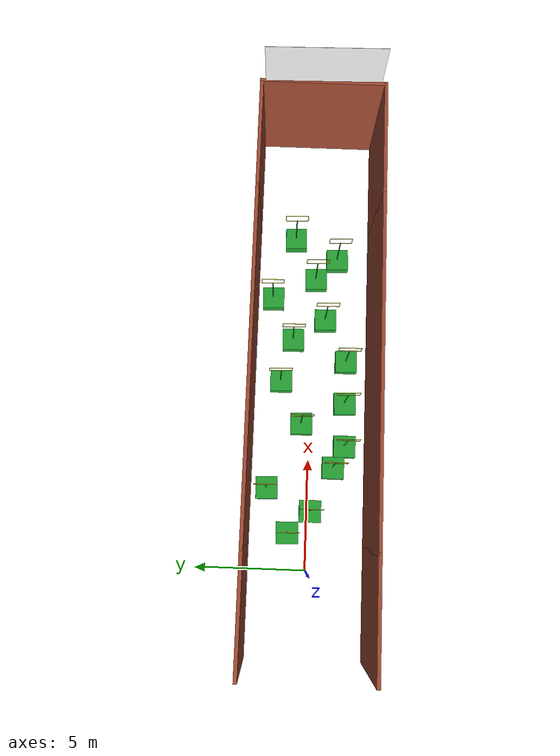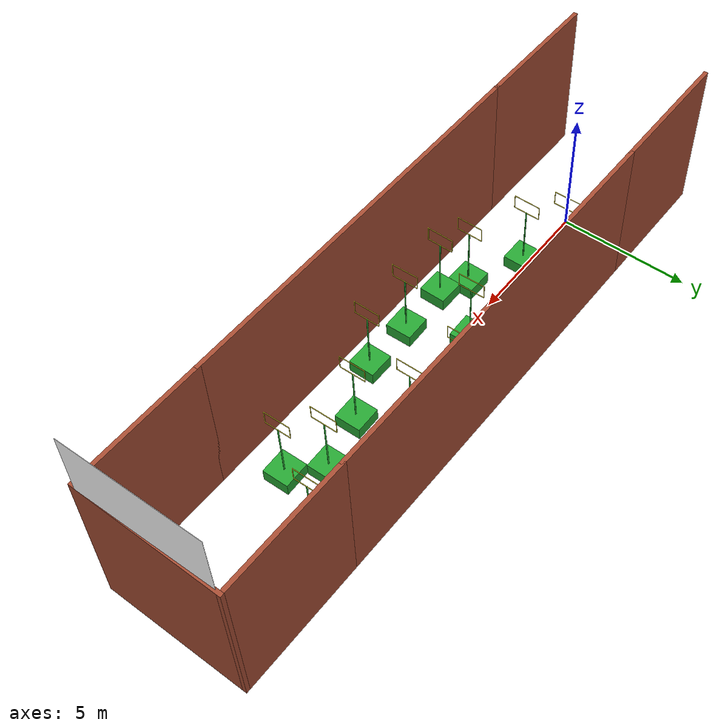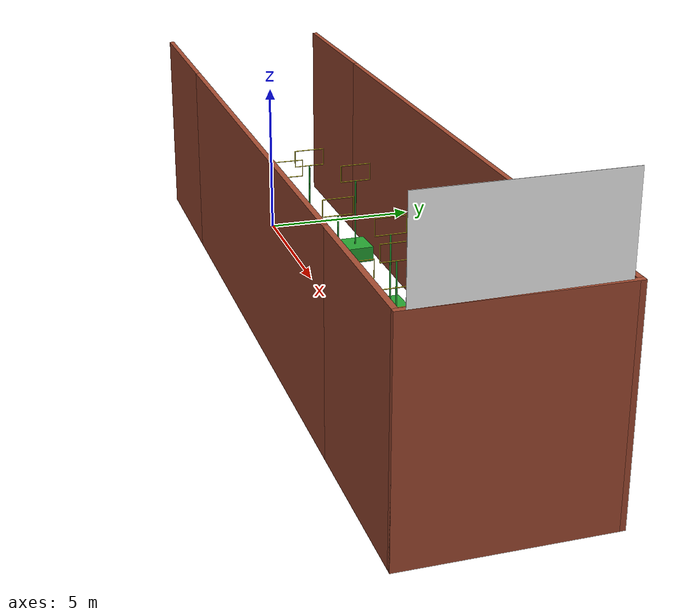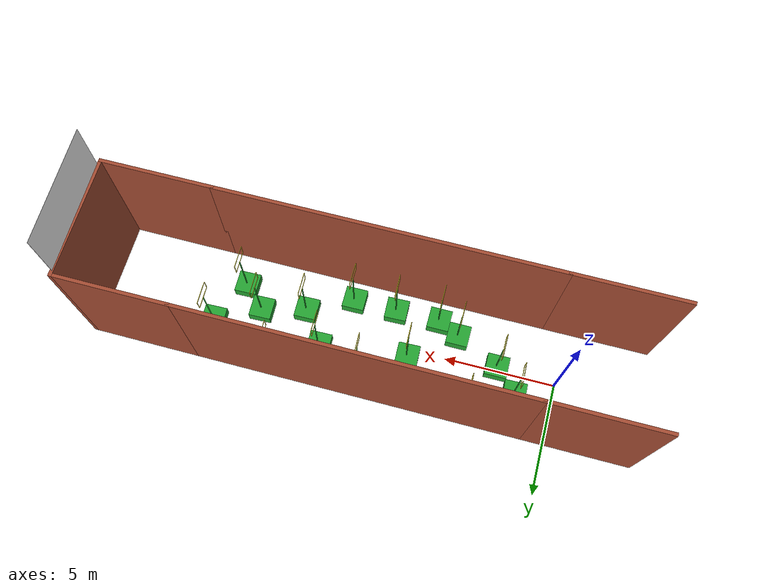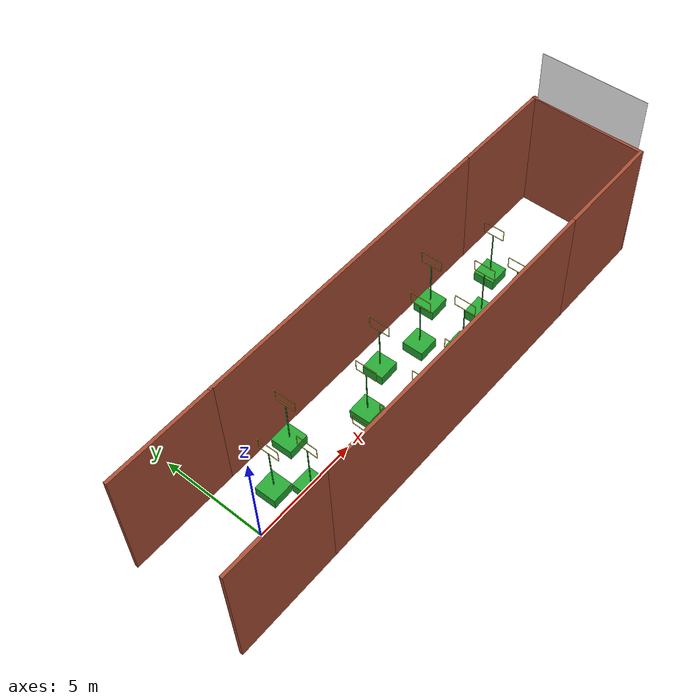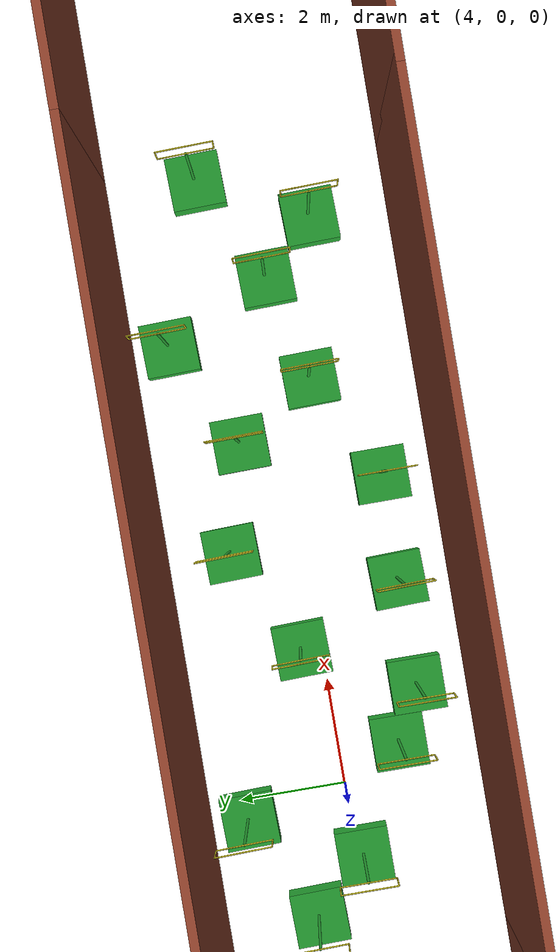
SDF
<sdf version="1.6">
 <world name="vrc_task_1">
  <scene><ambient>0.4 0.4 0.4 1</ambient><background>0.7 0.7 0.7 1</background><shadows>1</shadows></scene>
  <physics name="default_physics" default="0" type="ode">
   <ode>
    <solver>
     <type>quick</type>
     <iters>10</iters>
     <sor>1</sor>
     <use_dynamic_moi_rescaling>0</use_dynamic_moi_rescaling>
    </solver>
    <constraints>
     <cfm>0</cfm>
     <erp>0.2</erp>
     <contact_max_correcting_vel>100</contact_max_correcting_vel>
     <contact_surface_layer>0.001</contact_surface_layer>
    </constraints>
   </ode>
   <max_step_size>0.004</max_step_size>
   <real_time_factor>1</real_time_factor>
   <real_time_update_rate>250</real_time_update_rate>
  </physics>
  <light name="sun" type="directional">
   <pose>0 0 10 0 -0 0</pose>
   <diffuse>0.8 0.8 0.8 1</diffuse>
   <specular>0.2 0.2 0.2 1</specular>
   <attenuation>
    <range>1000</range>
    <constant>0.9</constant>
    <linear>0.01</linear>
    <quadratic>0.001</quadratic>
   </attenuation>
   <direction>-0.5 0.1 -0.9</direction>
  </light>
  <gravity>0 0 -9.8066</gravity>
  <magnetic_field>6e-06 2.3e-05 -4.2e-05</magnetic_field>
  <atmosphere type="adiabatic"/>
  <spherical_coordinates>
   <surface_model>EARTH_WGS84</surface_model>
   <latitude_deg>0</latitude_deg>
   <longitude_deg>0</longitude_deg>
   <elevation>0</elevation>
   <heading_deg>0</heading_deg>
  </spherical_coordinates>
  <model name="flipkart_hoop">
   <link name="link_0">
    <inertial>
     <mass>0.530306</mass>
     <inertia>
      <ixx>0.0566207</ixx>
      <ixy>0</ixy>
      <ixz>0</ixz>
      <iyy>0.0566207</iyy>
      <iyz>0</iyz>
      <izz>0.0883844</izz>
     </inertia>
    </inertial>
    <pose>0.141833 0.667401 -1.68595 0 -0 0</pose>
    <visual name="visual">
     <geometry><box><size>1 1 0.5</size></box></geometry>
     <material>
      <lighting>1</lighting>
      <script><uri>file://media/materials/scripts/gazebo.material</uri><name>Gazebo/Green</name></script>
      <shader type="pixel"/>
      <emissive>0 0 0 1</emissive>
     </material>
    </visual>
    <collision name="collision">
     <geometry><box><size>1 1 0.5</size></box></geometry>
     <surface>
      <friction>
       <ode><mu>1</mu><mu2>1</mu2><fdir1>0 0 0</fdir1><slip1>0</slip1><slip2>0</slip2></ode>
       <torsional>
        <coefficient>1</coefficient>
        <patch_radius>0</patch_radius>
        <surface_radius>0</surface_radius>
        <use_patch_radius>1</use_patch_radius>
        <ode><slip>0</slip></ode>
       </torsional>
      </friction>
      <bounce><restitution_coefficient>0</restitution_coefficient><threshold>1e+06</threshold></bounce>
      <contact>
       <collide_without_contact>0</collide_without_contact>
       <collide_without_contact_bitmask>1</collide_without_contact_bitmask>
       <collide_bitmask>1</collide_bitmask>
       <ode>
        <soft_cfm>0</soft_cfm>
        <soft_erp>0.2</soft_erp>
        <kp>1e+13</kp>
        <kd>1</kd>
        <max_vel>0.01</max_vel>
        <min_depth>0</min_depth>
       </ode>
       <bullet>
        <split_impulse>1</split_impulse>
        <split_impulse_penetration_threshold>-0.01</split_impulse_penetration_threshold>
        <soft_cfm>0</soft_cfm>
        <soft_erp>0.2</soft_erp>
        <kp>1e+13</kp>
        <kd>1</kd>
       </bullet>
      </contact>
     </surface>
    </collision>
   </link>
   <link name="link_1">
    <inertial>
     <mass>0.25</mass>
     <inertia>
      <ixx>0.130247</ixx>
      <ixy>0</ixy>
      <ixz>0</ixz>
      <iyy>0.130247</iyy>
      <iyz>0</iyz>
      <izz>7.813e-05</izz>
     </inertia>
    </inertial>
    <pose>0.122412 0.714194 -0.478486 0 -0 0</pose>
    <visual name="visual">
     <geometry><cylinder><radius>0.025</radius><length>2.5</length></cylinder></geometry>
     <material>
      <lighting>1</lighting>
      <script><uri>file://media/materials/scripts/gazebo.material</uri><name>Gazebo/Green</name></script>
      <shader type="pixel"/>
      <emissive>0 0 0 1</emissive>
     </material>
    </visual>
    <collision name="collision">
     <geometry><cylinder><radius>0.025</radius><length>2.5</length></cylinder></geometry>
     <surface>
      <friction>
       <ode><mu>1</mu><mu2>1</mu2><fdir1>0 0 0</fdir1><slip1>0</slip1><slip2>0</slip2></ode>
       <torsional>
        <coefficient>1</coefficient>
        <patch_radius>0</patch_radius>
        <surface_radius>0</surface_radius>
        <use_patch_radius>1</use_patch_radius>
        <ode><slip>0</slip></ode>
       </torsional>
      </friction>
      <bounce><restitution_coefficient>0</restitution_coefficient><threshold>1e+06</threshold></bounce>
      <contact>
       <collide_without_contact>0</collide_without_contact>
       <collide_without_contact_bitmask>1</collide_without_contact_bitmask>
       <collide_bitmask>1</collide_bitmask>
       <ode>
        <soft_cfm>0</soft_cfm>
        <soft_erp>0.2</soft_erp>
        <kp>1e+13</kp>
        <kd>1</kd>
        <max_vel>0.01</max_vel>
        <min_depth>0</min_depth>
       </ode>
       <bullet>
        <split_impulse>1</split_impulse>
        <split_impulse_penetration_threshold>-0.01</split_impulse_penetration_threshold>
        <soft_cfm>0</soft_cfm>
        <soft_erp>0.2</soft_erp>
        <kp>1e+13</kp>
        <kd>1</kd>
       </bullet>
      </contact>
     </surface>
    </collision>
   </link>
   <link name="link_2">
    <inertial>
     <mass>0.05</mass>
     <inertia>
      <ixx>0.00416862</ixx>
      <ixy>0</ixy>
      <ixz>0</ixz>
      <iyy>0.00416862</iyy>
      <iyz>0</iyz>
      <izz>3.91e-06</izz>
     </inertia>
    </inertial>
    <pose>0.122412 0.714194 1.32141 1.57 -0 1.57</pose>
    <visual name="visual">
     <geometry><cylinder><radius>0.0125</radius><length>1</length></cylinder></geometry>
     <material>
      <lighting>1</lighting>
      <script><uri>file://media/materials/scripts/gazebo.material</uri><name>Gazebo/Yellow</name></script>
      <shader type="pixel"/>
      <emissive>0 0 0 1</emissive>
     </material>
    </visual>
    <collision name="collision">
     <geometry><cylinder><radius>0.0125</radius><length>1</length></cylinder></geometry>
     <surface>
      <friction>
       <ode><mu>1</mu><mu2>1</mu2><fdir1>0 0 0</fdir1><slip1>0</slip1><slip2>0</slip2></ode>
       <torsional>
        <coefficient>1</coefficient>
        <patch_radius>0</patch_radius>
        <surface_radius>0</surface_radius>
        <use_patch_radius>1</use_patch_radius>
        <ode><slip>0</slip></ode>
       </torsional>
      </friction>
      <bounce><restitution_coefficient>0</restitution_coefficient><threshold>1e+06</threshold></bounce>
      <contact>
       <collide_without_contact>0</collide_without_contact>
       <collide_without_contact_bitmask>1</collide_without_contact_bitmask>
       <collide_bitmask>1</collide_bitmask>
       <ode>
        <soft_cfm>0</soft_cfm>
        <soft_erp>0.2</soft_erp>
        <kp>1e+13</kp>
        <kd>1</kd>
        <max_vel>0.01</max_vel>
        <min_depth>0</min_depth>
       </ode>
       <bullet>
        <split_impulse>1</split_impulse>
        <split_impulse_penetration_threshold>-0.01</split_impulse_penetration_threshold>
        <soft_cfm>0</soft_cfm>
        <soft_erp>0.2</soft_erp>
        <kp>1e+13</kp>
        <kd>1</kd>
       </bullet>
      </contact>
     </surface>
    </collision>
   </link>
   <link name="link_2_clone_0">
    <inertial>
     <mass>0.05</mass>
     <inertia>
      <ixx>0.00416862</ixx>
      <ixy>0</ixy>
      <ixz>0</ixz>
      <iyy>0.00416862</iyy>
      <iyz>0</iyz>
      <izz>3.91e-06</izz>
     </inertia>
    </inertial>
    <pose>0.122412 0.714194 0.771414 1.57 -0 1.57</pose>
    <visual name="visual">
     <geometry><cylinder><radius>0.0125</radius><length>1</length></cylinder></geometry>
     <material>
      <lighting>1</lighting>
      <script><uri>file://media/materials/scripts/gazebo.material</uri><name>Gazebo/Yellow</name></script>
      <shader type="pixel"/>
      <emissive>0 0 0 1</emissive>
     </material>
    </visual>
    <collision name="collision">
     <geometry><cylinder><radius>0.0125</radius><length>1</length></cylinder></geometry>
     <surface>
      <friction>
       <ode><mu>1</mu><mu2>1</mu2><fdir1>0 0 0</fdir1><slip1>0</slip1><slip2>0</slip2></ode>
       <torsional>
        <coefficient>1</coefficient>
        <patch_radius>0</patch_radius>
        <surface_radius>0</surface_radius>
        <use_patch_radius>1</use_patch_radius>
        <ode><slip>0</slip></ode>
       </torsional>
      </friction>
      <bounce><restitution_coefficient>0</restitution_coefficient><threshold>1e+06</threshold></bounce>
      <contact>
       <collide_without_contact>0</collide_without_contact>
       <collide_without_contact_bitmask>1</collide_without_contact_bitmask>
       <collide_bitmask>1</collide_bitmask>
       <ode>
        <soft_cfm>0</soft_cfm>
        <soft_erp>0.2</soft_erp>
        <kp>1e+13</kp>
        <kd>1</kd>
        <max_vel>0.01</max_vel>
        <min_depth>0</min_depth>
       </ode>
       <bullet>
        <split_impulse>1</split_impulse>
        <split_impulse_penetration_threshold>-0.01</split_impulse_penetration_threshold>
        <soft_cfm>0</soft_cfm>
        <soft_erp>0.2</soft_erp>
        <kp>1e+13</kp>
        <kd>1</kd>
       </bullet>
      </contact>
     </surface>
    </collision>
   </link>
   <link name="link_3_clone_clone">
    <inertial>
     <mass>0.025</mass>
     <inertia>
      <ixx>0.00063118</ixx>
      <ixy>0</ixy>
      <ixz>0</ixz>
      <iyy>0.00063118</iyy>
      <iyz>0</iyz>
      <izz>1.95e-06</izz>
     </inertia>
    </inertial>
    <pose>-0.377588 0.714194 1.04641 8e-06 -0 8e-06</pose>
    <visual name="visual">
     <geometry><cylinder><radius>0.0125</radius><length>0.55</length></cylinder></geometry>
     <material>
      <lighting>1</lighting>
      <script><uri>file://media/materials/scripts/gazebo.material</uri><name>Gazebo/Yellow</name></script>
      <shader type="pixel"/>
      <emissive>0 0 0 1</emissive>
     </material>
    </visual>
    <collision name="collision">
     <geometry><cylinder><radius>0.0125</radius><length>0.55</length></cylinder></geometry>
     <surface>
      <friction>
       <ode><mu>1</mu><mu2>1</mu2><fdir1>0 0 0</fdir1><slip1>0</slip1><slip2>0</slip2></ode>
       <torsional>
        <coefficient>1</coefficient>
        <patch_radius>0</patch_radius>
        <surface_radius>0</surface_radius>
        <use_patch_radius>1</use_patch_radius>
        <ode><slip>0</slip></ode>
       </torsional>
      </friction>
      <bounce><restitution_coefficient>0</restitution_coefficient><threshold>1e+06</threshold></bounce>
      <contact>
       <collide_without_contact>0</collide_without_contact>
       <collide_without_contact_bitmask>1</collide_without_contact_bitmask>
       <collide_bitmask>1</collide_bitmask>
       <ode>
        <soft_cfm>0</soft_cfm>
        <soft_erp>0.2</soft_erp>
        <kp>1e+13</kp>
        <kd>1</kd>
        <max_vel>0.01</max_vel>
        <min_depth>0</min_depth>
       </ode>
       <bullet>
        <split_impulse>1</split_impulse>
        <split_impulse_penetration_threshold>-0.01</split_impulse_penetration_threshold>
        <soft_cfm>0</soft_cfm>
        <soft_erp>0.2</soft_erp>
        <kp>1e+13</kp>
        <kd>1</kd>
       </bullet>
      </contact>
     </surface>
    </collision>
   </link>
   <link name="link_3_clone_clone_clone">
    <inertial>
     <mass>0.025</mass>
     <inertia>
      <ixx>0.00063118</ixx>
      <ixy>0</ixy>
      <ixz>0</ixz>
      <iyy>0.00063118</iyy>
      <iyz>0</iyz>
      <izz>1.95e-06</izz>
     </inertia>
    </inertial>
    <pose>0.622412 0.714194 1.04641 5.7e-05 -0 5.7e-05</pose>
    <visual name="visual">
     <geometry><cylinder><radius>0.0125</radius><length>0.55</length></cylinder></geometry>
     <material>
      <lighting>1</lighting>
      <script><uri>file://media/materials/scripts/gazebo.material</uri><name>Gazebo/Yellow</name></script>
      <shader type="pixel"/>
      <emissive>0 0 0 1</emissive>
     </material>
    </visual>
    <collision name="collision">
     <geometry><cylinder><radius>0.0125</radius><length>0.55</length></cylinder></geometry>
     <surface>
      <friction>
       <ode><mu>1</mu><mu2>1</mu2><fdir1>0 0 0</fdir1><slip1>0</slip1><slip2>0</slip2></ode>
       <torsional>
        <coefficient>1</coefficient>
        <patch_radius>0</patch_radius>
        <surface_radius>0</surface_radius>
        <use_patch_radius>1</use_patch_radius>
        <ode><slip>0</slip></ode>
       </torsional>
      </friction>
      <bounce><restitution_coefficient>0</restitution_coefficient><threshold>1e+06</threshold></bounce>
      <contact>
       <collide_without_contact>0</collide_without_contact>
       <collide_without_contact_bitmask>1</collide_without_contact_bitmask>
       <collide_bitmask>1</collide_bitmask>
       <ode>
        <soft_cfm>0</soft_cfm>
        <soft_erp>0.2</soft_erp>
        <kp>1e+13</kp>
        <kd>1</kd>
        <max_vel>0.01</max_vel>
        <min_depth>0</min_depth>
       </ode>
       <bullet>
        <split_impulse>1</split_impulse>
        <split_impulse_penetration_threshold>-0.01</split_impulse_penetration_threshold>
        <soft_cfm>0</soft_cfm>
        <soft_erp>0.2</soft_erp>
        <kp>1e+13</kp>
        <kd>1</kd>
       </bullet>
      </contact>
     </surface>
    </collision>
   </link>
   <joint name="link_0_JOINT_0" type="fixed">
    <parent>link_0</parent>
    <child>link_1</child>
    <physics>
     <ode><limit><cfm>0</cfm><erp>0.2</erp></limit><suspension><cfm>0</cfm><erp>0.2</erp></suspension></ode>
    </physics>
   </joint>
   <joint name="link_1_JOINT_0" type="fixed">
    <parent>link_1</parent>
    <child>link_2_clone_0</child>
    <physics>
     <ode><limit><cfm>0</cfm><erp>0.2</erp></limit><suspension><cfm>0</cfm><erp>0.2</erp></suspension></ode>
    </physics>
   </joint>
   <joint name="link_2_JOINT_2" type="fixed">
    <parent>link_2</parent>
    <child>link_3_clone_clone_clone</child>
    <physics>
     <ode><limit><cfm>0</cfm><erp>0.2</erp></limit><suspension><cfm>0</cfm><erp>0.2</erp></suspension></ode>
    </physics>
   </joint>
   <joint name="link_2_clone_0_JOINT_4" type="fixed">
    <parent>link_2_clone_0</parent>
    <child>link_3_clone_clone</child>
    <physics>
     <ode><limit><cfm>0</cfm><erp>0.2</erp></limit><suspension><cfm>0</cfm><erp>0.2</erp></suspension></ode>
    </physics>
   </joint>
   <joint name="link_3_clone_clone_JOINT_1" type="fixed">
    <parent>link_3_clone_clone</parent>
    <child>link_2</child>
    <physics>
     <ode><limit><cfm>0</cfm><erp>0.2</erp></limit><suspension><cfm>0</cfm><erp>0.2</erp></suspension></ode>
    </physics>
   </joint>
   <joint name="link_3_clone_clone_clone_JOINT_3" type="fixed">
    <parent>link_3_clone_clone_clone</parent>
    <child>link_2_clone_0</child>
    <physics>
     <ode><limit><cfm>0</cfm><erp>0.2</erp></limit><suspension><cfm>0</cfm><erp>0.2</erp></suspension></ode>
    </physics>
   </joint>
   <static>0</static>
   <pose>3.00055 2.00101 1.93595 0 -1e-05 -1.5425</pose>
  </model>
  <model name="flipkart_hoop_clone">
   <link name="link_0">
    <inertial>
     <mass>0.530306</mass>
     <inertia>
      <ixx>0.0566207</ixx>
      <ixy>0</ixy>
      <ixz>0</ixz>
      <iyy>0.0566207</iyy>
      <iyz>0</iyz>
      <izz>0.0883844</izz>
     </inertia>
    </inertial>
    <pose>0.141833 0.667401 -1.68595 0 -0 0</pose>
    <visual name="visual">
     <geometry><box><size>1 1 0.5</size></box></geometry>
     <material>
      <lighting>1</lighting>
      <script><uri>file://media/materials/scripts/gazebo.material</uri><name>Gazebo/Green</name></script>
      <shader type="pixel"/>
      <emissive>0 0 0 1</emissive>
     </material>
    </visual>
    <collision name="collision">
     <geometry><box><size>1 1 0.5</size></box></geometry>
     <surface>
      <friction>
       <ode><mu>1</mu><mu2>1</mu2><fdir1>0 0 0</fdir1><slip1>0</slip1><slip2>0</slip2></ode>
       <torsional>
        <coefficient>1</coefficient>
        <patch_radius>0</patch_radius>
        <surface_radius>0</surface_radius>
        <use_patch_radius>1</use_patch_radius>
        <ode><slip>0</slip></ode>
       </torsional>
      </friction>
      <bounce><restitution_coefficient>0</restitution_coefficient><threshold>1e+06</threshold></bounce>
      <contact>
       <collide_without_contact>0</collide_without_contact>
       <collide_without_contact_bitmask>1</collide_without_contact_bitmask>
       <collide_bitmask>1</collide_bitmask>
       <ode>
        <soft_cfm>0</soft_cfm>
        <soft_erp>0.2</soft_erp>
        <kp>1e+13</kp>
        <kd>1</kd>
        <max_vel>0.01</max_vel>
        <min_depth>0</min_depth>
       </ode>
       <bullet>
        <split_impulse>1</split_impulse>
        <split_impulse_penetration_threshold>-0.01</split_impulse_penetration_threshold>
        <soft_cfm>0</soft_cfm>
        <soft_erp>0.2</soft_erp>
        <kp>1e+13</kp>
        <kd>1</kd>
       </bullet>
      </contact>
     </surface>
    </collision>
   </link>
   <link name="link_1">
    <inertial>
     <mass>0.25</mass>
     <inertia>
      <ixx>0.130247</ixx>
      <ixy>0</ixy>
      <ixz>0</ixz>
      <iyy>0.130247</iyy>
      <iyz>0</iyz>
      <izz>7.813e-05</izz>
     </inertia>
    </inertial>
    <pose>0.122412 0.714194 -0.478486 0 -0 0</pose>
    <visual name="visual">
     <geometry><cylinder><radius>0.025</radius><length>2.5</length></cylinder></geometry>
     <material>
      <lighting>1</lighting>
      <script><uri>file://media/materials/scripts/gazebo.material</uri><name>Gazebo/Green</name></script>
      <shader type="pixel"/>
      <emissive>0 0 0 1</emissive>
     </material>
    </visual>
    <collision name="collision">
     <geometry><cylinder><radius>0.025</radius><length>2.5</length></cylinder></geometry>
     <surface>
      <friction>
       <ode><mu>1</mu><mu2>1</mu2><fdir1>0 0 0</fdir1><slip1>0</slip1><slip2>0</slip2></ode>
       <torsional>
        <coefficient>1</coefficient>
        <patch_radius>0</patch_radius>
        <surface_radius>0</surface_radius>
        <use_patch_radius>1</use_patch_radius>
        <ode><slip>0</slip></ode>
       </torsional>
      </friction>
      <bounce><restitution_coefficient>0</restitution_coefficient><threshold>1e+06</threshold></bounce>
      <contact>
       <collide_without_contact>0</collide_without_contact>
       <collide_without_contact_bitmask>1</collide_without_contact_bitmask>
       <collide_bitmask>1</collide_bitmask>
       <ode>
        <soft_cfm>0</soft_cfm>
        <soft_erp>0.2</soft_erp>
        <kp>1e+13</kp>
        <kd>1</kd>
        <max_vel>0.01</max_vel>
        <min_depth>0</min_depth>
       </ode>
       <bullet>
        <split_impulse>1</split_impulse>
        <split_impulse_penetration_threshold>-0.01</split_impulse_penetration_threshold>
        <soft_cfm>0</soft_cfm>
        <soft_erp>0.2</soft_erp>
        <kp>1e+13</kp>
        <kd>1</kd>
       </bullet>
      </contact>
     </surface>
    </collision>
   </link>
   <link name="link_2">
    <inertial>
     <mass>0.05</mass>
     <inertia>
      <ixx>0.00416862</ixx>
      <ixy>0</ixy>
      <ixz>0</ixz>
      <iyy>0.00416862</iyy>
      <iyz>0</iyz>
      <izz>3.91e-06</izz>
     </inertia>
    </inertial>
    <pose>0.122412 0.714194 1.32141 1.57 -0 1.57</pose>
    <visual name="visual">
     <geometry><cylinder><radius>0.0125</radius><length>1</length></cylinder></geometry>
     <material>
      <lighting>1</lighting>
      <script><uri>file://media/materials/scripts/gazebo.material</uri><name>Gazebo/Yellow</name></script>
      <shader type="pixel"/>
      <emissive>0 0 0 1</emissive>
     </material>
    </visual>
    <collision name="collision">
     <geometry><cylinder><radius>0.0125</radius><length>1</length></cylinder></geometry>
     <surface>
      <friction>
       <ode><mu>1</mu><mu2>1</mu2><fdir1>0 0 0</fdir1><slip1>0</slip1><slip2>0</slip2></ode>
       <torsional>
        <coefficient>1</coefficient>
        <patch_radius>0</patch_radius>
        <surface_radius>0</surface_radius>
        <use_patch_radius>1</use_patch_radius>
        <ode><slip>0</slip></ode>
       </torsional>
      </friction>
      <bounce><restitution_coefficient>0</restitution_coefficient><threshold>1e+06</threshold></bounce>
      <contact>
       <collide_without_contact>0</collide_without_contact>
       <collide_without_contact_bitmask>1</collide_without_contact_bitmask>
       <collide_bitmask>1</collide_bitmask>
       <ode>
        <soft_cfm>0</soft_cfm>
        <soft_erp>0.2</soft_erp>
        <kp>1e+13</kp>
        <kd>1</kd>
        <max_vel>0.01</max_vel>
        <min_depth>0</min_depth>
       </ode>
       <bullet>
        <split_impulse>1</split_impulse>
        <split_impulse_penetration_threshold>-0.01</split_impulse_penetration_threshold>
        <soft_cfm>0</soft_cfm>
        <soft_erp>0.2</soft_erp>
        <kp>1e+13</kp>
        <kd>1</kd>
       </bullet>
      </contact>
     </surface>
    </collision>
   </link>
   <link name="link_2_clone_0">
    <inertial>
     <mass>0.05</mass>
     <inertia>
      <ixx>0.00416862</ixx>
      <ixy>0</ixy>
      <ixz>0</ixz>
      <iyy>0.00416862</iyy>
      <iyz>0</iyz>
      <izz>3.91e-06</izz>
     </inertia>
    </inertial>
    <pose>0.122412 0.714194 0.771414 1.57 -0 1.57</pose>
    <visual name="visual">
     <geometry><cylinder><radius>0.0125</radius><length>1</length></cylinder></geometry>
     <material>
      <lighting>1</lighting>
      <script><uri>file://media/materials/scripts/gazebo.material</uri><name>Gazebo/Yellow</name></script>
      <shader type="pixel"/>
      <emissive>0 0 0 1</emissive>
     </material>
    </visual>
    <collision name="collision">
     <geometry><cylinder><radius>0.0125</radius><length>1</length></cylinder></geometry>
     <surface>
      <friction>
       <ode><mu>1</mu><mu2>1</mu2><fdir1>0 0 0</fdir1><slip1>0</slip1><slip2>0</slip2></ode>
       <torsional>
        <coefficient>1</coefficient>
        <patch_radius>0</patch_radius>
        <surface_radius>0</surface_radius>
        <use_patch_radius>1</use_patch_radius>
        <ode><slip>0</slip></ode>
       </torsional>
      </friction>
      <bounce><restitution_coefficient>0</restitution_coefficient><threshold>1e+06</threshold></bounce>
      <contact>
       <collide_without_contact>0</collide_without_contact>
       <collide_without_contact_bitmask>1</collide_without_contact_bitmask>
       <collide_bitmask>1</collide_bitmask>
       <ode>
        <soft_cfm>0</soft_cfm>
        <soft_erp>0.2</soft_erp>
        <kp>1e+13</kp>
        <kd>1</kd>
        <max_vel>0.01</max_vel>
        <min_depth>0</min_depth>
       </ode>
       <bullet>
        <split_impulse>1</split_impulse>
        <split_impulse_penetration_threshold>-0.01</split_impulse_penetration_threshold>
        <soft_cfm>0</soft_cfm>
        <soft_erp>0.2</soft_erp>
        <kp>1e+13</kp>
        <kd>1</kd>
       </bullet>
      </contact>
     </surface>
    </collision>
   </link>
   <link name="link_3_clone_clone">
    <inertial>
     <mass>0.025</mass>
     <inertia>
      <ixx>0.00063118</ixx>
      <ixy>0</ixy>
      <ixz>0</ixz>
      <iyy>0.00063118</iyy>
      <iyz>0</iyz>
      <izz>1.95e-06</izz>
     </inertia>
    </inertial>
    <pose>-0.377588 0.714194 1.04641 8e-06 -0 8e-06</pose>
    <visual name="visual">
     <geometry><cylinder><radius>0.0125</radius><length>0.55</length></cylinder></geometry>
     <material>
      <lighting>1</lighting>
      <script><uri>file://media/materials/scripts/gazebo.material</uri><name>Gazebo/Yellow</name></script>
      <shader type="pixel"/>
      <emissive>0 0 0 1</emissive>
     </material>
    </visual>
    <collision name="collision">
     <geometry><cylinder><radius>0.0125</radius><length>0.55</length></cylinder></geometry>
     <surface>
      <friction>
       <ode><mu>1</mu><mu2>1</mu2><fdir1>0 0 0</fdir1><slip1>0</slip1><slip2>0</slip2></ode>
       <torsional>
        <coefficient>1</coefficient>
        <patch_radius>0</patch_radius>
        <surface_radius>0</surface_radius>
        <use_patch_radius>1</use_patch_radius>
        <ode><slip>0</slip></ode>
       </torsional>
      </friction>
      <bounce><restitution_coefficient>0</restitution_coefficient><threshold>1e+06</threshold></bounce>
      <contact>
       <collide_without_contact>0</collide_without_contact>
       <collide_without_contact_bitmask>1</collide_without_contact_bitmask>
       <collide_bitmask>1</collide_bitmask>
       <ode>
        <soft_cfm>0</soft_cfm>
        <soft_erp>0.2</soft_erp>
        <kp>1e+13</kp>
        <kd>1</kd>
        <max_vel>0.01</max_vel>
        <min_depth>0</min_depth>
       </ode>
       <bullet>
        <split_impulse>1</split_impulse>
        <split_impulse_penetration_threshold>-0.01</split_impulse_penetration_threshold>
        <soft_cfm>0</soft_cfm>
        <soft_erp>0.2</soft_erp>
        <kp>1e+13</kp>
        <kd>1</kd>
       </bullet>
      </contact>
     </surface>
    </collision>
   </link>
   <link name="link_3_clone_clone_clone">
    <inertial>
     <mass>0.025</mass>
     <inertia>
      <ixx>0.00063118</ixx>
      <ixy>0</ixy>
      <ixz>0</ixz>
      <iyy>0.00063118</iyy>
      <iyz>0</iyz>
      <izz>1.95e-06</izz>
     </inertia>
    </inertial>
    <pose>0.622412 0.714194 1.04641 5.7e-05 -0 5.7e-05</pose>
    <visual name="visual">
     <geometry><cylinder><radius>0.0125</radius><length>0.55</length></cylinder></geometry>
     <material>
      <lighting>1</lighting>
      <script><uri>file://media/materials/scripts/gazebo.material</uri><name>Gazebo/Yellow</name></script>
      <shader type="pixel"/>
      <emissive>0 0 0 1</emissive>
     </material>
    </visual>
    <collision name="collision">
     <geometry><cylinder><radius>0.0125</radius><length>0.55</length></cylinder></geometry>
     <surface>
      <friction>
       <ode><mu>1</mu><mu2>1</mu2><fdir1>0 0 0</fdir1><slip1>0</slip1><slip2>0</slip2></ode>
       <torsional>
        <coefficient>1</coefficient>
        <patch_radius>0</patch_radius>
        <surface_radius>0</surface_radius>
        <use_patch_radius>1</use_patch_radius>
        <ode><slip>0</slip></ode>
       </torsional>
      </friction>
      <bounce><restitution_coefficient>0</restitution_coefficient><threshold>1e+06</threshold></bounce>
      <contact>
       <collide_without_contact>0</collide_without_contact>
       <collide_without_contact_bitmask>1</collide_without_contact_bitmask>
       <collide_bitmask>1</collide_bitmask>
       <ode>
        <soft_cfm>0</soft_cfm>
        <soft_erp>0.2</soft_erp>
        <kp>1e+13</kp>
        <kd>1</kd>
        <max_vel>0.01</max_vel>
        <min_depth>0</min_depth>
       </ode>
       <bullet>
        <split_impulse>1</split_impulse>
        <split_impulse_penetration_threshold>-0.01</split_impulse_penetration_threshold>
        <soft_cfm>0</soft_cfm>
        <soft_erp>0.2</soft_erp>
        <kp>1e+13</kp>
        <kd>1</kd>
       </bullet>
      </contact>
     </surface>
    </collision>
   </link>
   <joint name="link_0_JOINT_0" type="fixed">
    <parent>link_0</parent>
    <child>link_1</child>
    <physics>
     <ode><limit><cfm>0</cfm><erp>0.2</erp></limit><suspension><cfm>0</cfm><erp>0.2</erp></suspension></ode>
    </physics>
   </joint>
   <joint name="link_1_JOINT_0" type="fixed">
    <parent>link_1</parent>
    <child>link_2_clone_0</child>
    <physics>
     <ode><limit><cfm>0</cfm><erp>0.2</erp></limit><suspension><cfm>0</cfm><erp>0.2</erp></suspension></ode>
    </physics>
   </joint>
   <joint name="link_2_JOINT_2" type="fixed">
    <parent>link_2</parent>
    <child>link_3_clone_clone_clone</child>
    <physics>
     <ode><limit><cfm>0</cfm><erp>0.2</erp></limit><suspension><cfm>0</cfm><erp>0.2</erp></suspension></ode>
    </physics>
   </joint>
   <joint name="link_2_clone_0_JOINT_4" type="fixed">
    <parent>link_2_clone_0</parent>
    <child>link_3_clone_clone</child>
    <physics>
     <ode><limit><cfm>0</cfm><erp>0.2</erp></limit><suspension><cfm>0</cfm><erp>0.2</erp></suspension></ode>
    </physics>
   </joint>
   <joint name="link_3_clone_clone_JOINT_1" type="fixed">
    <parent>link_3_clone_clone</parent>
    <child>link_2</child>
    <physics>
     <ode><limit><cfm>0</cfm><erp>0.2</erp></limit><suspension><cfm>0</cfm><erp>0.2</erp></suspension></ode>
    </physics>
   </joint>
   <joint name="link_3_clone_clone_clone_JOINT_3" type="fixed">
    <parent>link_3_clone_clone_clone</parent>
    <child>link_2_clone_0</child>
    <physics>
     <ode><limit><cfm>0</cfm><erp>0.2</erp></limit><suspension><cfm>0</cfm><erp>0.2</erp></suspension></ode>
    </physics>
   </joint>
   <static>0</static>
   <pose>4.00354 -0.99581 1.9359 1e-06 -6.8e-05 -1.57311</pose>
  </model>
  <model name="flipkart_hoop_clone_0">
   <link name="link_0">
    <inertial>
     <mass>0.530306</mass>
     <inertia>
      <ixx>0.0566207</ixx>
      <ixy>0</ixy>
      <ixz>0</ixz>
      <iyy>0.0566207</iyy>
      <iyz>0</iyz>
      <izz>0.0883844</izz>
     </inertia>
    </inertial>
    <pose>0.141833 0.667401 -1.68595 0 -0 0</pose>
    <visual name="visual">
     <geometry><box><size>1 1 0.5</size></box></geometry>
     <material>
      <lighting>1</lighting>
      <script><uri>file://media/materials/scripts/gazebo.material</uri><name>Gazebo/Green</name></script>
      <shader type="pixel"/>
      <emissive>0 0 0 1</emissive>
     </material>
    </visual>
    <collision name="collision">
     <geometry><box><size>1 1 0.5</size></box></geometry>
     <surface>
      <friction>
       <ode><mu>1</mu><mu2>1</mu2><fdir1>0 0 0</fdir1><slip1>0</slip1><slip2>0</slip2></ode>
       <torsional>
        <coefficient>1</coefficient>
        <patch_radius>0</patch_radius>
        <surface_radius>0</surface_radius>
        <use_patch_radius>1</use_patch_radius>
        <ode><slip>0</slip></ode>
       </torsional>
      </friction>
      <bounce><restitution_coefficient>0</restitution_coefficient><threshold>1e+06</threshold></bounce>
      <contact>
       <collide_without_contact>0</collide_without_contact>
       <collide_without_contact_bitmask>1</collide_without_contact_bitmask>
       <collide_bitmask>1</collide_bitmask>
       <ode>
        <soft_cfm>0</soft_cfm>
        <soft_erp>0.2</soft_erp>
        <kp>1e+13</kp>
        <kd>1</kd>
        <max_vel>0.01</max_vel>
        <min_depth>0</min_depth>
       </ode>
       <bullet>
        <split_impulse>1</split_impulse>
        <split_impulse_penetration_threshold>-0.01</split_impulse_penetration_threshold>
        <soft_cfm>0</soft_cfm>
        <soft_erp>0.2</soft_erp>
        <kp>1e+13</kp>
        <kd>1</kd>
       </bullet>
      </contact>
     </surface>
    </collision>
   </link>
   <link name="link_1">
    <inertial>
     <mass>0.25</mass>
     <inertia>
      <ixx>0.130247</ixx>
      <ixy>0</ixy>
      <ixz>0</ixz>
      <iyy>0.130247</iyy>
      <iyz>0</iyz>
      <izz>7.813e-05</izz>
     </inertia>
    </inertial>
    <pose>0.122412 0.714194 -0.478486 0 -0 0</pose>
    <visual name="visual">
     <geometry><cylinder><radius>0.025</radius><length>2.5</length></cylinder></geometry>
     <material>
      <lighting>1</lighting>
      <script><uri>file://media/materials/scripts/gazebo.material</uri><name>Gazebo/Green</name></script>
      <shader type="pixel"/>
      <emissive>0 0 0 1</emissive>
     </material>
    </visual>
    <collision name="collision">
     <geometry><cylinder><radius>0.025</radius><length>2.5</length></cylinder></geometry>
     <surface>
      <friction>
       <ode><mu>1</mu><mu2>1</mu2><fdir1>0 0 0</fdir1><slip1>0</slip1><slip2>0</slip2></ode>
       <torsional>
        <coefficient>1</coefficient>
        <patch_radius>0</patch_radius>
        <surface_radius>0</surface_radius>
        <use_patch_radius>1</use_patch_radius>
        <ode><slip>0</slip></ode>
       </torsional>
      </friction>
      <bounce><restitution_coefficient>0</restitution_coefficient><threshold>1e+06</threshold></bounce>
      <contact>
       <collide_without_contact>0</collide_without_contact>
       <collide_without_contact_bitmask>1</collide_without_contact_bitmask>
       <collide_bitmask>1</collide_bitmask>
       <ode>
        <soft_cfm>0</soft_cfm>
        <soft_erp>0.2</soft_erp>
        <kp>1e+13</kp>
        <kd>1</kd>
        <max_vel>0.01</max_vel>
        <min_depth>0</min_depth>
       </ode>
       <bullet>
        <split_impulse>1</split_impulse>
        <split_impulse_penetration_threshold>-0.01</split_impulse_penetration_threshold>
        <soft_cfm>0</soft_cfm>
        <soft_erp>0.2</soft_erp>
        <kp>1e+13</kp>
        <kd>1</kd>
       </bullet>
      </contact>
     </surface>
    </collision>
   </link>
   <link name="link_2">
    <inertial>
     <mass>0.05</mass>
     <inertia>
      <ixx>0.00416862</ixx>
      <ixy>0</ixy>
      <ixz>0</ixz>
      <iyy>0.00416862</iyy>
      <iyz>0</iyz>
      <izz>3.91e-06</izz>
     </inertia>
    </inertial>
    <pose>0.122412 0.714194 1.32141 1.57 -0 1.57</pose>
    <visual name="visual">
     <geometry><cylinder><radius>0.0125</radius><length>1</length></cylinder></geometry>
     <material>
      <lighting>1</lighting>
      <script><uri>file://media/materials/scripts/gazebo.material</uri><name>Gazebo/Yellow</name></script>
      <shader type="pixel"/>
      <emissive>0 0 0 1</emissive>
     </material>
    </visual>
    <collision name="collision">
     <geometry><cylinder><radius>0.0125</radius><length>1</length></cylinder></geometry>
     <surface>
      <friction>
       <ode><mu>1</mu><mu2>1</mu2><fdir1>0 0 0</fdir1><slip1>0</slip1><slip2>0</slip2></ode>
       <torsional>
        <coefficient>1</coefficient>
        <patch_radius>0</patch_radius>
        <surface_radius>0</surface_radius>
        <use_patch_radius>1</use_patch_radius>
        <ode><slip>0</slip></ode>
       </torsional>
      </friction>
      <bounce><restitution_coefficient>0</restitution_coefficient><threshold>1e+06</threshold></bounce>
      <contact>
       <collide_without_contact>0</collide_without_contact>
       <collide_without_contact_bitmask>1</collide_without_contact_bitmask>
       <collide_bitmask>1</collide_bitmask>
       <ode>
        <soft_cfm>0</soft_cfm>
        <soft_erp>0.2</soft_erp>
        <kp>1e+13</kp>
        <kd>1</kd>
        <max_vel>0.01</max_vel>
        <min_depth>0</min_depth>
       </ode>
       <bullet>
        <split_impulse>1</split_impulse>
        <split_impulse_penetration_threshold>-0.01</split_impulse_penetration_threshold>
        <soft_cfm>0</soft_cfm>
        <soft_erp>0.2</soft_erp>
        <kp>1e+13</kp>
        <kd>1</kd>
       </bullet>
      </contact>
     </surface>
    </collision>
   </link>
   <link name="link_2_clone_0">
    <inertial>
     <mass>0.05</mass>
     <inertia>
      <ixx>0.00416862</ixx>
      <ixy>0</ixy>
      <ixz>0</ixz>
      <iyy>0.00416862</iyy>
      <iyz>0</iyz>
      <izz>3.91e-06</izz>
     </inertia>
    </inertial>
    <pose>0.122412 0.714194 0.771414 1.57 -0 1.57</pose>
    <visual name="visual">
     <geometry><cylinder><radius>0.0125</radius><length>1</length></cylinder></geometry>
     <material>
      <lighting>1</lighting>
      <script><uri>file://media/materials/scripts/gazebo.material</uri><name>Gazebo/Yellow</name></script>
      <shader type="pixel"/>
      <emissive>0 0 0 1</emissive>
     </material>
    </visual>
    <collision name="collision">
     <geometry><cylinder><radius>0.0125</radius><length>1</length></cylinder></geometry>
     <surface>
      <friction>
       <ode><mu>1</mu><mu2>1</mu2><fdir1>0 0 0</fdir1><slip1>0</slip1><slip2>0</slip2></ode>
       <torsional>
        <coefficient>1</coefficient>
        <patch_radius>0</patch_radius>
        <surface_radius>0</surface_radius>
        <use_patch_radius>1</use_patch_radius>
        <ode><slip>0</slip></ode>
       </torsional>
      </friction>
      <bounce><restitution_coefficient>0</restitution_coefficient><threshold>1e+06</threshold></bounce>
      <contact>
       <collide_without_contact>0</collide_without_contact>
       <collide_without_contact_bitmask>1</collide_without_contact_bitmask>
       <collide_bitmask>1</collide_bitmask>
       <ode>
        <soft_cfm>0</soft_cfm>
        <soft_erp>0.2</soft_erp>
        <kp>1e+13</kp>
        <kd>1</kd>
        <max_vel>0.01</max_vel>
        <min_depth>0</min_depth>
       </ode>
       <bullet>
        <split_impulse>1</split_impulse>
        <split_impulse_penetration_threshold>-0.01</split_impulse_penetration_threshold>
        <soft_cfm>0</soft_cfm>
        <soft_erp>0.2</soft_erp>
        <kp>1e+13</kp>
        <kd>1</kd>
       </bullet>
      </contact>
     </surface>
    </collision>
   </link>
   <link name="link_3_clone_clone">
    <inertial>
     <mass>0.025</mass>
     <inertia>
      <ixx>0.00063118</ixx>
      <ixy>0</ixy>
      <ixz>0</ixz>
      <iyy>0.00063118</iyy>
      <iyz>0</iyz>
      <izz>1.95e-06</izz>
     </inertia>
    </inertial>
    <pose>-0.377588 0.714194 1.04641 8e-06 -0 8e-06</pose>
    <visual name="visual">
     <geometry><cylinder><radius>0.0125</radius><length>0.55</length></cylinder></geometry>
     <material>
      <lighting>1</lighting>
      <script><uri>file://media/materials/scripts/gazebo.material</uri><name>Gazebo/Yellow</name></script>
      <shader type="pixel"/>
      <emissive>0 0 0 1</emissive>
     </material>
    </visual>
    <collision name="collision">
     <geometry><cylinder><radius>0.0125</radius><length>0.55</length></cylinder></geometry>
     <surface>
      <friction>
       <ode><mu>1</mu><mu2>1</mu2><fdir1>0 0 0</fdir1><slip1>0</slip1><slip2>0</slip2></ode>
       <torsional>
        <coefficient>1</coefficient>
        <patch_radius>0</patch_radius>
        <surface_radius>0</surface_radius>
        <use_patch_radius>1</use_patch_radius>
        <ode><slip>0</slip></ode>
       </torsional>
      </friction>
      <bounce><restitution_coefficient>0</restitution_coefficient><threshold>1e+06</threshold></bounce>
      <contact>
       <collide_without_contact>0</collide_without_contact>
       <collide_without_contact_bitmask>1</collide_without_contact_bitmask>
       <collide_bitmask>1</collide_bitmask>
       <ode>
        <soft_cfm>0</soft_cfm>
        <soft_erp>0.2</soft_erp>
        <kp>1e+13</kp>
        <kd>1</kd>
        <max_vel>0.01</max_vel>
        <min_depth>0</min_depth>
       </ode>
       <bullet>
        <split_impulse>1</split_impulse>
        <split_impulse_penetration_threshold>-0.01</split_impulse_penetration_threshold>
        <soft_cfm>0</soft_cfm>
        <soft_erp>0.2</soft_erp>
        <kp>1e+13</kp>
        <kd>1</kd>
       </bullet>
      </contact>
     </surface>
    </collision>
   </link>
   <link name="link_3_clone_clone_clone">
    <inertial>
     <mass>0.025</mass>
     <inertia>
      <ixx>0.00063118</ixx>
      <ixy>0</ixy>
      <ixz>0</ixz>
      <iyy>0.00063118</iyy>
      <iyz>0</iyz>
      <izz>1.95e-06</izz>
     </inertia>
    </inertial>
    <pose>0.622412 0.714194 1.04641 5.7e-05 -0 5.7e-05</pose>
    <visual name="visual">
     <geometry><cylinder><radius>0.0125</radius><length>0.55</length></cylinder></geometry>
     <material>
      <lighting>1</lighting>
      <script><uri>file://media/materials/scripts/gazebo.material</uri><name>Gazebo/Yellow</name></script>
      <shader type="pixel"/>
      <emissive>0 0 0 1</emissive>
     </material>
    </visual>
    <collision name="collision">
     <geometry><cylinder><radius>0.0125</radius><length>0.55</length></cylinder></geometry>
     <surface>
      <friction>
       <ode><mu>1</mu><mu2>1</mu2><fdir1>0 0 0</fdir1><slip1>0</slip1><slip2>0</slip2></ode>
       <torsional>
        <coefficient>1</coefficient>
        <patch_radius>0</patch_radius>
        <surface_radius>0</surface_radius>
        <use_patch_radius>1</use_patch_radius>
        <ode><slip>0</slip></ode>
       </torsional>
      </friction>
      <bounce><restitution_coefficient>0</restitution_coefficient><threshold>1e+06</threshold></bounce>
      <contact>
       <collide_without_contact>0</collide_without_contact>
       <collide_without_contact_bitmask>1</collide_without_contact_bitmask>
       <collide_bitmask>1</collide_bitmask>
       <ode>
        <soft_cfm>0</soft_cfm>
        <soft_erp>0.2</soft_erp>
        <kp>1e+13</kp>
        <kd>1</kd>
        <max_vel>0.01</max_vel>
        <min_depth>0</min_depth>
       </ode>
       <bullet>
        <split_impulse>1</split_impulse>
        <split_impulse_penetration_threshold>-0.01</split_impulse_penetration_threshold>
        <soft_cfm>0</soft_cfm>
        <soft_erp>0.2</soft_erp>
        <kp>1e+13</kp>
        <kd>1</kd>
       </bullet>
      </contact>
     </surface>
    </collision>
   </link>
   <joint name="link_0_JOINT_0" type="fixed">
    <parent>link_0</parent>
    <child>link_1</child>
    <physics>
     <ode><limit><cfm>0</cfm><erp>0.2</erp></limit><suspension><cfm>0</cfm><erp>0.2</erp></suspension></ode>
    </physics>
   </joint>
   <joint name="link_1_JOINT_0" type="fixed">
    <parent>link_1</parent>
    <child>link_2_clone_0</child>
    <physics>
     <ode><limit><cfm>0</cfm><erp>0.2</erp></limit><suspension><cfm>0</cfm><erp>0.2</erp></suspension></ode>
    </physics>
   </joint>
   <joint name="link_2_JOINT_2" type="fixed">
    <parent>link_2</parent>
    <child>link_3_clone_clone_clone</child>
    <physics>
     <ode><limit><cfm>0</cfm><erp>0.2</erp></limit><suspension><cfm>0</cfm><erp>0.2</erp></suspension></ode>
    </physics>
   </joint>
   <joint name="link_2_clone_0_JOINT_4" type="fixed">
    <parent>link_2_clone_0</parent>
    <child>link_3_clone_clone</child>
    <physics>
     <ode><limit><cfm>0</cfm><erp>0.2</erp></limit><suspension><cfm>0</cfm><erp>0.2</erp></suspension></ode>
    </physics>
   </joint>
   <joint name="link_3_clone_clone_JOINT_1" type="fixed">
    <parent>link_3_clone_clone</parent>
    <child>link_2</child>
    <physics>
     <ode><limit><cfm>0</cfm><erp>0.2</erp></limit><suspension><cfm>0</cfm><erp>0.2</erp></suspension></ode>
    </physics>
   </joint>
   <joint name="link_3_clone_clone_clone_JOINT_3" type="fixed">
    <parent>link_3_clone_clone_clone</parent>
    <child>link_2_clone_0</child>
    <physics>
     <ode><limit><cfm>0</cfm><erp>0.2</erp></limit><suspension><cfm>0</cfm><erp>0.2</erp></suspension></ode>
    </physics>
   </joint>
   <static>0</static>
   <pose>5.00293 -1.5006 1.93592 -3e-06 5.9e-05 -1.57371</pose>
  </model>
  <model name="flipkart_hoop_clone_1">
   <link name="link_0">
    <inertial>
     <mass>0.530306</mass>
     <inertia>
      <ixx>0.0566207</ixx>
      <ixy>0</ixy>
      <ixz>0</ixz>
      <iyy>0.0566207</iyy>
      <iyz>0</iyz>
      <izz>0.0883844</izz>
     </inertia>
    </inertial>
    <pose>0.141833 0.667401 -1.68595 0 -0 0</pose>
    <visual name="visual">
     <geometry><box><size>1 1 0.5</size></box></geometry>
     <material>
      <lighting>1</lighting>
      <script><uri>file://media/materials/scripts/gazebo.material</uri><name>Gazebo/Green</name></script>
      <shader type="pixel"/>
      <emissive>0 0 0 1</emissive>
     </material>
    </visual>
    <collision name="collision">
     <geometry><box><size>1 1 0.5</size></box></geometry>
     <surface>
      <friction>
       <ode><mu>1</mu><mu2>1</mu2><fdir1>0 0 0</fdir1><slip1>0</slip1><slip2>0</slip2></ode>
       <torsional>
        <coefficient>1</coefficient>
        <patch_radius>0</patch_radius>
        <surface_radius>0</surface_radius>
        <use_patch_radius>1</use_patch_radius>
        <ode><slip>0</slip></ode>
       </torsional>
      </friction>
      <bounce><restitution_coefficient>0</restitution_coefficient><threshold>1e+06</threshold></bounce>
      <contact>
       <collide_without_contact>0</collide_without_contact>
       <collide_without_contact_bitmask>1</collide_without_contact_bitmask>
       <collide_bitmask>1</collide_bitmask>
       <ode>
        <soft_cfm>0</soft_cfm>
        <soft_erp>0.2</soft_erp>
        <kp>1e+13</kp>
        <kd>1</kd>
        <max_vel>0.01</max_vel>
        <min_depth>0</min_depth>
       </ode>
       <bullet>
        <split_impulse>1</split_impulse>
        <split_impulse_penetration_threshold>-0.01</split_impulse_penetration_threshold>
        <soft_cfm>0</soft_cfm>
        <soft_erp>0.2</soft_erp>
        <kp>1e+13</kp>
        <kd>1</kd>
       </bullet>
      </contact>
     </surface>
    </collision>
   </link>
   <link name="link_1">
    <inertial>
     <mass>0.25</mass>
     <inertia>
      <ixx>0.130247</ixx>
      <ixy>0</ixy>
      <ixz>0</ixz>
      <iyy>0.130247</iyy>
      <iyz>0</iyz>
      <izz>7.813e-05</izz>
     </inertia>
    </inertial>
    <pose>0.122412 0.714194 -0.478486 0 -0 0</pose>
    <visual name="visual">
     <geometry><cylinder><radius>0.025</radius><length>2.5</length></cylinder></geometry>
     <material>
      <lighting>1</lighting>
      <script><uri>file://media/materials/scripts/gazebo.material</uri><name>Gazebo/Green</name></script>
      <shader type="pixel"/>
      <emissive>0 0 0 1</emissive>
     </material>
    </visual>
    <collision name="collision">
     <geometry><cylinder><radius>0.025</radius><length>2.5</length></cylinder></geometry>
     <surface>
      <friction>
       <ode><mu>1</mu><mu2>1</mu2><fdir1>0 0 0</fdir1><slip1>0</slip1><slip2>0</slip2></ode>
       <torsional>
        <coefficient>1</coefficient>
        <patch_radius>0</patch_radius>
        <surface_radius>0</surface_radius>
        <use_patch_radius>1</use_patch_radius>
        <ode><slip>0</slip></ode>
       </torsional>
      </friction>
      <bounce><restitution_coefficient>0</restitution_coefficient><threshold>1e+06</threshold></bounce>
      <contact>
       <collide_without_contact>0</collide_without_contact>
       <collide_without_contact_bitmask>1</collide_without_contact_bitmask>
       <collide_bitmask>1</collide_bitmask>
       <ode>
        <soft_cfm>0</soft_cfm>
        <soft_erp>0.2</soft_erp>
        <kp>1e+13</kp>
        <kd>1</kd>
        <max_vel>0.01</max_vel>
        <min_depth>0</min_depth>
       </ode>
       <bullet>
        <split_impulse>1</split_impulse>
        <split_impulse_penetration_threshold>-0.01</split_impulse_penetration_threshold>
        <soft_cfm>0</soft_cfm>
        <soft_erp>0.2</soft_erp>
        <kp>1e+13</kp>
        <kd>1</kd>
       </bullet>
      </contact>
     </surface>
    </collision>
   </link>
   <link name="link_2">
    <inertial>
     <mass>0.05</mass>
     <inertia>
      <ixx>0.00416862</ixx>
      <ixy>0</ixy>
      <ixz>0</ixz>
      <iyy>0.00416862</iyy>
      <iyz>0</iyz>
      <izz>3.91e-06</izz>
     </inertia>
    </inertial>
    <pose>0.122412 0.714194 1.32141 1.57 -0 1.57</pose>
    <visual name="visual">
     <geometry><cylinder><radius>0.0125</radius><length>1</length></cylinder></geometry>
     <material>
      <lighting>1</lighting>
      <script><uri>file://media/materials/scripts/gazebo.material</uri><name>Gazebo/Yellow</name></script>
      <shader type="pixel"/>
      <emissive>0 0 0 1</emissive>
     </material>
    </visual>
    <collision name="collision">
     <geometry><cylinder><radius>0.0125</radius><length>1</length></cylinder></geometry>
     <surface>
      <friction>
       <ode><mu>1</mu><mu2>1</mu2><fdir1>0 0 0</fdir1><slip1>0</slip1><slip2>0</slip2></ode>
       <torsional>
        <coefficient>1</coefficient>
        <patch_radius>0</patch_radius>
        <surface_radius>0</surface_radius>
        <use_patch_radius>1</use_patch_radius>
        <ode><slip>0</slip></ode>
       </torsional>
      </friction>
      <bounce><restitution_coefficient>0</restitution_coefficient><threshold>1e+06</threshold></bounce>
      <contact>
       <collide_without_contact>0</collide_without_contact>
       <collide_without_contact_bitmask>1</collide_without_contact_bitmask>
       <collide_bitmask>1</collide_bitmask>
       <ode>
        <soft_cfm>0</soft_cfm>
        <soft_erp>0.2</soft_erp>
        <kp>1e+13</kp>
        <kd>1</kd>
        <max_vel>0.01</max_vel>
        <min_depth>0</min_depth>
       </ode>
       <bullet>
        <split_impulse>1</split_impulse>
        <split_impulse_penetration_threshold>-0.01</split_impulse_penetration_threshold>
        <soft_cfm>0</soft_cfm>
        <soft_erp>0.2</soft_erp>
        <kp>1e+13</kp>
        <kd>1</kd>
       </bullet>
      </contact>
     </surface>
    </collision>
   </link>
   <link name="link_2_clone_0">
    <inertial>
     <mass>0.05</mass>
     <inertia>
      <ixx>0.00416862</ixx>
      <ixy>0</ixy>
      <ixz>0</ixz>
      <iyy>0.00416862</iyy>
      <iyz>0</iyz>
      <izz>3.91e-06</izz>
     </inertia>
    </inertial>
    <pose>0.122412 0.714194 0.771414 1.57 -0 1.57</pose>
    <visual name="visual">
     <geometry><cylinder><radius>0.0125</radius><length>1</length></cylinder></geometry>
     <material>
      <lighting>1</lighting>
      <script><uri>file://media/materials/scripts/gazebo.material</uri><name>Gazebo/Yellow</name></script>
      <shader type="pixel"/>
      <emissive>0 0 0 1</emissive>
     </material>
    </visual>
    <collision name="collision">
     <geometry><cylinder><radius>0.0125</radius><length>1</length></cylinder></geometry>
     <surface>
      <friction>
       <ode><mu>1</mu><mu2>1</mu2><fdir1>0 0 0</fdir1><slip1>0</slip1><slip2>0</slip2></ode>
       <torsional>
        <coefficient>1</coefficient>
        <patch_radius>0</patch_radius>
        <surface_radius>0</surface_radius>
        <use_patch_radius>1</use_patch_radius>
        <ode><slip>0</slip></ode>
       </torsional>
      </friction>
      <bounce><restitution_coefficient>0</restitution_coefficient><threshold>1e+06</threshold></bounce>
      <contact>
       <collide_without_contact>0</collide_without_contact>
       <collide_without_contact_bitmask>1</collide_without_contact_bitmask>
       <collide_bitmask>1</collide_bitmask>
       <ode>
        <soft_cfm>0</soft_cfm>
        <soft_erp>0.2</soft_erp>
        <kp>1e+13</kp>
        <kd>1</kd>
        <max_vel>0.01</max_vel>
        <min_depth>0</min_depth>
       </ode>
       <bullet>
        <split_impulse>1</split_impulse>
        <split_impulse_penetration_threshold>-0.01</split_impulse_penetration_threshold>
        <soft_cfm>0</soft_cfm>
        <soft_erp>0.2</soft_erp>
        <kp>1e+13</kp>
        <kd>1</kd>
       </bullet>
      </contact>
     </surface>
    </collision>
   </link>
   <link name="link_3_clone_clone">
    <inertial>
     <mass>0.025</mass>
     <inertia>
      <ixx>0.00063118</ixx>
      <ixy>0</ixy>
      <ixz>0</ixz>
      <iyy>0.00063118</iyy>
      <iyz>0</iyz>
      <izz>1.95e-06</izz>
     </inertia>
    </inertial>
    <pose>-0.377588 0.714194 1.04641 8e-06 -0 8e-06</pose>
    <visual name="visual">
     <geometry><cylinder><radius>0.0125</radius><length>0.55</length></cylinder></geometry>
     <material>
      <lighting>1</lighting>
      <script><uri>file://media/materials/scripts/gazebo.material</uri><name>Gazebo/Yellow</name></script>
      <shader type="pixel"/>
      <emissive>0 0 0 1</emissive>
     </material>
    </visual>
    <collision name="collision">
     <geometry><cylinder><radius>0.0125</radius><length>0.55</length></cylinder></geometry>
     <surface>
      <friction>
       <ode><mu>1</mu><mu2>1</mu2><fdir1>0 0 0</fdir1><slip1>0</slip1><slip2>0</slip2></ode>
       <torsional>
        <coefficient>1</coefficient>
        <patch_radius>0</patch_radius>
        <surface_radius>0</surface_radius>
        <use_patch_radius>1</use_patch_radius>
        <ode><slip>0</slip></ode>
       </torsional>
      </friction>
      <bounce><restitution_coefficient>0</restitution_coefficient><threshold>1e+06</threshold></bounce>
      <contact>
       <collide_without_contact>0</collide_without_contact>
       <collide_without_contact_bitmask>1</collide_without_contact_bitmask>
       <collide_bitmask>1</collide_bitmask>
       <ode>
        <soft_cfm>0</soft_cfm>
        <soft_erp>0.2</soft_erp>
        <kp>1e+13</kp>
        <kd>1</kd>
        <max_vel>0.01</max_vel>
        <min_depth>0</min_depth>
       </ode>
       <bullet>
        <split_impulse>1</split_impulse>
        <split_impulse_penetration_threshold>-0.01</split_impulse_penetration_threshold>
        <soft_cfm>0</soft_cfm>
        <soft_erp>0.2</soft_erp>
        <kp>1e+13</kp>
        <kd>1</kd>
       </bullet>
      </contact>
     </surface>
    </collision>
   </link>
   <link name="link_3_clone_clone_clone">
    <inertial>
     <mass>0.025</mass>
     <inertia>
      <ixx>0.00063118</ixx>
      <ixy>0</ixy>
      <ixz>0</ixz>
      <iyy>0.00063118</iyy>
      <iyz>0</iyz>
      <izz>1.95e-06</izz>
     </inertia>
    </inertial>
    <pose>0.622412 0.714194 1.04641 5.7e-05 -0 5.7e-05</pose>
    <visual name="visual">
     <geometry><cylinder><radius>0.0125</radius><length>0.55</length></cylinder></geometry>
     <material>
      <lighting>1</lighting>
      <script><uri>file://media/materials/scripts/gazebo.material</uri><name>Gazebo/Yellow</name></script>
      <shader type="pixel"/>
      <emissive>0 0 0 1</emissive>
     </material>
    </visual>
    <collision name="collision">
     <geometry><cylinder><radius>0.0125</radius><length>0.55</length></cylinder></geometry>
     <surface>
      <friction>
       <ode><mu>1</mu><mu2>1</mu2><fdir1>0 0 0</fdir1><slip1>0</slip1><slip2>0</slip2></ode>
       <torsional>
        <coefficient>1</coefficient>
        <patch_radius>0</patch_radius>
        <surface_radius>0</surface_radius>
        <use_patch_radius>1</use_patch_radius>
        <ode><slip>0</slip></ode>
       </torsional>
      </friction>
      <bounce><restitution_coefficient>0</restitution_coefficient><threshold>1e+06</threshold></bounce>
      <contact>
       <collide_without_contact>0</collide_without_contact>
       <collide_without_contact_bitmask>1</collide_without_contact_bitmask>
       <collide_bitmask>1</collide_bitmask>
       <ode>
        <soft_cfm>0</soft_cfm>
        <soft_erp>0.2</soft_erp>
        <kp>1e+13</kp>
        <kd>1</kd>
        <max_vel>0.01</max_vel>
        <min_depth>0</min_depth>
       </ode>
       <bullet>
        <split_impulse>1</split_impulse>
        <split_impulse_penetration_threshold>-0.01</split_impulse_penetration_threshold>
        <soft_cfm>0</soft_cfm>
        <soft_erp>0.2</soft_erp>
        <kp>1e+13</kp>
        <kd>1</kd>
       </bullet>
      </contact>
     </surface>
    </collision>
   </link>
   <joint name="link_0_JOINT_0" type="fixed">
    <parent>link_0</parent>
    <child>link_1</child>
    <physics>
     <ode><limit><cfm>0</cfm><erp>0.2</erp></limit><suspension><cfm>0</cfm><erp>0.2</erp></suspension></ode>
    </physics>
   </joint>
   <joint name="link_1_JOINT_0" type="fixed">
    <parent>link_1</parent>
    <child>link_2_clone_0</child>
    <physics>
     <ode><limit><cfm>0</cfm><erp>0.2</erp></limit><suspension><cfm>0</cfm><erp>0.2</erp></suspension></ode>
    </physics>
   </joint>
   <joint name="link_2_JOINT_2" type="fixed">
    <parent>link_2</parent>
    <child>link_3_clone_clone_clone</child>
    <physics>
     <ode><limit><cfm>0</cfm><erp>0.2</erp></limit><suspension><cfm>0</cfm><erp>0.2</erp></suspension></ode>
    </physics>
   </joint>
   <joint name="link_2_clone_0_JOINT_4" type="fixed">
    <parent>link_2_clone_0</parent>
    <child>link_3_clone_clone</child>
    <physics>
     <ode><limit><cfm>0</cfm><erp>0.2</erp></limit><suspension><cfm>0</cfm><erp>0.2</erp></suspension></ode>
    </physics>
   </joint>
   <joint name="link_3_clone_clone_JOINT_1" type="fixed">
    <parent>link_3_clone_clone</parent>
    <child>link_2</child>
    <physics>
     <ode><limit><cfm>0</cfm><erp>0.2</erp></limit><suspension><cfm>0</cfm><erp>0.2</erp></suspension></ode>
    </physics>
   </joint>
   <joint name="link_3_clone_clone_clone_JOINT_3" type="fixed">
    <parent>link_3_clone_clone_clone</parent>
    <child>link_2_clone_0</child>
    <physics>
     <ode><limit><cfm>0</cfm><erp>0.2</erp></limit><suspension><cfm>0</cfm><erp>0.2</erp></suspension></ode>
    </physics>
   </joint>
   <static>0</static>
   <pose>6.00056 0.500978 1.9359 1e-06 -6.5e-05 -1.5427</pose>
  </model>
  <model name="flipkart_hoop_clone_2">
   <link name="link_0">
    <inertial>
     <mass>0.530306</mass>
     <inertia>
      <ixx>0.0566207</ixx>
      <ixy>0</ixy>
      <ixz>0</ixz>
      <iyy>0.0566207</iyy>
      <iyz>0</iyz>
      <izz>0.0883844</izz>
     </inertia>
    </inertial>
    <pose>0.141833 0.667401 -1.68595 0 -0 0</pose>
    <visual name="visual">
     <geometry><box><size>1 1 0.5</size></box></geometry>
     <material>
      <lighting>1</lighting>
      <script><uri>file://media/materials/scripts/gazebo.material</uri><name>Gazebo/Green</name></script>
      <shader type="pixel"/>
      <emissive>0 0 0 1</emissive>
     </material>
    </visual>
    <collision name="collision">
     <geometry><box><size>1 1 0.5</size></box></geometry>
     <surface>
      <friction>
       <ode><mu>1</mu><mu2>1</mu2><fdir1>0 0 0</fdir1><slip1>0</slip1><slip2>0</slip2></ode>
       <torsional>
        <coefficient>1</coefficient>
        <patch_radius>0</patch_radius>
        <surface_radius>0</surface_radius>
        <use_patch_radius>1</use_patch_radius>
        <ode><slip>0</slip></ode>
       </torsional>
      </friction>
      <bounce><restitution_coefficient>0</restitution_coefficient><threshold>1e+06</threshold></bounce>
      <contact>
       <collide_without_contact>0</collide_without_contact>
       <collide_without_contact_bitmask>1</collide_without_contact_bitmask>
       <collide_bitmask>1</collide_bitmask>
       <ode>
        <soft_cfm>0</soft_cfm>
        <soft_erp>0.2</soft_erp>
        <kp>1e+13</kp>
        <kd>1</kd>
        <max_vel>0.01</max_vel>
        <min_depth>0</min_depth>
       </ode>
       <bullet>
        <split_impulse>1</split_impulse>
        <split_impulse_penetration_threshold>-0.01</split_impulse_penetration_threshold>
        <soft_cfm>0</soft_cfm>
        <soft_erp>0.2</soft_erp>
        <kp>1e+13</kp>
        <kd>1</kd>
       </bullet>
      </contact>
     </surface>
    </collision>
   </link>
   <link name="link_1">
    <inertial>
     <mass>0.25</mass>
     <inertia>
      <ixx>0.130247</ixx>
      <ixy>0</ixy>
      <ixz>0</ixz>
      <iyy>0.130247</iyy>
      <iyz>0</iyz>
      <izz>7.813e-05</izz>
     </inertia>
    </inertial>
    <pose>0.122412 0.714194 -0.478486 0 -0 0</pose>
    <visual name="visual">
     <geometry><cylinder><radius>0.025</radius><length>2.5</length></cylinder></geometry>
     <material>
      <lighting>1</lighting>
      <script><uri>file://media/materials/scripts/gazebo.material</uri><name>Gazebo/Green</name></script>
      <shader type="pixel"/>
      <emissive>0 0 0 1</emissive>
     </material>
    </visual>
    <collision name="collision">
     <geometry><cylinder><radius>0.025</radius><length>2.5</length></cylinder></geometry>
     <surface>
      <friction>
       <ode><mu>1</mu><mu2>1</mu2><fdir1>0 0 0</fdir1><slip1>0</slip1><slip2>0</slip2></ode>
       <torsional>
        <coefficient>1</coefficient>
        <patch_radius>0</patch_radius>
        <surface_radius>0</surface_radius>
        <use_patch_radius>1</use_patch_radius>
        <ode><slip>0</slip></ode>
       </torsional>
      </friction>
      <bounce><restitution_coefficient>0</restitution_coefficient><threshold>1e+06</threshold></bounce>
      <contact>
       <collide_without_contact>0</collide_without_contact>
       <collide_without_contact_bitmask>1</collide_without_contact_bitmask>
       <collide_bitmask>1</collide_bitmask>
       <ode>
        <soft_cfm>0</soft_cfm>
        <soft_erp>0.2</soft_erp>
        <kp>1e+13</kp>
        <kd>1</kd>
        <max_vel>0.01</max_vel>
        <min_depth>0</min_depth>
       </ode>
       <bullet>
        <split_impulse>1</split_impulse>
        <split_impulse_penetration_threshold>-0.01</split_impulse_penetration_threshold>
        <soft_cfm>0</soft_cfm>
        <soft_erp>0.2</soft_erp>
        <kp>1e+13</kp>
        <kd>1</kd>
       </bullet>
      </contact>
     </surface>
    </collision>
   </link>
   <link name="link_2">
    <inertial>
     <mass>0.05</mass>
     <inertia>
      <ixx>0.00416862</ixx>
      <ixy>0</ixy>
      <ixz>0</ixz>
      <iyy>0.00416862</iyy>
      <iyz>0</iyz>
      <izz>3.91e-06</izz>
     </inertia>
    </inertial>
    <pose>0.122412 0.714194 1.32141 1.57 -0 1.57</pose>
    <visual name="visual">
     <geometry><cylinder><radius>0.0125</radius><length>1</length></cylinder></geometry>
     <material>
      <lighting>1</lighting>
      <script><uri>file://media/materials/scripts/gazebo.material</uri><name>Gazebo/Yellow</name></script>
      <shader type="pixel"/>
      <emissive>0 0 0 1</emissive>
     </material>
    </visual>
    <collision name="collision">
     <geometry><cylinder><radius>0.0125</radius><length>1</length></cylinder></geometry>
     <surface>
      <friction>
       <ode><mu>1</mu><mu2>1</mu2><fdir1>0 0 0</fdir1><slip1>0</slip1><slip2>0</slip2></ode>
       <torsional>
        <coefficient>1</coefficient>
        <patch_radius>0</patch_radius>
        <surface_radius>0</surface_radius>
        <use_patch_radius>1</use_patch_radius>
        <ode><slip>0</slip></ode>
       </torsional>
      </friction>
      <bounce><restitution_coefficient>0</restitution_coefficient><threshold>1e+06</threshold></bounce>
      <contact>
       <collide_without_contact>0</collide_without_contact>
       <collide_without_contact_bitmask>1</collide_without_contact_bitmask>
       <collide_bitmask>1</collide_bitmask>
       <ode>
        <soft_cfm>0</soft_cfm>
        <soft_erp>0.2</soft_erp>
        <kp>1e+13</kp>
        <kd>1</kd>
        <max_vel>0.01</max_vel>
        <min_depth>0</min_depth>
       </ode>
       <bullet>
        <split_impulse>1</split_impulse>
        <split_impulse_penetration_threshold>-0.01</split_impulse_penetration_threshold>
        <soft_cfm>0</soft_cfm>
        <soft_erp>0.2</soft_erp>
        <kp>1e+13</kp>
        <kd>1</kd>
       </bullet>
      </contact>
     </surface>
    </collision>
   </link>
   <link name="link_2_clone_0">
    <inertial>
     <mass>0.05</mass>
     <inertia>
      <ixx>0.00416862</ixx>
      <ixy>0</ixy>
      <ixz>0</ixz>
      <iyy>0.00416862</iyy>
      <iyz>0</iyz>
      <izz>3.91e-06</izz>
     </inertia>
    </inertial>
    <pose>0.122412 0.714194 0.771414 1.57 -0 1.57</pose>
    <visual name="visual">
     <geometry><cylinder><radius>0.0125</radius><length>1</length></cylinder></geometry>
     <material>
      <lighting>1</lighting>
      <script><uri>file://media/materials/scripts/gazebo.material</uri><name>Gazebo/Yellow</name></script>
      <shader type="pixel"/>
      <emissive>0 0 0 1</emissive>
     </material>
    </visual>
    <collision name="collision">
     <geometry><cylinder><radius>0.0125</radius><length>1</length></cylinder></geometry>
     <surface>
      <friction>
       <ode><mu>1</mu><mu2>1</mu2><fdir1>0 0 0</fdir1><slip1>0</slip1><slip2>0</slip2></ode>
       <torsional>
        <coefficient>1</coefficient>
        <patch_radius>0</patch_radius>
        <surface_radius>0</surface_radius>
        <use_patch_radius>1</use_patch_radius>
        <ode><slip>0</slip></ode>
       </torsional>
      </friction>
      <bounce><restitution_coefficient>0</restitution_coefficient><threshold>1e+06</threshold></bounce>
      <contact>
       <collide_without_contact>0</collide_without_contact>
       <collide_without_contact_bitmask>1</collide_without_contact_bitmask>
       <collide_bitmask>1</collide_bitmask>
       <ode>
        <soft_cfm>0</soft_cfm>
        <soft_erp>0.2</soft_erp>
        <kp>1e+13</kp>
        <kd>1</kd>
        <max_vel>0.01</max_vel>
        <min_depth>0</min_depth>
       </ode>
       <bullet>
        <split_impulse>1</split_impulse>
        <split_impulse_penetration_threshold>-0.01</split_impulse_penetration_threshold>
        <soft_cfm>0</soft_cfm>
        <soft_erp>0.2</soft_erp>
        <kp>1e+13</kp>
        <kd>1</kd>
       </bullet>
      </contact>
     </surface>
    </collision>
   </link>
   <link name="link_3_clone_clone">
    <inertial>
     <mass>0.025</mass>
     <inertia>
      <ixx>0.00063118</ixx>
      <ixy>0</ixy>
      <ixz>0</ixz>
      <iyy>0.00063118</iyy>
      <iyz>0</iyz>
      <izz>1.95e-06</izz>
     </inertia>
    </inertial>
    <pose>-0.377588 0.714194 1.04641 8e-06 -0 8e-06</pose>
    <visual name="visual">
     <geometry><cylinder><radius>0.0125</radius><length>0.55</length></cylinder></geometry>
     <material>
      <lighting>1</lighting>
      <script><uri>file://media/materials/scripts/gazebo.material</uri><name>Gazebo/Yellow</name></script>
      <shader type="pixel"/>
      <emissive>0 0 0 1</emissive>
     </material>
    </visual>
    <collision name="collision">
     <geometry><cylinder><radius>0.0125</radius><length>0.55</length></cylinder></geometry>
     <surface>
      <friction>
       <ode><mu>1</mu><mu2>1</mu2><fdir1>0 0 0</fdir1><slip1>0</slip1><slip2>0</slip2></ode>
       <torsional>
        <coefficient>1</coefficient>
        <patch_radius>0</patch_radius>
        <surface_radius>0</surface_radius>
        <use_patch_radius>1</use_patch_radius>
        <ode><slip>0</slip></ode>
       </torsional>
      </friction>
      <bounce><restitution_coefficient>0</restitution_coefficient><threshold>1e+06</threshold></bounce>
      <contact>
       <collide_without_contact>0</collide_without_contact>
       <collide_without_contact_bitmask>1</collide_without_contact_bitmask>
       <collide_bitmask>1</collide_bitmask>
       <ode>
        <soft_cfm>0</soft_cfm>
        <soft_erp>0.2</soft_erp>
        <kp>1e+13</kp>
        <kd>1</kd>
        <max_vel>0.01</max_vel>
        <min_depth>0</min_depth>
       </ode>
       <bullet>
        <split_impulse>1</split_impulse>
        <split_impulse_penetration_threshold>-0.01</split_impulse_penetration_threshold>
        <soft_cfm>0</soft_cfm>
        <soft_erp>0.2</soft_erp>
        <kp>1e+13</kp>
        <kd>1</kd>
       </bullet>
      </contact>
     </surface>
    </collision>
   </link>
   <link name="link_3_clone_clone_clone">
    <inertial>
     <mass>0.025</mass>
     <inertia>
      <ixx>0.00063118</ixx>
      <ixy>0</ixy>
      <ixz>0</ixz>
      <iyy>0.00063118</iyy>
      <iyz>0</iyz>
      <izz>1.95e-06</izz>
     </inertia>
    </inertial>
    <pose>0.622412 0.714194 1.04641 5.7e-05 -0 5.7e-05</pose>
    <visual name="visual">
     <geometry><cylinder><radius>0.0125</radius><length>0.55</length></cylinder></geometry>
     <material>
      <lighting>1</lighting>
      <script><uri>file://media/materials/scripts/gazebo.material</uri><name>Gazebo/Yellow</name></script>
      <shader type="pixel"/>
      <emissive>0 0 0 1</emissive>
     </material>
    </visual>
    <collision name="collision">
     <geometry><cylinder><radius>0.0125</radius><length>0.55</length></cylinder></geometry>
     <surface>
      <friction>
       <ode><mu>1</mu><mu2>1</mu2><fdir1>0 0 0</fdir1><slip1>0</slip1><slip2>0</slip2></ode>
       <torsional>
        <coefficient>1</coefficient>
        <patch_radius>0</patch_radius>
        <surface_radius>0</surface_radius>
        <use_patch_radius>1</use_patch_radius>
        <ode><slip>0</slip></ode>
       </torsional>
      </friction>
      <bounce><restitution_coefficient>0</restitution_coefficient><threshold>1e+06</threshold></bounce>
      <contact>
       <collide_without_contact>0</collide_without_contact>
       <collide_without_contact_bitmask>1</collide_without_contact_bitmask>
       <collide_bitmask>1</collide_bitmask>
       <ode>
        <soft_cfm>0</soft_cfm>
        <soft_erp>0.2</soft_erp>
        <kp>1e+13</kp>
        <kd>1</kd>
        <max_vel>0.01</max_vel>
        <min_depth>0</min_depth>
       </ode>
       <bullet>
        <split_impulse>1</split_impulse>
        <split_impulse_penetration_threshold>-0.01</split_impulse_penetration_threshold>
        <soft_cfm>0</soft_cfm>
        <soft_erp>0.2</soft_erp>
        <kp>1e+13</kp>
        <kd>1</kd>
       </bullet>
      </contact>
     </surface>
    </collision>
   </link>
   <joint name="link_0_JOINT_0" type="fixed">
    <parent>link_0</parent>
    <child>link_1</child>
    <physics>
     <ode><limit><cfm>0</cfm><erp>0.2</erp></limit><suspension><cfm>0</cfm><erp>0.2</erp></suspension></ode>
    </physics>
   </joint>
   <joint name="link_1_JOINT_0" type="fixed">
    <parent>link_1</parent>
    <child>link_2_clone_0</child>
    <physics>
     <ode><limit><cfm>0</cfm><erp>0.2</erp></limit><suspension><cfm>0</cfm><erp>0.2</erp></suspension></ode>
    </physics>
   </joint>
   <joint name="link_2_JOINT_2" type="fixed">
    <parent>link_2</parent>
    <child>link_3_clone_clone_clone</child>
    <physics>
     <ode><limit><cfm>0</cfm><erp>0.2</erp></limit><suspension><cfm>0</cfm><erp>0.2</erp></suspension></ode>
    </physics>
   </joint>
   <joint name="link_2_clone_0_JOINT_4" type="fixed">
    <parent>link_2_clone_0</parent>
    <child>link_3_clone_clone</child>
    <physics>
     <ode><limit><cfm>0</cfm><erp>0.2</erp></limit><suspension><cfm>0</cfm><erp>0.2</erp></suspension></ode>
    </physics>
   </joint>
   <joint name="link_3_clone_clone_JOINT_1" type="fixed">
    <parent>link_3_clone_clone</parent>
    <child>link_2</child>
    <physics>
     <ode><limit><cfm>0</cfm><erp>0.2</erp></limit><suspension><cfm>0</cfm><erp>0.2</erp></suspension></ode>
    </physics>
   </joint>
   <joint name="link_3_clone_clone_clone_JOINT_3" type="fixed">
    <parent>link_3_clone_clone_clone</parent>
    <child>link_2_clone_0</child>
    <physics>
     <ode><limit><cfm>0</cfm><erp>0.2</erp></limit><suspension><cfm>0</cfm><erp>0.2</erp></suspension></ode>
    </physics>
   </joint>
   <static>0</static>
   <pose>7.00055 -1.49901 1.93595 0 -1e-05 -1.54256</pose>
  </model>
  <model name="flipkart_hoop_clone_3">
   <link name="link_0">
    <inertial>
     <mass>0.530306</mass>
     <inertia>
      <ixx>0.0566207</ixx>
      <ixy>0</ixy>
      <ixz>0</ixz>
      <iyy>0.0566207</iyy>
      <iyz>0</iyz>
      <izz>0.0883844</izz>
     </inertia>
    </inertial>
    <pose>0.141833 0.667401 -1.68595 0 -0 0</pose>
    <visual name="visual">
     <geometry><box><size>1 1 0.5</size></box></geometry>
     <material>
      <lighting>1</lighting>
      <script><uri>file://media/materials/scripts/gazebo.material</uri><name>Gazebo/Green</name></script>
      <shader type="pixel"/>
      <emissive>0 0 0 1</emissive>
     </material>
    </visual>
    <collision name="collision">
     <geometry><box><size>1 1 0.5</size></box></geometry>
     <surface>
      <friction>
       <ode><mu>1</mu><mu2>1</mu2><fdir1>0 0 0</fdir1><slip1>0</slip1><slip2>0</slip2></ode>
       <torsional>
        <coefficient>1</coefficient>
        <patch_radius>0</patch_radius>
        <surface_radius>0</surface_radius>
        <use_patch_radius>1</use_patch_radius>
        <ode><slip>0</slip></ode>
       </torsional>
      </friction>
      <bounce><restitution_coefficient>0</restitution_coefficient><threshold>1e+06</threshold></bounce>
      <contact>
       <collide_without_contact>0</collide_without_contact>
       <collide_without_contact_bitmask>1</collide_without_contact_bitmask>
       <collide_bitmask>1</collide_bitmask>
       <ode>
        <soft_cfm>0</soft_cfm>
        <soft_erp>0.2</soft_erp>
        <kp>1e+13</kp>
        <kd>1</kd>
        <max_vel>0.01</max_vel>
        <min_depth>0</min_depth>
       </ode>
       <bullet>
        <split_impulse>1</split_impulse>
        <split_impulse_penetration_threshold>-0.01</split_impulse_penetration_threshold>
        <soft_cfm>0</soft_cfm>
        <soft_erp>0.2</soft_erp>
        <kp>1e+13</kp>
        <kd>1</kd>
       </bullet>
      </contact>
     </surface>
    </collision>
   </link>
   <link name="link_1">
    <inertial>
     <mass>0.25</mass>
     <inertia>
      <ixx>0.130247</ixx>
      <ixy>0</ixy>
      <ixz>0</ixz>
      <iyy>0.130247</iyy>
      <iyz>0</iyz>
      <izz>7.813e-05</izz>
     </inertia>
    </inertial>
    <pose>0.122412 0.714194 -0.478486 0 -0 0</pose>
    <visual name="visual">
     <geometry><cylinder><radius>0.025</radius><length>2.5</length></cylinder></geometry>
     <material>
      <lighting>1</lighting>
      <script><uri>file://media/materials/scripts/gazebo.material</uri><name>Gazebo/Green</name></script>
      <shader type="pixel"/>
      <emissive>0 0 0 1</emissive>
     </material>
    </visual>
    <collision name="collision">
     <geometry><cylinder><radius>0.025</radius><length>2.5</length></cylinder></geometry>
     <surface>
      <friction>
       <ode><mu>1</mu><mu2>1</mu2><fdir1>0 0 0</fdir1><slip1>0</slip1><slip2>0</slip2></ode>
       <torsional>
        <coefficient>1</coefficient>
        <patch_radius>0</patch_radius>
        <surface_radius>0</surface_radius>
        <use_patch_radius>1</use_patch_radius>
        <ode><slip>0</slip></ode>
       </torsional>
      </friction>
      <bounce><restitution_coefficient>0</restitution_coefficient><threshold>1e+06</threshold></bounce>
      <contact>
       <collide_without_contact>0</collide_without_contact>
       <collide_without_contact_bitmask>1</collide_without_contact_bitmask>
       <collide_bitmask>1</collide_bitmask>
       <ode>
        <soft_cfm>0</soft_cfm>
        <soft_erp>0.2</soft_erp>
        <kp>1e+13</kp>
        <kd>1</kd>
        <max_vel>0.01</max_vel>
        <min_depth>0</min_depth>
       </ode>
       <bullet>
        <split_impulse>1</split_impulse>
        <split_impulse_penetration_threshold>-0.01</split_impulse_penetration_threshold>
        <soft_cfm>0</soft_cfm>
        <soft_erp>0.2</soft_erp>
        <kp>1e+13</kp>
        <kd>1</kd>
       </bullet>
      </contact>
     </surface>
    </collision>
   </link>
   <link name="link_2">
    <inertial>
     <mass>0.05</mass>
     <inertia>
      <ixx>0.00416862</ixx>
      <ixy>0</ixy>
      <ixz>0</ixz>
      <iyy>0.00416862</iyy>
      <iyz>0</iyz>
      <izz>3.91e-06</izz>
     </inertia>
    </inertial>
    <pose>0.122412 0.714194 1.32141 1.57 -0 1.57</pose>
    <visual name="visual">
     <geometry><cylinder><radius>0.0125</radius><length>1</length></cylinder></geometry>
     <material>
      <lighting>1</lighting>
      <script><uri>file://media/materials/scripts/gazebo.material</uri><name>Gazebo/Yellow</name></script>
      <shader type="pixel"/>
      <emissive>0 0 0 1</emissive>
     </material>
    </visual>
    <collision name="collision">
     <geometry><cylinder><radius>0.0125</radius><length>1</length></cylinder></geometry>
     <surface>
      <friction>
       <ode><mu>1</mu><mu2>1</mu2><fdir1>0 0 0</fdir1><slip1>0</slip1><slip2>0</slip2></ode>
       <torsional>
        <coefficient>1</coefficient>
        <patch_radius>0</patch_radius>
        <surface_radius>0</surface_radius>
        <use_patch_radius>1</use_patch_radius>
        <ode><slip>0</slip></ode>
       </torsional>
      </friction>
      <bounce><restitution_coefficient>0</restitution_coefficient><threshold>1e+06</threshold></bounce>
      <contact>
       <collide_without_contact>0</collide_without_contact>
       <collide_without_contact_bitmask>1</collide_without_contact_bitmask>
       <collide_bitmask>1</collide_bitmask>
       <ode>
        <soft_cfm>0</soft_cfm>
        <soft_erp>0.2</soft_erp>
        <kp>1e+13</kp>
        <kd>1</kd>
        <max_vel>0.01</max_vel>
        <min_depth>0</min_depth>
       </ode>
       <bullet>
        <split_impulse>1</split_impulse>
        <split_impulse_penetration_threshold>-0.01</split_impulse_penetration_threshold>
        <soft_cfm>0</soft_cfm>
        <soft_erp>0.2</soft_erp>
        <kp>1e+13</kp>
        <kd>1</kd>
       </bullet>
      </contact>
     </surface>
    </collision>
   </link>
   <link name="link_2_clone_0">
    <inertial>
     <mass>0.05</mass>
     <inertia>
      <ixx>0.00416862</ixx>
      <ixy>0</ixy>
      <ixz>0</ixz>
      <iyy>0.00416862</iyy>
      <iyz>0</iyz>
      <izz>3.91e-06</izz>
     </inertia>
    </inertial>
    <pose>0.122412 0.714194 0.771414 1.57 -0 1.57</pose>
    <visual name="visual">
     <geometry><cylinder><radius>0.0125</radius><length>1</length></cylinder></geometry>
     <material>
      <lighting>1</lighting>
      <script><uri>file://media/materials/scripts/gazebo.material</uri><name>Gazebo/Yellow</name></script>
      <shader type="pixel"/>
      <emissive>0 0 0 1</emissive>
     </material>
    </visual>
    <collision name="collision">
     <geometry><cylinder><radius>0.0125</radius><length>1</length></cylinder></geometry>
     <surface>
      <friction>
       <ode><mu>1</mu><mu2>1</mu2><fdir1>0 0 0</fdir1><slip1>0</slip1><slip2>0</slip2></ode>
       <torsional>
        <coefficient>1</coefficient>
        <patch_radius>0</patch_radius>
        <surface_radius>0</surface_radius>
        <use_patch_radius>1</use_patch_radius>
        <ode><slip>0</slip></ode>
       </torsional>
      </friction>
      <bounce><restitution_coefficient>0</restitution_coefficient><threshold>1e+06</threshold></bounce>
      <contact>
       <collide_without_contact>0</collide_without_contact>
       <collide_without_contact_bitmask>1</collide_without_contact_bitmask>
       <collide_bitmask>1</collide_bitmask>
       <ode>
        <soft_cfm>0</soft_cfm>
        <soft_erp>0.2</soft_erp>
        <kp>1e+13</kp>
        <kd>1</kd>
        <max_vel>0.01</max_vel>
        <min_depth>0</min_depth>
       </ode>
       <bullet>
        <split_impulse>1</split_impulse>
        <split_impulse_penetration_threshold>-0.01</split_impulse_penetration_threshold>
        <soft_cfm>0</soft_cfm>
        <soft_erp>0.2</soft_erp>
        <kp>1e+13</kp>
        <kd>1</kd>
       </bullet>
      </contact>
     </surface>
    </collision>
   </link>
   <link name="link_3_clone_clone">
    <inertial>
     <mass>0.025</mass>
     <inertia>
      <ixx>0.00063118</ixx>
      <ixy>0</ixy>
      <ixz>0</ixz>
      <iyy>0.00063118</iyy>
      <iyz>0</iyz>
      <izz>1.95e-06</izz>
     </inertia>
    </inertial>
    <pose>-0.377588 0.714194 1.04641 8e-06 -0 8e-06</pose>
    <visual name="visual">
     <geometry><cylinder><radius>0.0125</radius><length>0.55</length></cylinder></geometry>
     <material>
      <lighting>1</lighting>
      <script><uri>file://media/materials/scripts/gazebo.material</uri><name>Gazebo/Yellow</name></script>
      <shader type="pixel"/>
      <emissive>0 0 0 1</emissive>
     </material>
    </visual>
    <collision name="collision">
     <geometry><cylinder><radius>0.0125</radius><length>0.55</length></cylinder></geometry>
     <surface>
      <friction>
       <ode><mu>1</mu><mu2>1</mu2><fdir1>0 0 0</fdir1><slip1>0</slip1><slip2>0</slip2></ode>
       <torsional>
        <coefficient>1</coefficient>
        <patch_radius>0</patch_radius>
        <surface_radius>0</surface_radius>
        <use_patch_radius>1</use_patch_radius>
        <ode><slip>0</slip></ode>
       </torsional>
      </friction>
      <bounce><restitution_coefficient>0</restitution_coefficient><threshold>1e+06</threshold></bounce>
      <contact>
       <collide_without_contact>0</collide_without_contact>
       <collide_without_contact_bitmask>1</collide_without_contact_bitmask>
       <collide_bitmask>1</collide_bitmask>
       <ode>
        <soft_cfm>0</soft_cfm>
        <soft_erp>0.2</soft_erp>
        <kp>1e+13</kp>
        <kd>1</kd>
        <max_vel>0.01</max_vel>
        <min_depth>0</min_depth>
       </ode>
       <bullet>
        <split_impulse>1</split_impulse>
        <split_impulse_penetration_threshold>-0.01</split_impulse_penetration_threshold>
        <soft_cfm>0</soft_cfm>
        <soft_erp>0.2</soft_erp>
        <kp>1e+13</kp>
        <kd>1</kd>
       </bullet>
      </contact>
     </surface>
    </collision>
   </link>
   <link name="link_3_clone_clone_clone">
    <inertial>
     <mass>0.025</mass>
     <inertia>
      <ixx>0.00063118</ixx>
      <ixy>0</ixy>
      <ixz>0</ixz>
      <iyy>0.00063118</iyy>
      <iyz>0</iyz>
      <izz>1.95e-06</izz>
     </inertia>
    </inertial>
    <pose>0.622412 0.714194 1.04641 5.7e-05 -0 5.7e-05</pose>
    <visual name="visual">
     <geometry><cylinder><radius>0.0125</radius><length>0.55</length></cylinder></geometry>
     <material>
      <lighting>1</lighting>
      <script><uri>file://media/materials/scripts/gazebo.material</uri><name>Gazebo/Yellow</name></script>
      <shader type="pixel"/>
      <emissive>0 0 0 1</emissive>
     </material>
    </visual>
    <collision name="collision">
     <geometry><cylinder><radius>0.0125</radius><length>0.55</length></cylinder></geometry>
     <surface>
      <friction>
       <ode><mu>1</mu><mu2>1</mu2><fdir1>0 0 0</fdir1><slip1>0</slip1><slip2>0</slip2></ode>
       <torsional>
        <coefficient>1</coefficient>
        <patch_radius>0</patch_radius>
        <surface_radius>0</surface_radius>
        <use_patch_radius>1</use_patch_radius>
        <ode><slip>0</slip></ode>
       </torsional>
      </friction>
      <bounce><restitution_coefficient>0</restitution_coefficient><threshold>1e+06</threshold></bounce>
      <contact>
       <collide_without_contact>0</collide_without_contact>
       <collide_without_contact_bitmask>1</collide_without_contact_bitmask>
       <collide_bitmask>1</collide_bitmask>
       <ode>
        <soft_cfm>0</soft_cfm>
        <soft_erp>0.2</soft_erp>
        <kp>1e+13</kp>
        <kd>1</kd>
        <max_vel>0.01</max_vel>
        <min_depth>0</min_depth>
       </ode>
       <bullet>
        <split_impulse>1</split_impulse>
        <split_impulse_penetration_threshold>-0.01</split_impulse_penetration_threshold>
        <soft_cfm>0</soft_cfm>
        <soft_erp>0.2</soft_erp>
        <kp>1e+13</kp>
        <kd>1</kd>
       </bullet>
      </contact>
     </surface>
    </collision>
   </link>
   <joint name="link_0_JOINT_0" type="fixed">
    <parent>link_0</parent>
    <child>link_1</child>
    <physics>
     <ode><limit><cfm>0</cfm><erp>0.2</erp></limit><suspension><cfm>0</cfm><erp>0.2</erp></suspension></ode>
    </physics>
   </joint>
   <joint name="link_1_JOINT_0" type="fixed">
    <parent>link_1</parent>
    <child>link_2_clone_0</child>
    <physics>
     <ode><limit><cfm>0</cfm><erp>0.2</erp></limit><suspension><cfm>0</cfm><erp>0.2</erp></suspension></ode>
    </physics>
   </joint>
   <joint name="link_2_JOINT_2" type="fixed">
    <parent>link_2</parent>
    <child>link_3_clone_clone_clone</child>
    <physics>
     <ode><limit><cfm>0</cfm><erp>0.2</erp></limit><suspension><cfm>0</cfm><erp>0.2</erp></suspension></ode>
    </physics>
   </joint>
   <joint name="link_2_clone_0_JOINT_4" type="fixed">
    <parent>link_2_clone_0</parent>
    <child>link_3_clone_clone</child>
    <physics>
     <ode><limit><cfm>0</cfm><erp>0.2</erp></limit><suspension><cfm>0</cfm><erp>0.2</erp></suspension></ode>
    </physics>
   </joint>
   <joint name="link_3_clone_clone_JOINT_1" type="fixed">
    <parent>link_3_clone_clone</parent>
    <child>link_2</child>
    <physics>
     <ode><limit><cfm>0</cfm><erp>0.2</erp></limit><suspension><cfm>0</cfm><erp>0.2</erp></suspension></ode>
    </physics>
   </joint>
   <joint name="link_3_clone_clone_clone_JOINT_3" type="fixed">
    <parent>link_3_clone_clone_clone</parent>
    <child>link_2_clone_0</child>
    <physics>
     <ode><limit><cfm>0</cfm><erp>0.2</erp></limit><suspension><cfm>0</cfm><erp>0.2</erp></suspension></ode>
    </physics>
   </joint>
   <static>0</static>
   <pose>8.00051 1.49961 1.93592 1e-06 5.8e-05 -1.54089</pose>
  </model>
  <model name="flipkart_hoop_clone_4">
   <link name="link_0">
    <inertial>
     <mass>0.530306</mass>
     <inertia>
      <ixx>0.0566207</ixx>
      <ixy>0</ixy>
      <ixz>0</ixz>
      <iyy>0.0566207</iyy>
      <iyz>0</iyz>
      <izz>0.0883844</izz>
     </inertia>
    </inertial>
    <pose>0.141833 0.667401 -1.68595 0 -0 0</pose>
    <visual name="visual">
     <geometry><box><size>1 1 0.5</size></box></geometry>
     <material>
      <lighting>1</lighting>
      <script><uri>file://media/materials/scripts/gazebo.material</uri><name>Gazebo/Green</name></script>
      <shader type="pixel"/>
      <emissive>0 0 0 1</emissive>
     </material>
    </visual>
    <collision name="collision">
     <geometry><box><size>1 1 0.5</size></box></geometry>
     <surface>
      <friction>
       <ode><mu>1</mu><mu2>1</mu2><fdir1>0 0 0</fdir1><slip1>0</slip1><slip2>0</slip2></ode>
       <torsional>
        <coefficient>1</coefficient>
        <patch_radius>0</patch_radius>
        <surface_radius>0</surface_radius>
        <use_patch_radius>1</use_patch_radius>
        <ode><slip>0</slip></ode>
       </torsional>
      </friction>
      <bounce><restitution_coefficient>0</restitution_coefficient><threshold>1e+06</threshold></bounce>
      <contact>
       <collide_without_contact>0</collide_without_contact>
       <collide_without_contact_bitmask>1</collide_without_contact_bitmask>
       <collide_bitmask>1</collide_bitmask>
       <ode>
        <soft_cfm>0</soft_cfm>
        <soft_erp>0.2</soft_erp>
        <kp>1e+13</kp>
        <kd>1</kd>
        <max_vel>0.01</max_vel>
        <min_depth>0</min_depth>
       </ode>
       <bullet>
        <split_impulse>1</split_impulse>
        <split_impulse_penetration_threshold>-0.01</split_impulse_penetration_threshold>
        <soft_cfm>0</soft_cfm>
        <soft_erp>0.2</soft_erp>
        <kp>1e+13</kp>
        <kd>1</kd>
       </bullet>
      </contact>
     </surface>
    </collision>
   </link>
   <link name="link_1">
    <inertial>
     <mass>0.25</mass>
     <inertia>
      <ixx>0.130247</ixx>
      <ixy>0</ixy>
      <ixz>0</ixz>
      <iyy>0.130247</iyy>
      <iyz>0</iyz>
      <izz>7.813e-05</izz>
     </inertia>
    </inertial>
    <pose>0.122412 0.714194 -0.478486 0 -0 0</pose>
    <visual name="visual">
     <geometry><cylinder><radius>0.025</radius><length>2.5</length></cylinder></geometry>
     <material>
      <lighting>1</lighting>
      <script><uri>file://media/materials/scripts/gazebo.material</uri><name>Gazebo/Green</name></script>
      <shader type="pixel"/>
      <emissive>0 0 0 1</emissive>
     </material>
    </visual>
    <collision name="collision">
     <geometry><cylinder><radius>0.025</radius><length>2.5</length></cylinder></geometry>
     <surface>
      <friction>
       <ode><mu>1</mu><mu2>1</mu2><fdir1>0 0 0</fdir1><slip1>0</slip1><slip2>0</slip2></ode>
       <torsional>
        <coefficient>1</coefficient>
        <patch_radius>0</patch_radius>
        <surface_radius>0</surface_radius>
        <use_patch_radius>1</use_patch_radius>
        <ode><slip>0</slip></ode>
       </torsional>
      </friction>
      <bounce><restitution_coefficient>0</restitution_coefficient><threshold>1e+06</threshold></bounce>
      <contact>
       <collide_without_contact>0</collide_without_contact>
       <collide_without_contact_bitmask>1</collide_without_contact_bitmask>
       <collide_bitmask>1</collide_bitmask>
       <ode>
        <soft_cfm>0</soft_cfm>
        <soft_erp>0.2</soft_erp>
        <kp>1e+13</kp>
        <kd>1</kd>
        <max_vel>0.01</max_vel>
        <min_depth>0</min_depth>
       </ode>
       <bullet>
        <split_impulse>1</split_impulse>
        <split_impulse_penetration_threshold>-0.01</split_impulse_penetration_threshold>
        <soft_cfm>0</soft_cfm>
        <soft_erp>0.2</soft_erp>
        <kp>1e+13</kp>
        <kd>1</kd>
       </bullet>
      </contact>
     </surface>
    </collision>
   </link>
   <link name="link_2">
    <inertial>
     <mass>0.05</mass>
     <inertia>
      <ixx>0.00416862</ixx>
      <ixy>0</ixy>
      <ixz>0</ixz>
      <iyy>0.00416862</iyy>
      <iyz>0</iyz>
      <izz>3.91e-06</izz>
     </inertia>
    </inertial>
    <pose>0.122412 0.714194 1.32141 1.57 -0 1.57</pose>
    <visual name="visual">
     <geometry><cylinder><radius>0.0125</radius><length>1</length></cylinder></geometry>
     <material>
      <lighting>1</lighting>
      <script><uri>file://media/materials/scripts/gazebo.material</uri><name>Gazebo/Yellow</name></script>
      <shader type="pixel"/>
      <emissive>0 0 0 1</emissive>
     </material>
    </visual>
    <collision name="collision">
     <geometry><cylinder><radius>0.0125</radius><length>1</length></cylinder></geometry>
     <surface>
      <friction>
       <ode><mu>1</mu><mu2>1</mu2><fdir1>0 0 0</fdir1><slip1>0</slip1><slip2>0</slip2></ode>
       <torsional>
        <coefficient>1</coefficient>
        <patch_radius>0</patch_radius>
        <surface_radius>0</surface_radius>
        <use_patch_radius>1</use_patch_radius>
        <ode><slip>0</slip></ode>
       </torsional>
      </friction>
      <bounce><restitution_coefficient>0</restitution_coefficient><threshold>1e+06</threshold></bounce>
      <contact>
       <collide_without_contact>0</collide_without_contact>
       <collide_without_contact_bitmask>1</collide_without_contact_bitmask>
       <collide_bitmask>1</collide_bitmask>
       <ode>
        <soft_cfm>0</soft_cfm>
        <soft_erp>0.2</soft_erp>
        <kp>1e+13</kp>
        <kd>1</kd>
        <max_vel>0.01</max_vel>
        <min_depth>0</min_depth>
       </ode>
       <bullet>
        <split_impulse>1</split_impulse>
        <split_impulse_penetration_threshold>-0.01</split_impulse_penetration_threshold>
        <soft_cfm>0</soft_cfm>
        <soft_erp>0.2</soft_erp>
        <kp>1e+13</kp>
        <kd>1</kd>
       </bullet>
      </contact>
     </surface>
    </collision>
   </link>
   <link name="link_2_clone_0">
    <inertial>
     <mass>0.05</mass>
     <inertia>
      <ixx>0.00416862</ixx>
      <ixy>0</ixy>
      <ixz>0</ixz>
      <iyy>0.00416862</iyy>
      <iyz>0</iyz>
      <izz>3.91e-06</izz>
     </inertia>
    </inertial>
    <pose>0.122412 0.714194 0.771414 1.57 -0 1.57</pose>
    <visual name="visual">
     <geometry><cylinder><radius>0.0125</radius><length>1</length></cylinder></geometry>
     <material>
      <lighting>1</lighting>
      <script><uri>file://media/materials/scripts/gazebo.material</uri><name>Gazebo/Yellow</name></script>
      <shader type="pixel"/>
      <emissive>0 0 0 1</emissive>
     </material>
    </visual>
    <collision name="collision">
     <geometry><cylinder><radius>0.0125</radius><length>1</length></cylinder></geometry>
     <surface>
      <friction>
       <ode><mu>1</mu><mu2>1</mu2><fdir1>0 0 0</fdir1><slip1>0</slip1><slip2>0</slip2></ode>
       <torsional>
        <coefficient>1</coefficient>
        <patch_radius>0</patch_radius>
        <surface_radius>0</surface_radius>
        <use_patch_radius>1</use_patch_radius>
        <ode><slip>0</slip></ode>
       </torsional>
      </friction>
      <bounce><restitution_coefficient>0</restitution_coefficient><threshold>1e+06</threshold></bounce>
      <contact>
       <collide_without_contact>0</collide_without_contact>
       <collide_without_contact_bitmask>1</collide_without_contact_bitmask>
       <collide_bitmask>1</collide_bitmask>
       <ode>
        <soft_cfm>0</soft_cfm>
        <soft_erp>0.2</soft_erp>
        <kp>1e+13</kp>
        <kd>1</kd>
        <max_vel>0.01</max_vel>
        <min_depth>0</min_depth>
       </ode>
       <bullet>
        <split_impulse>1</split_impulse>
        <split_impulse_penetration_threshold>-0.01</split_impulse_penetration_threshold>
        <soft_cfm>0</soft_cfm>
        <soft_erp>0.2</soft_erp>
        <kp>1e+13</kp>
        <kd>1</kd>
       </bullet>
      </contact>
     </surface>
    </collision>
   </link>
   <link name="link_3_clone_clone">
    <inertial>
     <mass>0.025</mass>
     <inertia>
      <ixx>0.00063118</ixx>
      <ixy>0</ixy>
      <ixz>0</ixz>
      <iyy>0.00063118</iyy>
      <iyz>0</iyz>
      <izz>1.95e-06</izz>
     </inertia>
    </inertial>
    <pose>-0.377588 0.714194 1.04641 8e-06 -0 8e-06</pose>
    <visual name="visual">
     <geometry><cylinder><radius>0.0125</radius><length>0.55</length></cylinder></geometry>
     <material>
      <lighting>1</lighting>
      <script><uri>file://media/materials/scripts/gazebo.material</uri><name>Gazebo/Yellow</name></script>
      <shader type="pixel"/>
      <emissive>0 0 0 1</emissive>
     </material>
    </visual>
    <collision name="collision">
     <geometry><cylinder><radius>0.0125</radius><length>0.55</length></cylinder></geometry>
     <surface>
      <friction>
       <ode><mu>1</mu><mu2>1</mu2><fdir1>0 0 0</fdir1><slip1>0</slip1><slip2>0</slip2></ode>
       <torsional>
        <coefficient>1</coefficient>
        <patch_radius>0</patch_radius>
        <surface_radius>0</surface_radius>
        <use_patch_radius>1</use_patch_radius>
        <ode><slip>0</slip></ode>
       </torsional>
      </friction>
      <bounce><restitution_coefficient>0</restitution_coefficient><threshold>1e+06</threshold></bounce>
      <contact>
       <collide_without_contact>0</collide_without_contact>
       <collide_without_contact_bitmask>1</collide_without_contact_bitmask>
       <collide_bitmask>1</collide_bitmask>
       <ode>
        <soft_cfm>0</soft_cfm>
        <soft_erp>0.2</soft_erp>
        <kp>1e+13</kp>
        <kd>1</kd>
        <max_vel>0.01</max_vel>
        <min_depth>0</min_depth>
       </ode>
       <bullet>
        <split_impulse>1</split_impulse>
        <split_impulse_penetration_threshold>-0.01</split_impulse_penetration_threshold>
        <soft_cfm>0</soft_cfm>
        <soft_erp>0.2</soft_erp>
        <kp>1e+13</kp>
        <kd>1</kd>
       </bullet>
      </contact>
     </surface>
    </collision>
   </link>
   <link name="link_3_clone_clone_clone">
    <inertial>
     <mass>0.025</mass>
     <inertia>
      <ixx>0.00063118</ixx>
      <ixy>0</ixy>
      <ixz>0</ixz>
      <iyy>0.00063118</iyy>
      <iyz>0</iyz>
      <izz>1.95e-06</izz>
     </inertia>
    </inertial>
    <pose>0.622412 0.714194 1.04641 5.7e-05 -0 5.7e-05</pose>
    <visual name="visual">
     <geometry><cylinder><radius>0.0125</radius><length>0.55</length></cylinder></geometry>
     <material>
      <lighting>1</lighting>
      <script><uri>file://media/materials/scripts/gazebo.material</uri><name>Gazebo/Yellow</name></script>
      <shader type="pixel"/>
      <emissive>0 0 0 1</emissive>
     </material>
    </visual>
    <collision name="collision">
     <geometry><cylinder><radius>0.0125</radius><length>0.55</length></cylinder></geometry>
     <surface>
      <friction>
       <ode><mu>1</mu><mu2>1</mu2><fdir1>0 0 0</fdir1><slip1>0</slip1><slip2>0</slip2></ode>
       <torsional>
        <coefficient>1</coefficient>
        <patch_radius>0</patch_radius>
        <surface_radius>0</surface_radius>
        <use_patch_radius>1</use_patch_radius>
        <ode><slip>0</slip></ode>
       </torsional>
      </friction>
      <bounce><restitution_coefficient>0</restitution_coefficient><threshold>1e+06</threshold></bounce>
      <contact>
       <collide_without_contact>0</collide_without_contact>
       <collide_without_contact_bitmask>1</collide_without_contact_bitmask>
       <collide_bitmask>1</collide_bitmask>
       <ode>
        <soft_cfm>0</soft_cfm>
        <soft_erp>0.2</soft_erp>
        <kp>1e+13</kp>
        <kd>1</kd>
        <max_vel>0.01</max_vel>
        <min_depth>0</min_depth>
       </ode>
       <bullet>
        <split_impulse>1</split_impulse>
        <split_impulse_penetration_threshold>-0.01</split_impulse_penetration_threshold>
        <soft_cfm>0</soft_cfm>
        <soft_erp>0.2</soft_erp>
        <kp>1e+13</kp>
        <kd>1</kd>
       </bullet>
      </contact>
     </surface>
    </collision>
   </link>
   <joint name="link_0_JOINT_0" type="fixed">
    <parent>link_0</parent>
    <child>link_1</child>
    <physics>
     <ode><limit><cfm>0</cfm><erp>0.2</erp></limit><suspension><cfm>0</cfm><erp>0.2</erp></suspension></ode>
    </physics>
   </joint>
   <joint name="link_1_JOINT_0" type="fixed">
    <parent>link_1</parent>
    <child>link_2_clone_0</child>
    <physics>
     <ode><limit><cfm>0</cfm><erp>0.2</erp></limit><suspension><cfm>0</cfm><erp>0.2</erp></suspension></ode>
    </physics>
   </joint>
   <joint name="link_2_JOINT_2" type="fixed">
    <parent>link_2</parent>
    <child>link_3_clone_clone_clone</child>
    <physics>
     <ode><limit><cfm>0</cfm><erp>0.2</erp></limit><suspension><cfm>0</cfm><erp>0.2</erp></suspension></ode>
    </physics>
   </joint>
   <joint name="link_2_clone_0_JOINT_4" type="fixed">
    <parent>link_2_clone_0</parent>
    <child>link_3_clone_clone</child>
    <physics>
     <ode><limit><cfm>0</cfm><erp>0.2</erp></limit><suspension><cfm>0</cfm><erp>0.2</erp></suspension></ode>
    </physics>
   </joint>
   <joint name="link_3_clone_clone_JOINT_1" type="fixed">
    <parent>link_3_clone_clone</parent>
    <child>link_2</child>
    <physics>
     <ode><limit><cfm>0</cfm><erp>0.2</erp></limit><suspension><cfm>0</cfm><erp>0.2</erp></suspension></ode>
    </physics>
   </joint>
   <joint name="link_3_clone_clone_clone_JOINT_3" type="fixed">
    <parent>link_3_clone_clone_clone</parent>
    <child>link_2_clone_0</child>
    <physics>
     <ode><limit><cfm>0</cfm><erp>0.2</erp></limit><suspension><cfm>0</cfm><erp>0.2</erp></suspension></ode>
    </physics>
   </joint>
   <static>0</static>
   <pose>9.00044 -1.50062 1.93592 0 6e-05 -1.5657</pose>
  </model>
  <model name="flipkart_hoop_clone_5">
   <link name="link_0">
    <inertial>
     <mass>0.530306</mass>
     <inertia>
      <ixx>0.0566207</ixx>
      <ixy>0</ixy>
      <ixz>0</ixz>
      <iyy>0.0566207</iyy>
      <iyz>0</iyz>
      <izz>0.0883844</izz>
     </inertia>
    </inertial>
    <pose>0.141833 0.667401 -1.68595 0 -0 0</pose>
    <visual name="visual">
     <geometry><box><size>1 1 0.5</size></box></geometry>
     <material>
      <lighting>1</lighting>
      <script><uri>file://media/materials/scripts/gazebo.material</uri><name>Gazebo/Green</name></script>
      <shader type="pixel"/>
      <emissive>0 0 0 1</emissive>
     </material>
    </visual>
    <collision name="collision">
     <geometry><box><size>1 1 0.5</size></box></geometry>
     <surface>
      <friction>
       <ode><mu>1</mu><mu2>1</mu2><fdir1>0 0 0</fdir1><slip1>0</slip1><slip2>0</slip2></ode>
       <torsional>
        <coefficient>1</coefficient>
        <patch_radius>0</patch_radius>
        <surface_radius>0</surface_radius>
        <use_patch_radius>1</use_patch_radius>
        <ode><slip>0</slip></ode>
       </torsional>
      </friction>
      <bounce><restitution_coefficient>0</restitution_coefficient><threshold>1e+06</threshold></bounce>
      <contact>
       <collide_without_contact>0</collide_without_contact>
       <collide_without_contact_bitmask>1</collide_without_contact_bitmask>
       <collide_bitmask>1</collide_bitmask>
       <ode>
        <soft_cfm>0</soft_cfm>
        <soft_erp>0.2</soft_erp>
        <kp>1e+13</kp>
        <kd>1</kd>
        <max_vel>0.01</max_vel>
        <min_depth>0</min_depth>
       </ode>
       <bullet>
        <split_impulse>1</split_impulse>
        <split_impulse_penetration_threshold>-0.01</split_impulse_penetration_threshold>
        <soft_cfm>0</soft_cfm>
        <soft_erp>0.2</soft_erp>
        <kp>1e+13</kp>
        <kd>1</kd>
       </bullet>
      </contact>
     </surface>
    </collision>
   </link>
   <link name="link_1">
    <inertial>
     <mass>0.25</mass>
     <inertia>
      <ixx>0.130247</ixx>
      <ixy>0</ixy>
      <ixz>0</ixz>
      <iyy>0.130247</iyy>
      <iyz>0</iyz>
      <izz>7.813e-05</izz>
     </inertia>
    </inertial>
    <pose>0.122412 0.714194 -0.478486 0 -0 0</pose>
    <visual name="visual">
     <geometry><cylinder><radius>0.025</radius><length>2.5</length></cylinder></geometry>
     <material>
      <lighting>1</lighting>
      <script><uri>file://media/materials/scripts/gazebo.material</uri><name>Gazebo/Green</name></script>
      <shader type="pixel"/>
      <emissive>0 0 0 1</emissive>
     </material>
    </visual>
    <collision name="collision">
     <geometry><cylinder><radius>0.025</radius><length>2.5</length></cylinder></geometry>
     <surface>
      <friction>
       <ode><mu>1</mu><mu2>1</mu2><fdir1>0 0 0</fdir1><slip1>0</slip1><slip2>0</slip2></ode>
       <torsional>
        <coefficient>1</coefficient>
        <patch_radius>0</patch_radius>
        <surface_radius>0</surface_radius>
        <use_patch_radius>1</use_patch_radius>
        <ode><slip>0</slip></ode>
       </torsional>
      </friction>
      <bounce><restitution_coefficient>0</restitution_coefficient><threshold>1e+06</threshold></bounce>
      <contact>
       <collide_without_contact>0</collide_without_contact>
       <collide_without_contact_bitmask>1</collide_without_contact_bitmask>
       <collide_bitmask>1</collide_bitmask>
       <ode>
        <soft_cfm>0</soft_cfm>
        <soft_erp>0.2</soft_erp>
        <kp>1e+13</kp>
        <kd>1</kd>
        <max_vel>0.01</max_vel>
        <min_depth>0</min_depth>
       </ode>
       <bullet>
        <split_impulse>1</split_impulse>
        <split_impulse_penetration_threshold>-0.01</split_impulse_penetration_threshold>
        <soft_cfm>0</soft_cfm>
        <soft_erp>0.2</soft_erp>
        <kp>1e+13</kp>
        <kd>1</kd>
       </bullet>
      </contact>
     </surface>
    </collision>
   </link>
   <link name="link_2">
    <inertial>
     <mass>0.05</mass>
     <inertia>
      <ixx>0.00416862</ixx>
      <ixy>0</ixy>
      <ixz>0</ixz>
      <iyy>0.00416862</iyy>
      <iyz>0</iyz>
      <izz>3.91e-06</izz>
     </inertia>
    </inertial>
    <pose>0.122412 0.714194 1.32141 1.57 -0 1.57</pose>
    <visual name="visual">
     <geometry><cylinder><radius>0.0125</radius><length>1</length></cylinder></geometry>
     <material>
      <lighting>1</lighting>
      <script><uri>file://media/materials/scripts/gazebo.material</uri><name>Gazebo/Yellow</name></script>
      <shader type="pixel"/>
      <emissive>0 0 0 1</emissive>
     </material>
    </visual>
    <collision name="collision">
     <geometry><cylinder><radius>0.0125</radius><length>1</length></cylinder></geometry>
     <surface>
      <friction>
       <ode><mu>1</mu><mu2>1</mu2><fdir1>0 0 0</fdir1><slip1>0</slip1><slip2>0</slip2></ode>
       <torsional>
        <coefficient>1</coefficient>
        <patch_radius>0</patch_radius>
        <surface_radius>0</surface_radius>
        <use_patch_radius>1</use_patch_radius>
        <ode><slip>0</slip></ode>
       </torsional>
      </friction>
      <bounce><restitution_coefficient>0</restitution_coefficient><threshold>1e+06</threshold></bounce>
      <contact>
       <collide_without_contact>0</collide_without_contact>
       <collide_without_contact_bitmask>1</collide_without_contact_bitmask>
       <collide_bitmask>1</collide_bitmask>
       <ode>
        <soft_cfm>0</soft_cfm>
        <soft_erp>0.2</soft_erp>
        <kp>1e+13</kp>
        <kd>1</kd>
        <max_vel>0.01</max_vel>
        <min_depth>0</min_depth>
       </ode>
       <bullet>
        <split_impulse>1</split_impulse>
        <split_impulse_penetration_threshold>-0.01</split_impulse_penetration_threshold>
        <soft_cfm>0</soft_cfm>
        <soft_erp>0.2</soft_erp>
        <kp>1e+13</kp>
        <kd>1</kd>
       </bullet>
      </contact>
     </surface>
    </collision>
   </link>
   <link name="link_2_clone_0">
    <inertial>
     <mass>0.05</mass>
     <inertia>
      <ixx>0.00416862</ixx>
      <ixy>0</ixy>
      <ixz>0</ixz>
      <iyy>0.00416862</iyy>
      <iyz>0</iyz>
      <izz>3.91e-06</izz>
     </inertia>
    </inertial>
    <pose>0.122412 0.714194 0.771414 1.57 -0 1.57</pose>
    <visual name="visual">
     <geometry><cylinder><radius>0.0125</radius><length>1</length></cylinder></geometry>
     <material>
      <lighting>1</lighting>
      <script><uri>file://media/materials/scripts/gazebo.material</uri><name>Gazebo/Yellow</name></script>
      <shader type="pixel"/>
      <emissive>0 0 0 1</emissive>
     </material>
    </visual>
    <collision name="collision">
     <geometry><cylinder><radius>0.0125</radius><length>1</length></cylinder></geometry>
     <surface>
      <friction>
       <ode><mu>1</mu><mu2>1</mu2><fdir1>0 0 0</fdir1><slip1>0</slip1><slip2>0</slip2></ode>
       <torsional>
        <coefficient>1</coefficient>
        <patch_radius>0</patch_radius>
        <surface_radius>0</surface_radius>
        <use_patch_radius>1</use_patch_radius>
        <ode><slip>0</slip></ode>
       </torsional>
      </friction>
      <bounce><restitution_coefficient>0</restitution_coefficient><threshold>1e+06</threshold></bounce>
      <contact>
       <collide_without_contact>0</collide_without_contact>
       <collide_without_contact_bitmask>1</collide_without_contact_bitmask>
       <collide_bitmask>1</collide_bitmask>
       <ode>
        <soft_cfm>0</soft_cfm>
        <soft_erp>0.2</soft_erp>
        <kp>1e+13</kp>
        <kd>1</kd>
        <max_vel>0.01</max_vel>
        <min_depth>0</min_depth>
       </ode>
       <bullet>
        <split_impulse>1</split_impulse>
        <split_impulse_penetration_threshold>-0.01</split_impulse_penetration_threshold>
        <soft_cfm>0</soft_cfm>
        <soft_erp>0.2</soft_erp>
        <kp>1e+13</kp>
        <kd>1</kd>
       </bullet>
      </contact>
     </surface>
    </collision>
   </link>
   <link name="link_3_clone_clone">
    <inertial>
     <mass>0.025</mass>
     <inertia>
      <ixx>0.00063118</ixx>
      <ixy>0</ixy>
      <ixz>0</ixz>
      <iyy>0.00063118</iyy>
      <iyz>0</iyz>
      <izz>1.95e-06</izz>
     </inertia>
    </inertial>
    <pose>-0.377588 0.714194 1.04641 8e-06 -0 8e-06</pose>
    <visual name="visual">
     <geometry><cylinder><radius>0.0125</radius><length>0.55</length></cylinder></geometry>
     <material>
      <lighting>1</lighting>
      <script><uri>file://media/materials/scripts/gazebo.material</uri><name>Gazebo/Yellow</name></script>
      <shader type="pixel"/>
      <emissive>0 0 0 1</emissive>
     </material>
    </visual>
    <collision name="collision">
     <geometry><cylinder><radius>0.0125</radius><length>0.55</length></cylinder></geometry>
     <surface>
      <friction>
       <ode><mu>1</mu><mu2>1</mu2><fdir1>0 0 0</fdir1><slip1>0</slip1><slip2>0</slip2></ode>
       <torsional>
        <coefficient>1</coefficient>
        <patch_radius>0</patch_radius>
        <surface_radius>0</surface_radius>
        <use_patch_radius>1</use_patch_radius>
        <ode><slip>0</slip></ode>
       </torsional>
      </friction>
      <bounce><restitution_coefficient>0</restitution_coefficient><threshold>1e+06</threshold></bounce>
      <contact>
       <collide_without_contact>0</collide_without_contact>
       <collide_without_contact_bitmask>1</collide_without_contact_bitmask>
       <collide_bitmask>1</collide_bitmask>
       <ode>
        <soft_cfm>0</soft_cfm>
        <soft_erp>0.2</soft_erp>
        <kp>1e+13</kp>
        <kd>1</kd>
        <max_vel>0.01</max_vel>
        <min_depth>0</min_depth>
       </ode>
       <bullet>
        <split_impulse>1</split_impulse>
        <split_impulse_penetration_threshold>-0.01</split_impulse_penetration_threshold>
        <soft_cfm>0</soft_cfm>
        <soft_erp>0.2</soft_erp>
        <kp>1e+13</kp>
        <kd>1</kd>
       </bullet>
      </contact>
     </surface>
    </collision>
   </link>
   <link name="link_3_clone_clone_clone">
    <inertial>
     <mass>0.025</mass>
     <inertia>
      <ixx>0.00063118</ixx>
      <ixy>0</ixy>
      <ixz>0</ixz>
      <iyy>0.00063118</iyy>
      <iyz>0</iyz>
      <izz>1.95e-06</izz>
     </inertia>
    </inertial>
    <pose>0.622412 0.714194 1.04641 5.7e-05 -0 5.7e-05</pose>
    <visual name="visual">
     <geometry><cylinder><radius>0.0125</radius><length>0.55</length></cylinder></geometry>
     <material>
      <lighting>1</lighting>
      <script><uri>file://media/materials/scripts/gazebo.material</uri><name>Gazebo/Yellow</name></script>
      <shader type="pixel"/>
      <emissive>0 0 0 1</emissive>
     </material>
    </visual>
    <collision name="collision">
     <geometry><cylinder><radius>0.0125</radius><length>0.55</length></cylinder></geometry>
     <surface>
      <friction>
       <ode><mu>1</mu><mu2>1</mu2><fdir1>0 0 0</fdir1><slip1>0</slip1><slip2>0</slip2></ode>
       <torsional>
        <coefficient>1</coefficient>
        <patch_radius>0</patch_radius>
        <surface_radius>0</surface_radius>
        <use_patch_radius>1</use_patch_radius>
        <ode><slip>0</slip></ode>
       </torsional>
      </friction>
      <bounce><restitution_coefficient>0</restitution_coefficient><threshold>1e+06</threshold></bounce>
      <contact>
       <collide_without_contact>0</collide_without_contact>
       <collide_without_contact_bitmask>1</collide_without_contact_bitmask>
       <collide_bitmask>1</collide_bitmask>
       <ode>
        <soft_cfm>0</soft_cfm>
        <soft_erp>0.2</soft_erp>
        <kp>1e+13</kp>
        <kd>1</kd>
        <max_vel>0.01</max_vel>
        <min_depth>0</min_depth>
       </ode>
       <bullet>
        <split_impulse>1</split_impulse>
        <split_impulse_penetration_threshold>-0.01</split_impulse_penetration_threshold>
        <soft_cfm>0</soft_cfm>
        <soft_erp>0.2</soft_erp>
        <kp>1e+13</kp>
        <kd>1</kd>
       </bullet>
      </contact>
     </surface>
    </collision>
   </link>
   <joint name="link_0_JOINT_0" type="fixed">
    <parent>link_0</parent>
    <child>link_1</child>
    <physics>
     <ode><limit><cfm>0</cfm><erp>0.2</erp></limit><suspension><cfm>0</cfm><erp>0.2</erp></suspension></ode>
    </physics>
   </joint>
   <joint name="link_1_JOINT_0" type="fixed">
    <parent>link_1</parent>
    <child>link_2_clone_0</child>
    <physics>
     <ode><limit><cfm>0</cfm><erp>0.2</erp></limit><suspension><cfm>0</cfm><erp>0.2</erp></suspension></ode>
    </physics>
   </joint>
   <joint name="link_2_JOINT_2" type="fixed">
    <parent>link_2</parent>
    <child>link_3_clone_clone_clone</child>
    <physics>
     <ode><limit><cfm>0</cfm><erp>0.2</erp></limit><suspension><cfm>0</cfm><erp>0.2</erp></suspension></ode>
    </physics>
   </joint>
   <joint name="link_2_clone_0_JOINT_4" type="fixed">
    <parent>link_2_clone_0</parent>
    <child>link_3_clone_clone</child>
    <physics>
     <ode><limit><cfm>0</cfm><erp>0.2</erp></limit><suspension><cfm>0</cfm><erp>0.2</erp></suspension></ode>
    </physics>
   </joint>
   <joint name="link_3_clone_clone_JOINT_1" type="fixed">
    <parent>link_3_clone_clone</parent>
    <child>link_2</child>
    <physics>
     <ode><limit><cfm>0</cfm><erp>0.2</erp></limit><suspension><cfm>0</cfm><erp>0.2</erp></suspension></ode>
    </physics>
   </joint>
   <joint name="link_3_clone_clone_clone_JOINT_3" type="fixed">
    <parent>link_3_clone_clone_clone</parent>
    <child>link_2_clone_0</child>
    <physics>
     <ode><limit><cfm>0</cfm><erp>0.2</erp></limit><suspension><cfm>0</cfm><erp>0.2</erp></suspension></ode>
    </physics>
   </joint>
   <static>0</static>
   <pose>10.0004 0.999496 1.93592 1e-06 5.9e-05 -1.55306</pose>
  </model>
  <model name="flipkart_hoop_clone_6">
   <link name="link_0">
    <inertial>
     <mass>0.530306</mass>
     <inertia>
      <ixx>0.0566207</ixx>
      <ixy>0</ixy>
      <ixz>0</ixz>
      <iyy>0.0566207</iyy>
      <iyz>0</iyz>
      <izz>0.0883844</izz>
     </inertia>
    </inertial>
    <pose>0.141833 0.667401 -1.68595 0 -0 0</pose>
    <visual name="visual">
     <geometry><box><size>1 1 0.5</size></box></geometry>
     <material>
      <lighting>1</lighting>
      <script><uri>file://media/materials/scripts/gazebo.material</uri><name>Gazebo/Green</name></script>
      <shader type="pixel"/>
      <emissive>0 0 0 1</emissive>
     </material>
    </visual>
    <collision name="collision">
     <geometry><box><size>1 1 0.5</size></box></geometry>
     <surface>
      <friction>
       <ode><mu>1</mu><mu2>1</mu2><fdir1>0 0 0</fdir1><slip1>0</slip1><slip2>0</slip2></ode>
       <torsional>
        <coefficient>1</coefficient>
        <patch_radius>0</patch_radius>
        <surface_radius>0</surface_radius>
        <use_patch_radius>1</use_patch_radius>
        <ode><slip>0</slip></ode>
       </torsional>
      </friction>
      <bounce><restitution_coefficient>0</restitution_coefficient><threshold>1e+06</threshold></bounce>
      <contact>
       <collide_without_contact>0</collide_without_contact>
       <collide_without_contact_bitmask>1</collide_without_contact_bitmask>
       <collide_bitmask>1</collide_bitmask>
       <ode>
        <soft_cfm>0</soft_cfm>
        <soft_erp>0.2</soft_erp>
        <kp>1e+13</kp>
        <kd>1</kd>
        <max_vel>0.01</max_vel>
        <min_depth>0</min_depth>
       </ode>
       <bullet>
        <split_impulse>1</split_impulse>
        <split_impulse_penetration_threshold>-0.01</split_impulse_penetration_threshold>
        <soft_cfm>0</soft_cfm>
        <soft_erp>0.2</soft_erp>
        <kp>1e+13</kp>
        <kd>1</kd>
       </bullet>
      </contact>
     </surface>
    </collision>
   </link>
   <link name="link_1">
    <inertial>
     <mass>0.25</mass>
     <inertia>
      <ixx>0.130247</ixx>
      <ixy>0</ixy>
      <ixz>0</ixz>
      <iyy>0.130247</iyy>
      <iyz>0</iyz>
      <izz>7.813e-05</izz>
     </inertia>
    </inertial>
    <pose>0.122412 0.714194 -0.478486 0 -0 0</pose>
    <visual name="visual">
     <geometry><cylinder><radius>0.025</radius><length>2.5</length></cylinder></geometry>
     <material>
      <lighting>1</lighting>
      <script><uri>file://media/materials/scripts/gazebo.material</uri><name>Gazebo/Green</name></script>
      <shader type="pixel"/>
      <emissive>0 0 0 1</emissive>
     </material>
    </visual>
    <collision name="collision">
     <geometry><cylinder><radius>0.025</radius><length>2.5</length></cylinder></geometry>
     <surface>
      <friction>
       <ode><mu>1</mu><mu2>1</mu2><fdir1>0 0 0</fdir1><slip1>0</slip1><slip2>0</slip2></ode>
       <torsional>
        <coefficient>1</coefficient>
        <patch_radius>0</patch_radius>
        <surface_radius>0</surface_radius>
        <use_patch_radius>1</use_patch_radius>
        <ode><slip>0</slip></ode>
       </torsional>
      </friction>
      <bounce><restitution_coefficient>0</restitution_coefficient><threshold>1e+06</threshold></bounce>
      <contact>
       <collide_without_contact>0</collide_without_contact>
       <collide_without_contact_bitmask>1</collide_without_contact_bitmask>
       <collide_bitmask>1</collide_bitmask>
       <ode>
        <soft_cfm>0</soft_cfm>
        <soft_erp>0.2</soft_erp>
        <kp>1e+13</kp>
        <kd>1</kd>
        <max_vel>0.01</max_vel>
        <min_depth>0</min_depth>
       </ode>
       <bullet>
        <split_impulse>1</split_impulse>
        <split_impulse_penetration_threshold>-0.01</split_impulse_penetration_threshold>
        <soft_cfm>0</soft_cfm>
        <soft_erp>0.2</soft_erp>
        <kp>1e+13</kp>
        <kd>1</kd>
       </bullet>
      </contact>
     </surface>
    </collision>
   </link>
   <link name="link_2">
    <inertial>
     <mass>0.05</mass>
     <inertia>
      <ixx>0.00416862</ixx>
      <ixy>0</ixy>
      <ixz>0</ixz>
      <iyy>0.00416862</iyy>
      <iyz>0</iyz>
      <izz>3.91e-06</izz>
     </inertia>
    </inertial>
    <pose>0.122412 0.714194 1.32141 1.57 -0 1.57</pose>
    <visual name="visual">
     <geometry><cylinder><radius>0.0125</radius><length>1</length></cylinder></geometry>
     <material>
      <lighting>1</lighting>
      <script><uri>file://media/materials/scripts/gazebo.material</uri><name>Gazebo/Yellow</name></script>
      <shader type="pixel"/>
      <emissive>0 0 0 1</emissive>
     </material>
    </visual>
    <collision name="collision">
     <geometry><cylinder><radius>0.0125</radius><length>1</length></cylinder></geometry>
     <surface>
      <friction>
       <ode><mu>1</mu><mu2>1</mu2><fdir1>0 0 0</fdir1><slip1>0</slip1><slip2>0</slip2></ode>
       <torsional>
        <coefficient>1</coefficient>
        <patch_radius>0</patch_radius>
        <surface_radius>0</surface_radius>
        <use_patch_radius>1</use_patch_radius>
        <ode><slip>0</slip></ode>
       </torsional>
      </friction>
      <bounce><restitution_coefficient>0</restitution_coefficient><threshold>1e+06</threshold></bounce>
      <contact>
       <collide_without_contact>0</collide_without_contact>
       <collide_without_contact_bitmask>1</collide_without_contact_bitmask>
       <collide_bitmask>1</collide_bitmask>
       <ode>
        <soft_cfm>0</soft_cfm>
        <soft_erp>0.2</soft_erp>
        <kp>1e+13</kp>
        <kd>1</kd>
        <max_vel>0.01</max_vel>
        <min_depth>0</min_depth>
       </ode>
       <bullet>
        <split_impulse>1</split_impulse>
        <split_impulse_penetration_threshold>-0.01</split_impulse_penetration_threshold>
        <soft_cfm>0</soft_cfm>
        <soft_erp>0.2</soft_erp>
        <kp>1e+13</kp>
        <kd>1</kd>
       </bullet>
      </contact>
     </surface>
    </collision>
   </link>
   <link name="link_2_clone_0">
    <inertial>
     <mass>0.05</mass>
     <inertia>
      <ixx>0.00416862</ixx>
      <ixy>0</ixy>
      <ixz>0</ixz>
      <iyy>0.00416862</iyy>
      <iyz>0</iyz>
      <izz>3.91e-06</izz>
     </inertia>
    </inertial>
    <pose>0.122412 0.714194 0.771414 1.57 -0 1.57</pose>
    <visual name="visual">
     <geometry><cylinder><radius>0.0125</radius><length>1</length></cylinder></geometry>
     <material>
      <lighting>1</lighting>
      <script><uri>file://media/materials/scripts/gazebo.material</uri><name>Gazebo/Yellow</name></script>
      <shader type="pixel"/>
      <emissive>0 0 0 1</emissive>
     </material>
    </visual>
    <collision name="collision">
     <geometry><cylinder><radius>0.0125</radius><length>1</length></cylinder></geometry>
     <surface>
      <friction>
       <ode><mu>1</mu><mu2>1</mu2><fdir1>0 0 0</fdir1><slip1>0</slip1><slip2>0</slip2></ode>
       <torsional>
        <coefficient>1</coefficient>
        <patch_radius>0</patch_radius>
        <surface_radius>0</surface_radius>
        <use_patch_radius>1</use_patch_radius>
        <ode><slip>0</slip></ode>
       </torsional>
      </friction>
      <bounce><restitution_coefficient>0</restitution_coefficient><threshold>1e+06</threshold></bounce>
      <contact>
       <collide_without_contact>0</collide_without_contact>
       <collide_without_contact_bitmask>1</collide_without_contact_bitmask>
       <collide_bitmask>1</collide_bitmask>
       <ode>
        <soft_cfm>0</soft_cfm>
        <soft_erp>0.2</soft_erp>
        <kp>1e+13</kp>
        <kd>1</kd>
        <max_vel>0.01</max_vel>
        <min_depth>0</min_depth>
       </ode>
       <bullet>
        <split_impulse>1</split_impulse>
        <split_impulse_penetration_threshold>-0.01</split_impulse_penetration_threshold>
        <soft_cfm>0</soft_cfm>
        <soft_erp>0.2</soft_erp>
        <kp>1e+13</kp>
        <kd>1</kd>
       </bullet>
      </contact>
     </surface>
    </collision>
   </link>
   <link name="link_3_clone_clone">
    <inertial>
     <mass>0.025</mass>
     <inertia>
      <ixx>0.00063118</ixx>
      <ixy>0</ixy>
      <ixz>0</ixz>
      <iyy>0.00063118</iyy>
      <iyz>0</iyz>
      <izz>1.95e-06</izz>
     </inertia>
    </inertial>
    <pose>-0.377588 0.714194 1.04641 8e-06 -0 8e-06</pose>
    <visual name="visual">
     <geometry><cylinder><radius>0.0125</radius><length>0.55</length></cylinder></geometry>
     <material>
      <lighting>1</lighting>
      <script><uri>file://media/materials/scripts/gazebo.material</uri><name>Gazebo/Yellow</name></script>
      <shader type="pixel"/>
      <emissive>0 0 0 1</emissive>
     </material>
    </visual>
    <collision name="collision">
     <geometry><cylinder><radius>0.0125</radius><length>0.55</length></cylinder></geometry>
     <surface>
      <friction>
       <ode><mu>1</mu><mu2>1</mu2><fdir1>0 0 0</fdir1><slip1>0</slip1><slip2>0</slip2></ode>
       <torsional>
        <coefficient>1</coefficient>
        <patch_radius>0</patch_radius>
        <surface_radius>0</surface_radius>
        <use_patch_radius>1</use_patch_radius>
        <ode><slip>0</slip></ode>
       </torsional>
      </friction>
      <bounce><restitution_coefficient>0</restitution_coefficient><threshold>1e+06</threshold></bounce>
      <contact>
       <collide_without_contact>0</collide_without_contact>
       <collide_without_contact_bitmask>1</collide_without_contact_bitmask>
       <collide_bitmask>1</collide_bitmask>
       <ode>
        <soft_cfm>0</soft_cfm>
        <soft_erp>0.2</soft_erp>
        <kp>1e+13</kp>
        <kd>1</kd>
        <max_vel>0.01</max_vel>
        <min_depth>0</min_depth>
       </ode>
       <bullet>
        <split_impulse>1</split_impulse>
        <split_impulse_penetration_threshold>-0.01</split_impulse_penetration_threshold>
        <soft_cfm>0</soft_cfm>
        <soft_erp>0.2</soft_erp>
        <kp>1e+13</kp>
        <kd>1</kd>
       </bullet>
      </contact>
     </surface>
    </collision>
   </link>
   <link name="link_3_clone_clone_clone">
    <inertial>
     <mass>0.025</mass>
     <inertia>
      <ixx>0.00063118</ixx>
      <ixy>0</ixy>
      <ixz>0</ixz>
      <iyy>0.00063118</iyy>
      <iyz>0</iyz>
      <izz>1.95e-06</izz>
     </inertia>
    </inertial>
    <pose>0.622412 0.714194 1.04641 5.7e-05 -0 5.7e-05</pose>
    <visual name="visual">
     <geometry><cylinder><radius>0.0125</radius><length>0.55</length></cylinder></geometry>
     <material>
      <lighting>1</lighting>
      <script><uri>file://media/materials/scripts/gazebo.material</uri><name>Gazebo/Yellow</name></script>
      <shader type="pixel"/>
      <emissive>0 0 0 1</emissive>
     </material>
    </visual>
    <collision name="collision">
     <geometry><cylinder><radius>0.0125</radius><length>0.55</length></cylinder></geometry>
     <surface>
      <friction>
       <ode><mu>1</mu><mu2>1</mu2><fdir1>0 0 0</fdir1><slip1>0</slip1><slip2>0</slip2></ode>
       <torsional>
        <coefficient>1</coefficient>
        <patch_radius>0</patch_radius>
        <surface_radius>0</surface_radius>
        <use_patch_radius>1</use_patch_radius>
        <ode><slip>0</slip></ode>
       </torsional>
      </friction>
      <bounce><restitution_coefficient>0</restitution_coefficient><threshold>1e+06</threshold></bounce>
      <contact>
       <collide_without_contact>0</collide_without_contact>
       <collide_without_contact_bitmask>1</collide_without_contact_bitmask>
       <collide_bitmask>1</collide_bitmask>
       <ode>
        <soft_cfm>0</soft_cfm>
        <soft_erp>0.2</soft_erp>
        <kp>1e+13</kp>
        <kd>1</kd>
        <max_vel>0.01</max_vel>
        <min_depth>0</min_depth>
       </ode>
       <bullet>
        <split_impulse>1</split_impulse>
        <split_impulse_penetration_threshold>-0.01</split_impulse_penetration_threshold>
        <soft_cfm>0</soft_cfm>
        <soft_erp>0.2</soft_erp>
        <kp>1e+13</kp>
        <kd>1</kd>
       </bullet>
      </contact>
     </surface>
    </collision>
   </link>
   <joint name="link_0_JOINT_0" type="fixed">
    <parent>link_0</parent>
    <child>link_1</child>
    <physics>
     <ode><limit><cfm>0</cfm><erp>0.2</erp></limit><suspension><cfm>0</cfm><erp>0.2</erp></suspension></ode>
    </physics>
   </joint>
   <joint name="link_1_JOINT_0" type="fixed">
    <parent>link_1</parent>
    <child>link_2_clone_0</child>
    <physics>
     <ode><limit><cfm>0</cfm><erp>0.2</erp></limit><suspension><cfm>0</cfm><erp>0.2</erp></suspension></ode>
    </physics>
   </joint>
   <joint name="link_2_JOINT_2" type="fixed">
    <parent>link_2</parent>
    <child>link_3_clone_clone_clone</child>
    <physics>
     <ode><limit><cfm>0</cfm><erp>0.2</erp></limit><suspension><cfm>0</cfm><erp>0.2</erp></suspension></ode>
    </physics>
   </joint>
   <joint name="link_2_clone_0_JOINT_4" type="fixed">
    <parent>link_2_clone_0</parent>
    <child>link_3_clone_clone</child>
    <physics>
     <ode><limit><cfm>0</cfm><erp>0.2</erp></limit><suspension><cfm>0</cfm><erp>0.2</erp></suspension></ode>
    </physics>
   </joint>
   <joint name="link_3_clone_clone_JOINT_1" type="fixed">
    <parent>link_3_clone_clone</parent>
    <child>link_2</child>
    <physics>
     <ode><limit><cfm>0</cfm><erp>0.2</erp></limit><suspension><cfm>0</cfm><erp>0.2</erp></suspension></ode>
    </physics>
   </joint>
   <joint name="link_3_clone_clone_clone_JOINT_3" type="fixed">
    <parent>link_3_clone_clone_clone</parent>
    <child>link_2_clone_0</child>
    <physics>
     <ode><limit><cfm>0</cfm><erp>0.2</erp></limit><suspension><cfm>0</cfm><erp>0.2</erp></suspension></ode>
    </physics>
   </joint>
   <static>0</static>
   <pose>11.0006 -0.499074 1.9359 1e-06 -6.6e-05 -1.54764</pose>
  </model>
  <model name="flipkart_hoop_clone_7">
   <link name="link_0">
    <inertial>
     <mass>0.530306</mass>
     <inertia>
      <ixx>0.0566207</ixx>
      <ixy>0</ixy>
      <ixz>0</ixz>
      <iyy>0.0566207</iyy>
      <iyz>0</iyz>
      <izz>0.0883844</izz>
     </inertia>
    </inertial>
    <pose>0.141833 0.667401 -1.68595 0 -0 0</pose>
    <visual name="visual">
     <geometry><box><size>1 1 0.5</size></box></geometry>
     <material>
      <lighting>1</lighting>
      <script><uri>file://media/materials/scripts/gazebo.material</uri><name>Gazebo/Green</name></script>
      <shader type="pixel"/>
      <emissive>0 0 0 1</emissive>
     </material>
    </visual>
    <collision name="collision">
     <geometry><box><size>1 1 0.5</size></box></geometry>
     <surface>
      <friction>
       <ode><mu>1</mu><mu2>1</mu2><fdir1>0 0 0</fdir1><slip1>0</slip1><slip2>0</slip2></ode>
       <torsional>
        <coefficient>1</coefficient>
        <patch_radius>0</patch_radius>
        <surface_radius>0</surface_radius>
        <use_patch_radius>1</use_patch_radius>
        <ode><slip>0</slip></ode>
       </torsional>
      </friction>
      <bounce><restitution_coefficient>0</restitution_coefficient><threshold>1e+06</threshold></bounce>
      <contact>
       <collide_without_contact>0</collide_without_contact>
       <collide_without_contact_bitmask>1</collide_without_contact_bitmask>
       <collide_bitmask>1</collide_bitmask>
       <ode>
        <soft_cfm>0</soft_cfm>
        <soft_erp>0.2</soft_erp>
        <kp>1e+13</kp>
        <kd>1</kd>
        <max_vel>0.01</max_vel>
        <min_depth>0</min_depth>
       </ode>
       <bullet>
        <split_impulse>1</split_impulse>
        <split_impulse_penetration_threshold>-0.01</split_impulse_penetration_threshold>
        <soft_cfm>0</soft_cfm>
        <soft_erp>0.2</soft_erp>
        <kp>1e+13</kp>
        <kd>1</kd>
       </bullet>
      </contact>
     </surface>
    </collision>
   </link>
   <link name="link_1">
    <inertial>
     <mass>0.25</mass>
     <inertia>
      <ixx>0.130247</ixx>
      <ixy>0</ixy>
      <ixz>0</ixz>
      <iyy>0.130247</iyy>
      <iyz>0</iyz>
      <izz>7.813e-05</izz>
     </inertia>
    </inertial>
    <pose>0.122412 0.714194 -0.478486 0 -0 0</pose>
    <visual name="visual">
     <geometry><cylinder><radius>0.025</radius><length>2.5</length></cylinder></geometry>
     <material>
      <lighting>1</lighting>
      <script><uri>file://media/materials/scripts/gazebo.material</uri><name>Gazebo/Green</name></script>
      <shader type="pixel"/>
      <emissive>0 0 0 1</emissive>
     </material>
    </visual>
    <collision name="collision">
     <geometry><cylinder><radius>0.025</radius><length>2.5</length></cylinder></geometry>
     <surface>
      <friction>
       <ode><mu>1</mu><mu2>1</mu2><fdir1>0 0 0</fdir1><slip1>0</slip1><slip2>0</slip2></ode>
       <torsional>
        <coefficient>1</coefficient>
        <patch_radius>0</patch_radius>
        <surface_radius>0</surface_radius>
        <use_patch_radius>1</use_patch_radius>
        <ode><slip>0</slip></ode>
       </torsional>
      </friction>
      <bounce><restitution_coefficient>0</restitution_coefficient><threshold>1e+06</threshold></bounce>
      <contact>
       <collide_without_contact>0</collide_without_contact>
       <collide_without_contact_bitmask>1</collide_without_contact_bitmask>
       <collide_bitmask>1</collide_bitmask>
       <ode>
        <soft_cfm>0</soft_cfm>
        <soft_erp>0.2</soft_erp>
        <kp>1e+13</kp>
        <kd>1</kd>
        <max_vel>0.01</max_vel>
        <min_depth>0</min_depth>
       </ode>
       <bullet>
        <split_impulse>1</split_impulse>
        <split_impulse_penetration_threshold>-0.01</split_impulse_penetration_threshold>
        <soft_cfm>0</soft_cfm>
        <soft_erp>0.2</soft_erp>
        <kp>1e+13</kp>
        <kd>1</kd>
       </bullet>
      </contact>
     </surface>
    </collision>
   </link>
   <link name="link_2">
    <inertial>
     <mass>0.05</mass>
     <inertia>
      <ixx>0.00416862</ixx>
      <ixy>0</ixy>
      <ixz>0</ixz>
      <iyy>0.00416862</iyy>
      <iyz>0</iyz>
      <izz>3.91e-06</izz>
     </inertia>
    </inertial>
    <pose>0.122412 0.714194 1.32141 1.57 -0 1.57</pose>
    <visual name="visual">
     <geometry><cylinder><radius>0.0125</radius><length>1</length></cylinder></geometry>
     <material>
      <lighting>1</lighting>
      <script><uri>file://media/materials/scripts/gazebo.material</uri><name>Gazebo/Yellow</name></script>
      <shader type="pixel"/>
      <emissive>0 0 0 1</emissive>
     </material>
    </visual>
    <collision name="collision">
     <geometry><cylinder><radius>0.0125</radius><length>1</length></cylinder></geometry>
     <surface>
      <friction>
       <ode><mu>1</mu><mu2>1</mu2><fdir1>0 0 0</fdir1><slip1>0</slip1><slip2>0</slip2></ode>
       <torsional>
        <coefficient>1</coefficient>
        <patch_radius>0</patch_radius>
        <surface_radius>0</surface_radius>
        <use_patch_radius>1</use_patch_radius>
        <ode><slip>0</slip></ode>
       </torsional>
      </friction>
      <bounce><restitution_coefficient>0</restitution_coefficient><threshold>1e+06</threshold></bounce>
      <contact>
       <collide_without_contact>0</collide_without_contact>
       <collide_without_contact_bitmask>1</collide_without_contact_bitmask>
       <collide_bitmask>1</collide_bitmask>
       <ode>
        <soft_cfm>0</soft_cfm>
        <soft_erp>0.2</soft_erp>
        <kp>1e+13</kp>
        <kd>1</kd>
        <max_vel>0.01</max_vel>
        <min_depth>0</min_depth>
       </ode>
       <bullet>
        <split_impulse>1</split_impulse>
        <split_impulse_penetration_threshold>-0.01</split_impulse_penetration_threshold>
        <soft_cfm>0</soft_cfm>
        <soft_erp>0.2</soft_erp>
        <kp>1e+13</kp>
        <kd>1</kd>
       </bullet>
      </contact>
     </surface>
    </collision>
   </link>
   <link name="link_2_clone_0">
    <inertial>
     <mass>0.05</mass>
     <inertia>
      <ixx>0.00416862</ixx>
      <ixy>0</ixy>
      <ixz>0</ixz>
      <iyy>0.00416862</iyy>
      <iyz>0</iyz>
      <izz>3.91e-06</izz>
     </inertia>
    </inertial>
    <pose>0.122412 0.714194 0.771414 1.57 -0 1.57</pose>
    <visual name="visual">
     <geometry><cylinder><radius>0.0125</radius><length>1</length></cylinder></geometry>
     <material>
      <lighting>1</lighting>
      <script><uri>file://media/materials/scripts/gazebo.material</uri><name>Gazebo/Yellow</name></script>
      <shader type="pixel"/>
      <emissive>0 0 0 1</emissive>
     </material>
    </visual>
    <collision name="collision">
     <geometry><cylinder><radius>0.0125</radius><length>1</length></cylinder></geometry>
     <surface>
      <friction>
       <ode><mu>1</mu><mu2>1</mu2><fdir1>0 0 0</fdir1><slip1>0</slip1><slip2>0</slip2></ode>
       <torsional>
        <coefficient>1</coefficient>
        <patch_radius>0</patch_radius>
        <surface_radius>0</surface_radius>
        <use_patch_radius>1</use_patch_radius>
        <ode><slip>0</slip></ode>
       </torsional>
      </friction>
      <bounce><restitution_coefficient>0</restitution_coefficient><threshold>1e+06</threshold></bounce>
      <contact>
       <collide_without_contact>0</collide_without_contact>
       <collide_without_contact_bitmask>1</collide_without_contact_bitmask>
       <collide_bitmask>1</collide_bitmask>
       <ode>
        <soft_cfm>0</soft_cfm>
        <soft_erp>0.2</soft_erp>
        <kp>1e+13</kp>
        <kd>1</kd>
        <max_vel>0.01</max_vel>
        <min_depth>0</min_depth>
       </ode>
       <bullet>
        <split_impulse>1</split_impulse>
        <split_impulse_penetration_threshold>-0.01</split_impulse_penetration_threshold>
        <soft_cfm>0</soft_cfm>
        <soft_erp>0.2</soft_erp>
        <kp>1e+13</kp>
        <kd>1</kd>
       </bullet>
      </contact>
     </surface>
    </collision>
   </link>
   <link name="link_3_clone_clone">
    <inertial>
     <mass>0.025</mass>
     <inertia>
      <ixx>0.00063118</ixx>
      <ixy>0</ixy>
      <ixz>0</ixz>
      <iyy>0.00063118</iyy>
      <iyz>0</iyz>
      <izz>1.95e-06</izz>
     </inertia>
    </inertial>
    <pose>-0.377588 0.714194 1.04641 8e-06 -0 8e-06</pose>
    <visual name="visual">
     <geometry><cylinder><radius>0.0125</radius><length>0.55</length></cylinder></geometry>
     <material>
      <lighting>1</lighting>
      <script><uri>file://media/materials/scripts/gazebo.material</uri><name>Gazebo/Yellow</name></script>
      <shader type="pixel"/>
      <emissive>0 0 0 1</emissive>
     </material>
    </visual>
    <collision name="collision">
     <geometry><cylinder><radius>0.0125</radius><length>0.55</length></cylinder></geometry>
     <surface>
      <friction>
       <ode><mu>1</mu><mu2>1</mu2><fdir1>0 0 0</fdir1><slip1>0</slip1><slip2>0</slip2></ode>
       <torsional>
        <coefficient>1</coefficient>
        <patch_radius>0</patch_radius>
        <surface_radius>0</surface_radius>
        <use_patch_radius>1</use_patch_radius>
        <ode><slip>0</slip></ode>
       </torsional>
      </friction>
      <bounce><restitution_coefficient>0</restitution_coefficient><threshold>1e+06</threshold></bounce>
      <contact>
       <collide_without_contact>0</collide_without_contact>
       <collide_without_contact_bitmask>1</collide_without_contact_bitmask>
       <collide_bitmask>1</collide_bitmask>
       <ode>
        <soft_cfm>0</soft_cfm>
        <soft_erp>0.2</soft_erp>
        <kp>1e+13</kp>
        <kd>1</kd>
        <max_vel>0.01</max_vel>
        <min_depth>0</min_depth>
       </ode>
       <bullet>
        <split_impulse>1</split_impulse>
        <split_impulse_penetration_threshold>-0.01</split_impulse_penetration_threshold>
        <soft_cfm>0</soft_cfm>
        <soft_erp>0.2</soft_erp>
        <kp>1e+13</kp>
        <kd>1</kd>
       </bullet>
      </contact>
     </surface>
    </collision>
   </link>
   <link name="link_3_clone_clone_clone">
    <inertial>
     <mass>0.025</mass>
     <inertia>
      <ixx>0.00063118</ixx>
      <ixy>0</ixy>
      <ixz>0</ixz>
      <iyy>0.00063118</iyy>
      <iyz>0</iyz>
      <izz>1.95e-06</izz>
     </inertia>
    </inertial>
    <pose>0.622412 0.714194 1.04641 5.7e-05 -0 5.7e-05</pose>
    <visual name="visual">
     <geometry><cylinder><radius>0.0125</radius><length>0.55</length></cylinder></geometry>
     <material>
      <lighting>1</lighting>
      <script><uri>file://media/materials/scripts/gazebo.material</uri><name>Gazebo/Yellow</name></script>
      <shader type="pixel"/>
      <emissive>0 0 0 1</emissive>
     </material>
    </visual>
    <collision name="collision">
     <geometry><cylinder><radius>0.0125</radius><length>0.55</length></cylinder></geometry>
     <surface>
      <friction>
       <ode><mu>1</mu><mu2>1</mu2><fdir1>0 0 0</fdir1><slip1>0</slip1><slip2>0</slip2></ode>
       <torsional>
        <coefficient>1</coefficient>
        <patch_radius>0</patch_radius>
        <surface_radius>0</surface_radius>
        <use_patch_radius>1</use_patch_radius>
        <ode><slip>0</slip></ode>
       </torsional>
      </friction>
      <bounce><restitution_coefficient>0</restitution_coefficient><threshold>1e+06</threshold></bounce>
      <contact>
       <collide_without_contact>0</collide_without_contact>
       <collide_without_contact_bitmask>1</collide_without_contact_bitmask>
       <collide_bitmask>1</collide_bitmask>
       <ode>
        <soft_cfm>0</soft_cfm>
        <soft_erp>0.2</soft_erp>
        <kp>1e+13</kp>
        <kd>1</kd>
        <max_vel>0.01</max_vel>
        <min_depth>0</min_depth>
       </ode>
       <bullet>
        <split_impulse>1</split_impulse>
        <split_impulse_penetration_threshold>-0.01</split_impulse_penetration_threshold>
        <soft_cfm>0</soft_cfm>
        <soft_erp>0.2</soft_erp>
        <kp>1e+13</kp>
        <kd>1</kd>
       </bullet>
      </contact>
     </surface>
    </collision>
   </link>
   <joint name="link_0_JOINT_0" type="fixed">
    <parent>link_0</parent>
    <child>link_1</child>
    <physics>
     <ode><limit><cfm>0</cfm><erp>0.2</erp></limit><suspension><cfm>0</cfm><erp>0.2</erp></suspension></ode>
    </physics>
   </joint>
   <joint name="link_1_JOINT_0" type="fixed">
    <parent>link_1</parent>
    <child>link_2_clone_0</child>
    <physics>
     <ode><limit><cfm>0</cfm><erp>0.2</erp></limit><suspension><cfm>0</cfm><erp>0.2</erp></suspension></ode>
    </physics>
   </joint>
   <joint name="link_2_JOINT_2" type="fixed">
    <parent>link_2</parent>
    <child>link_3_clone_clone_clone</child>
    <physics>
     <ode><limit><cfm>0</cfm><erp>0.2</erp></limit><suspension><cfm>0</cfm><erp>0.2</erp></suspension></ode>
    </physics>
   </joint>
   <joint name="link_2_clone_0_JOINT_4" type="fixed">
    <parent>link_2_clone_0</parent>
    <child>link_3_clone_clone</child>
    <physics>
     <ode><limit><cfm>0</cfm><erp>0.2</erp></limit><suspension><cfm>0</cfm><erp>0.2</erp></suspension></ode>
    </physics>
   </joint>
   <joint name="link_3_clone_clone_JOINT_1" type="fixed">
    <parent>link_3_clone_clone</parent>
    <child>link_2</child>
    <physics>
     <ode><limit><cfm>0</cfm><erp>0.2</erp></limit><suspension><cfm>0</cfm><erp>0.2</erp></suspension></ode>
    </physics>
   </joint>
   <joint name="link_3_clone_clone_clone_JOINT_3" type="fixed">
    <parent>link_3_clone_clone_clone</parent>
    <child>link_2_clone_0</child>
    <physics>
     <ode><limit><cfm>0</cfm><erp>0.2</erp></limit><suspension><cfm>0</cfm><erp>0.2</erp></suspension></ode>
    </physics>
   </joint>
   <static>0</static>
   <pose>12.0006 2.001 1.93595 0 -1e-05 -1.5426</pose>
  </model>
  <model name="flipkart_hoop_clone_8">
   <link name="link_0">
    <inertial>
     <mass>0.530306</mass>
     <inertia>
      <ixx>0.0566207</ixx>
      <ixy>0</ixy>
      <ixz>0</ixz>
      <iyy>0.0566207</iyy>
      <iyz>0</iyz>
      <izz>0.0883844</izz>
     </inertia>
    </inertial>
    <pose>0.141833 0.667401 -1.68595 0 -0 0</pose>
    <visual name="visual">
     <geometry><box><size>1 1 0.5</size></box></geometry>
     <material>
      <lighting>1</lighting>
      <script><uri>file://media/materials/scripts/gazebo.material</uri><name>Gazebo/Green</name></script>
      <shader type="pixel"/>
      <emissive>0 0 0 1</emissive>
     </material>
    </visual>
    <collision name="collision">
     <geometry><box><size>1 1 0.5</size></box></geometry>
     <surface>
      <friction>
       <ode><mu>1</mu><mu2>1</mu2><fdir1>0 0 0</fdir1><slip1>0</slip1><slip2>0</slip2></ode>
       <torsional>
        <coefficient>1</coefficient>
        <patch_radius>0</patch_radius>
        <surface_radius>0</surface_radius>
        <use_patch_radius>1</use_patch_radius>
        <ode><slip>0</slip></ode>
       </torsional>
      </friction>
      <bounce><restitution_coefficient>0</restitution_coefficient><threshold>1e+06</threshold></bounce>
      <contact>
       <collide_without_contact>0</collide_without_contact>
       <collide_without_contact_bitmask>1</collide_without_contact_bitmask>
       <collide_bitmask>1</collide_bitmask>
       <ode>
        <soft_cfm>0</soft_cfm>
        <soft_erp>0.2</soft_erp>
        <kp>1e+13</kp>
        <kd>1</kd>
        <max_vel>0.01</max_vel>
        <min_depth>0</min_depth>
       </ode>
       <bullet>
        <split_impulse>1</split_impulse>
        <split_impulse_penetration_threshold>-0.01</split_impulse_penetration_threshold>
        <soft_cfm>0</soft_cfm>
        <soft_erp>0.2</soft_erp>
        <kp>1e+13</kp>
        <kd>1</kd>
       </bullet>
      </contact>
     </surface>
    </collision>
   </link>
   <link name="link_1">
    <inertial>
     <mass>0.25</mass>
     <inertia>
      <ixx>0.130247</ixx>
      <ixy>0</ixy>
      <ixz>0</ixz>
      <iyy>0.130247</iyy>
      <iyz>0</iyz>
      <izz>7.813e-05</izz>
     </inertia>
    </inertial>
    <pose>0.122412 0.714194 -0.478486 0 -0 0</pose>
    <visual name="visual">
     <geometry><cylinder><radius>0.025</radius><length>2.5</length></cylinder></geometry>
     <material>
      <lighting>1</lighting>
      <script><uri>file://media/materials/scripts/gazebo.material</uri><name>Gazebo/Green</name></script>
      <shader type="pixel"/>
      <emissive>0 0 0 1</emissive>
     </material>
    </visual>
    <collision name="collision">
     <geometry><cylinder><radius>0.025</radius><length>2.5</length></cylinder></geometry>
     <surface>
      <friction>
       <ode><mu>1</mu><mu2>1</mu2><fdir1>0 0 0</fdir1><slip1>0</slip1><slip2>0</slip2></ode>
       <torsional>
        <coefficient>1</coefficient>
        <patch_radius>0</patch_radius>
        <surface_radius>0</surface_radius>
        <use_patch_radius>1</use_patch_radius>
        <ode><slip>0</slip></ode>
       </torsional>
      </friction>
      <bounce><restitution_coefficient>0</restitution_coefficient><threshold>1e+06</threshold></bounce>
      <contact>
       <collide_without_contact>0</collide_without_contact>
       <collide_without_contact_bitmask>1</collide_without_contact_bitmask>
       <collide_bitmask>1</collide_bitmask>
       <ode>
        <soft_cfm>0</soft_cfm>
        <soft_erp>0.2</soft_erp>
        <kp>1e+13</kp>
        <kd>1</kd>
        <max_vel>0.01</max_vel>
        <min_depth>0</min_depth>
       </ode>
       <bullet>
        <split_impulse>1</split_impulse>
        <split_impulse_penetration_threshold>-0.01</split_impulse_penetration_threshold>
        <soft_cfm>0</soft_cfm>
        <soft_erp>0.2</soft_erp>
        <kp>1e+13</kp>
        <kd>1</kd>
       </bullet>
      </contact>
     </surface>
    </collision>
   </link>
   <link name="link_2">
    <inertial>
     <mass>0.05</mass>
     <inertia>
      <ixx>0.00416862</ixx>
      <ixy>0</ixy>
      <ixz>0</ixz>
      <iyy>0.00416862</iyy>
      <iyz>0</iyz>
      <izz>3.91e-06</izz>
     </inertia>
    </inertial>
    <pose>0.122412 0.714194 1.32141 1.57 -0 1.57</pose>
    <visual name="visual">
     <geometry><cylinder><radius>0.0125</radius><length>1</length></cylinder></geometry>
     <material>
      <lighting>1</lighting>
      <script><uri>file://media/materials/scripts/gazebo.material</uri><name>Gazebo/Yellow</name></script>
      <shader type="pixel"/>
      <emissive>0 0 0 1</emissive>
     </material>
    </visual>
    <collision name="collision">
     <geometry><cylinder><radius>0.0125</radius><length>1</length></cylinder></geometry>
     <surface>
      <friction>
       <ode><mu>1</mu><mu2>1</mu2><fdir1>0 0 0</fdir1><slip1>0</slip1><slip2>0</slip2></ode>
       <torsional>
        <coefficient>1</coefficient>
        <patch_radius>0</patch_radius>
        <surface_radius>0</surface_radius>
        <use_patch_radius>1</use_patch_radius>
        <ode><slip>0</slip></ode>
       </torsional>
      </friction>
      <bounce><restitution_coefficient>0</restitution_coefficient><threshold>1e+06</threshold></bounce>
      <contact>
       <collide_without_contact>0</collide_without_contact>
       <collide_without_contact_bitmask>1</collide_without_contact_bitmask>
       <collide_bitmask>1</collide_bitmask>
       <ode>
        <soft_cfm>0</soft_cfm>
        <soft_erp>0.2</soft_erp>
        <kp>1e+13</kp>
        <kd>1</kd>
        <max_vel>0.01</max_vel>
        <min_depth>0</min_depth>
       </ode>
       <bullet>
        <split_impulse>1</split_impulse>
        <split_impulse_penetration_threshold>-0.01</split_impulse_penetration_threshold>
        <soft_cfm>0</soft_cfm>
        <soft_erp>0.2</soft_erp>
        <kp>1e+13</kp>
        <kd>1</kd>
       </bullet>
      </contact>
     </surface>
    </collision>
   </link>
   <link name="link_2_clone_0">
    <inertial>
     <mass>0.05</mass>
     <inertia>
      <ixx>0.00416862</ixx>
      <ixy>0</ixy>
      <ixz>0</ixz>
      <iyy>0.00416862</iyy>
      <iyz>0</iyz>
      <izz>3.91e-06</izz>
     </inertia>
    </inertial>
    <pose>0.122412 0.714194 0.771414 1.57 -0 1.57</pose>
    <visual name="visual">
     <geometry><cylinder><radius>0.0125</radius><length>1</length></cylinder></geometry>
     <material>
      <lighting>1</lighting>
      <script><uri>file://media/materials/scripts/gazebo.material</uri><name>Gazebo/Yellow</name></script>
      <shader type="pixel"/>
      <emissive>0 0 0 1</emissive>
     </material>
    </visual>
    <collision name="collision">
     <geometry><cylinder><radius>0.0125</radius><length>1</length></cylinder></geometry>
     <surface>
      <friction>
       <ode><mu>1</mu><mu2>1</mu2><fdir1>0 0 0</fdir1><slip1>0</slip1><slip2>0</slip2></ode>
       <torsional>
        <coefficient>1</coefficient>
        <patch_radius>0</patch_radius>
        <surface_radius>0</surface_radius>
        <use_patch_radius>1</use_patch_radius>
        <ode><slip>0</slip></ode>
       </torsional>
      </friction>
      <bounce><restitution_coefficient>0</restitution_coefficient><threshold>1e+06</threshold></bounce>
      <contact>
       <collide_without_contact>0</collide_without_contact>
       <collide_without_contact_bitmask>1</collide_without_contact_bitmask>
       <collide_bitmask>1</collide_bitmask>
       <ode>
        <soft_cfm>0</soft_cfm>
        <soft_erp>0.2</soft_erp>
        <kp>1e+13</kp>
        <kd>1</kd>
        <max_vel>0.01</max_vel>
        <min_depth>0</min_depth>
       </ode>
       <bullet>
        <split_impulse>1</split_impulse>
        <split_impulse_penetration_threshold>-0.01</split_impulse_penetration_threshold>
        <soft_cfm>0</soft_cfm>
        <soft_erp>0.2</soft_erp>
        <kp>1e+13</kp>
        <kd>1</kd>
       </bullet>
      </contact>
     </surface>
    </collision>
   </link>
   <link name="link_3_clone_clone">
    <inertial>
     <mass>0.025</mass>
     <inertia>
      <ixx>0.00063118</ixx>
      <ixy>0</ixy>
      <ixz>0</ixz>
      <iyy>0.00063118</iyy>
      <iyz>0</iyz>
      <izz>1.95e-06</izz>
     </inertia>
    </inertial>
    <pose>-0.377588 0.714194 1.04641 8e-06 -0 8e-06</pose>
    <visual name="visual">
     <geometry><cylinder><radius>0.0125</radius><length>0.55</length></cylinder></geometry>
     <material>
      <lighting>1</lighting>
      <script><uri>file://media/materials/scripts/gazebo.material</uri><name>Gazebo/Yellow</name></script>
      <shader type="pixel"/>
      <emissive>0 0 0 1</emissive>
     </material>
    </visual>
    <collision name="collision">
     <geometry><cylinder><radius>0.0125</radius><length>0.55</length></cylinder></geometry>
     <surface>
      <friction>
       <ode><mu>1</mu><mu2>1</mu2><fdir1>0 0 0</fdir1><slip1>0</slip1><slip2>0</slip2></ode>
       <torsional>
        <coefficient>1</coefficient>
        <patch_radius>0</patch_radius>
        <surface_radius>0</surface_radius>
        <use_patch_radius>1</use_patch_radius>
        <ode><slip>0</slip></ode>
       </torsional>
      </friction>
      <bounce><restitution_coefficient>0</restitution_coefficient><threshold>1e+06</threshold></bounce>
      <contact>
       <collide_without_contact>0</collide_without_contact>
       <collide_without_contact_bitmask>1</collide_without_contact_bitmask>
       <collide_bitmask>1</collide_bitmask>
       <ode>
        <soft_cfm>0</soft_cfm>
        <soft_erp>0.2</soft_erp>
        <kp>1e+13</kp>
        <kd>1</kd>
        <max_vel>0.01</max_vel>
        <min_depth>0</min_depth>
       </ode>
       <bullet>
        <split_impulse>1</split_impulse>
        <split_impulse_penetration_threshold>-0.01</split_impulse_penetration_threshold>
        <soft_cfm>0</soft_cfm>
        <soft_erp>0.2</soft_erp>
        <kp>1e+13</kp>
        <kd>1</kd>
       </bullet>
      </contact>
     </surface>
    </collision>
   </link>
   <link name="link_3_clone_clone_clone">
    <inertial>
     <mass>0.025</mass>
     <inertia>
      <ixx>0.00063118</ixx>
      <ixy>0</ixy>
      <ixz>0</ixz>
      <iyy>0.00063118</iyy>
      <iyz>0</iyz>
      <izz>1.95e-06</izz>
     </inertia>
    </inertial>
    <pose>0.622412 0.714194 1.04641 5.7e-05 -0 5.7e-05</pose>
    <visual name="visual">
     <geometry><cylinder><radius>0.0125</radius><length>0.55</length></cylinder></geometry>
     <material>
      <lighting>1</lighting>
      <script><uri>file://media/materials/scripts/gazebo.material</uri><name>Gazebo/Yellow</name></script>
      <shader type="pixel"/>
      <emissive>0 0 0 1</emissive>
     </material>
    </visual>
    <collision name="collision">
     <geometry><cylinder><radius>0.0125</radius><length>0.55</length></cylinder></geometry>
     <surface>
      <friction>
       <ode><mu>1</mu><mu2>1</mu2><fdir1>0 0 0</fdir1><slip1>0</slip1><slip2>0</slip2></ode>
       <torsional>
        <coefficient>1</coefficient>
        <patch_radius>0</patch_radius>
        <surface_radius>0</surface_radius>
        <use_patch_radius>1</use_patch_radius>
        <ode><slip>0</slip></ode>
       </torsional>
      </friction>
      <bounce><restitution_coefficient>0</restitution_coefficient><threshold>1e+06</threshold></bounce>
      <contact>
       <collide_without_contact>0</collide_without_contact>
       <collide_without_contact_bitmask>1</collide_without_contact_bitmask>
       <collide_bitmask>1</collide_bitmask>
       <ode>
        <soft_cfm>0</soft_cfm>
        <soft_erp>0.2</soft_erp>
        <kp>1e+13</kp>
        <kd>1</kd>
        <max_vel>0.01</max_vel>
        <min_depth>0</min_depth>
       </ode>
       <bullet>
        <split_impulse>1</split_impulse>
        <split_impulse_penetration_threshold>-0.01</split_impulse_penetration_threshold>
        <soft_cfm>0</soft_cfm>
        <soft_erp>0.2</soft_erp>
        <kp>1e+13</kp>
        <kd>1</kd>
       </bullet>
      </contact>
     </surface>
    </collision>
   </link>
   <joint name="link_0_JOINT_0" type="fixed">
    <parent>link_0</parent>
    <child>link_1</child>
    <physics>
     <ode><limit><cfm>0</cfm><erp>0.2</erp></limit><suspension><cfm>0</cfm><erp>0.2</erp></suspension></ode>
    </physics>
   </joint>
   <joint name="link_1_JOINT_0" type="fixed">
    <parent>link_1</parent>
    <child>link_2_clone_0</child>
    <physics>
     <ode><limit><cfm>0</cfm><erp>0.2</erp></limit><suspension><cfm>0</cfm><erp>0.2</erp></suspension></ode>
    </physics>
   </joint>
   <joint name="link_2_JOINT_2" type="fixed">
    <parent>link_2</parent>
    <child>link_3_clone_clone_clone</child>
    <physics>
     <ode><limit><cfm>0</cfm><erp>0.2</erp></limit><suspension><cfm>0</cfm><erp>0.2</erp></suspension></ode>
    </physics>
   </joint>
   <joint name="link_2_clone_0_JOINT_4" type="fixed">
    <parent>link_2_clone_0</parent>
    <child>link_3_clone_clone</child>
    <physics>
     <ode><limit><cfm>0</cfm><erp>0.2</erp></limit><suspension><cfm>0</cfm><erp>0.2</erp></suspension></ode>
    </physics>
   </joint>
   <joint name="link_3_clone_clone_JOINT_1" type="fixed">
    <parent>link_3_clone_clone</parent>
    <child>link_2</child>
    <physics>
     <ode><limit><cfm>0</cfm><erp>0.2</erp></limit><suspension><cfm>0</cfm><erp>0.2</erp></suspension></ode>
    </physics>
   </joint>
   <joint name="link_3_clone_clone_clone_JOINT_3" type="fixed">
    <parent>link_3_clone_clone_clone</parent>
    <child>link_2_clone_0</child>
    <physics>
     <ode><limit><cfm>0</cfm><erp>0.2</erp></limit><suspension><cfm>0</cfm><erp>0.2</erp></suspension></ode>
    </physics>
   </joint>
   <static>0</static>
   <pose>13.0005 -0.000211 1.9359 -3e-06 -6.6e-05 -1.54349</pose>
  </model>
  <model name="flipkart_hoop_clone_9">
   <link name="link_0">
    <inertial>
     <mass>0.530306</mass>
     <inertia>
      <ixx>0.0566207</ixx>
      <ixy>0</ixy>
      <ixz>0</ixz>
      <iyy>0.0566207</iyy>
      <iyz>0</iyz>
      <izz>0.0883844</izz>
     </inertia>
    </inertial>
    <pose>0.141833 0.667401 -1.68595 0 -0 0</pose>
    <visual name="visual">
     <geometry><box><size>1 1 0.5</size></box></geometry>
     <material>
      <lighting>1</lighting>
      <script><uri>file://media/materials/scripts/gazebo.material</uri><name>Gazebo/Green</name></script>
      <shader type="pixel"/>
      <emissive>0 0 0 1</emissive>
     </material>
    </visual>
    <collision name="collision">
     <geometry><box><size>1 1 0.5</size></box></geometry>
     <surface>
      <friction>
       <ode><mu>1</mu><mu2>1</mu2><fdir1>0 0 0</fdir1><slip1>0</slip1><slip2>0</slip2></ode>
       <torsional>
        <coefficient>1</coefficient>
        <patch_radius>0</patch_radius>
        <surface_radius>0</surface_radius>
        <use_patch_radius>1</use_patch_radius>
        <ode><slip>0</slip></ode>
       </torsional>
      </friction>
      <bounce><restitution_coefficient>0</restitution_coefficient><threshold>1e+06</threshold></bounce>
      <contact>
       <collide_without_contact>0</collide_without_contact>
       <collide_without_contact_bitmask>1</collide_without_contact_bitmask>
       <collide_bitmask>1</collide_bitmask>
       <ode>
        <soft_cfm>0</soft_cfm>
        <soft_erp>0.2</soft_erp>
        <kp>1e+13</kp>
        <kd>1</kd>
        <max_vel>0.01</max_vel>
        <min_depth>0</min_depth>
       </ode>
       <bullet>
        <split_impulse>1</split_impulse>
        <split_impulse_penetration_threshold>-0.01</split_impulse_penetration_threshold>
        <soft_cfm>0</soft_cfm>
        <soft_erp>0.2</soft_erp>
        <kp>1e+13</kp>
        <kd>1</kd>
       </bullet>
      </contact>
     </surface>
    </collision>
   </link>
   <link name="link_1">
    <inertial>
     <mass>0.25</mass>
     <inertia>
      <ixx>0.130247</ixx>
      <ixy>0</ixy>
      <ixz>0</ixz>
      <iyy>0.130247</iyy>
      <iyz>0</iyz>
      <izz>7.813e-05</izz>
     </inertia>
    </inertial>
    <pose>0.122412 0.714194 -0.478486 0 -0 0</pose>
    <visual name="visual">
     <geometry><cylinder><radius>0.025</radius><length>2.5</length></cylinder></geometry>
     <material>
      <lighting>1</lighting>
      <script><uri>file://media/materials/scripts/gazebo.material</uri><name>Gazebo/Green</name></script>
      <shader type="pixel"/>
      <emissive>0 0 0 1</emissive>
     </material>
    </visual>
    <collision name="collision">
     <geometry><cylinder><radius>0.025</radius><length>2.5</length></cylinder></geometry>
     <surface>
      <friction>
       <ode><mu>1</mu><mu2>1</mu2><fdir1>0 0 0</fdir1><slip1>0</slip1><slip2>0</slip2></ode>
       <torsional>
        <coefficient>1</coefficient>
        <patch_radius>0</patch_radius>
        <surface_radius>0</surface_radius>
        <use_patch_radius>1</use_patch_radius>
        <ode><slip>0</slip></ode>
       </torsional>
      </friction>
      <bounce><restitution_coefficient>0</restitution_coefficient><threshold>1e+06</threshold></bounce>
      <contact>
       <collide_without_contact>0</collide_without_contact>
       <collide_without_contact_bitmask>1</collide_without_contact_bitmask>
       <collide_bitmask>1</collide_bitmask>
       <ode>
        <soft_cfm>0</soft_cfm>
        <soft_erp>0.2</soft_erp>
        <kp>1e+13</kp>
        <kd>1</kd>
        <max_vel>0.01</max_vel>
        <min_depth>0</min_depth>
       </ode>
       <bullet>
        <split_impulse>1</split_impulse>
        <split_impulse_penetration_threshold>-0.01</split_impulse_penetration_threshold>
        <soft_cfm>0</soft_cfm>
        <soft_erp>0.2</soft_erp>
        <kp>1e+13</kp>
        <kd>1</kd>
       </bullet>
      </contact>
     </surface>
    </collision>
   </link>
   <link name="link_2">
    <inertial>
     <mass>0.05</mass>
     <inertia>
      <ixx>0.00416862</ixx>
      <ixy>0</ixy>
      <ixz>0</ixz>
      <iyy>0.00416862</iyy>
      <iyz>0</iyz>
      <izz>3.91e-06</izz>
     </inertia>
    </inertial>
    <pose>0.122412 0.714194 1.32141 1.57 -0 1.57</pose>
    <visual name="visual">
     <geometry><cylinder><radius>0.0125</radius><length>1</length></cylinder></geometry>
     <material>
      <lighting>1</lighting>
      <script><uri>file://media/materials/scripts/gazebo.material</uri><name>Gazebo/Yellow</name></script>
      <shader type="pixel"/>
      <emissive>0 0 0 1</emissive>
     </material>
    </visual>
    <collision name="collision">
     <geometry><cylinder><radius>0.0125</radius><length>1</length></cylinder></geometry>
     <surface>
      <friction>
       <ode><mu>1</mu><mu2>1</mu2><fdir1>0 0 0</fdir1><slip1>0</slip1><slip2>0</slip2></ode>
       <torsional>
        <coefficient>1</coefficient>
        <patch_radius>0</patch_radius>
        <surface_radius>0</surface_radius>
        <use_patch_radius>1</use_patch_radius>
        <ode><slip>0</slip></ode>
       </torsional>
      </friction>
      <bounce><restitution_coefficient>0</restitution_coefficient><threshold>1e+06</threshold></bounce>
      <contact>
       <collide_without_contact>0</collide_without_contact>
       <collide_without_contact_bitmask>1</collide_without_contact_bitmask>
       <collide_bitmask>1</collide_bitmask>
       <ode>
        <soft_cfm>0</soft_cfm>
        <soft_erp>0.2</soft_erp>
        <kp>1e+13</kp>
        <kd>1</kd>
        <max_vel>0.01</max_vel>
        <min_depth>0</min_depth>
       </ode>
       <bullet>
        <split_impulse>1</split_impulse>
        <split_impulse_penetration_threshold>-0.01</split_impulse_penetration_threshold>
        <soft_cfm>0</soft_cfm>
        <soft_erp>0.2</soft_erp>
        <kp>1e+13</kp>
        <kd>1</kd>
       </bullet>
      </contact>
     </surface>
    </collision>
   </link>
   <link name="link_2_clone_0">
    <inertial>
     <mass>0.05</mass>
     <inertia>
      <ixx>0.00416862</ixx>
      <ixy>0</ixy>
      <ixz>0</ixz>
      <iyy>0.00416862</iyy>
      <iyz>0</iyz>
      <izz>3.91e-06</izz>
     </inertia>
    </inertial>
    <pose>0.122412 0.714194 0.771414 1.57 -0 1.57</pose>
    <visual name="visual">
     <geometry><cylinder><radius>0.0125</radius><length>1</length></cylinder></geometry>
     <material>
      <lighting>1</lighting>
      <script><uri>file://media/materials/scripts/gazebo.material</uri><name>Gazebo/Yellow</name></script>
      <shader type="pixel"/>
      <emissive>0 0 0 1</emissive>
     </material>
    </visual>
    <collision name="collision">
     <geometry><cylinder><radius>0.0125</radius><length>1</length></cylinder></geometry>
     <surface>
      <friction>
       <ode><mu>1</mu><mu2>1</mu2><fdir1>0 0 0</fdir1><slip1>0</slip1><slip2>0</slip2></ode>
       <torsional>
        <coefficient>1</coefficient>
        <patch_radius>0</patch_radius>
        <surface_radius>0</surface_radius>
        <use_patch_radius>1</use_patch_radius>
        <ode><slip>0</slip></ode>
       </torsional>
      </friction>
      <bounce><restitution_coefficient>0</restitution_coefficient><threshold>1e+06</threshold></bounce>
      <contact>
       <collide_without_contact>0</collide_without_contact>
       <collide_without_contact_bitmask>1</collide_without_contact_bitmask>
       <collide_bitmask>1</collide_bitmask>
       <ode>
        <soft_cfm>0</soft_cfm>
        <soft_erp>0.2</soft_erp>
        <kp>1e+13</kp>
        <kd>1</kd>
        <max_vel>0.01</max_vel>
        <min_depth>0</min_depth>
       </ode>
       <bullet>
        <split_impulse>1</split_impulse>
        <split_impulse_penetration_threshold>-0.01</split_impulse_penetration_threshold>
        <soft_cfm>0</soft_cfm>
        <soft_erp>0.2</soft_erp>
        <kp>1e+13</kp>
        <kd>1</kd>
       </bullet>
      </contact>
     </surface>
    </collision>
   </link>
   <link name="link_3_clone_clone">
    <inertial>
     <mass>0.025</mass>
     <inertia>
      <ixx>0.00063118</ixx>
      <ixy>0</ixy>
      <ixz>0</ixz>
      <iyy>0.00063118</iyy>
      <iyz>0</iyz>
      <izz>1.95e-06</izz>
     </inertia>
    </inertial>
    <pose>-0.377588 0.714194 1.04641 8e-06 -0 8e-06</pose>
    <visual name="visual">
     <geometry><cylinder><radius>0.0125</radius><length>0.55</length></cylinder></geometry>
     <material>
      <lighting>1</lighting>
      <script><uri>file://media/materials/scripts/gazebo.material</uri><name>Gazebo/Yellow</name></script>
      <shader type="pixel"/>
      <emissive>0 0 0 1</emissive>
     </material>
    </visual>
    <collision name="collision">
     <geometry><cylinder><radius>0.0125</radius><length>0.55</length></cylinder></geometry>
     <surface>
      <friction>
       <ode><mu>1</mu><mu2>1</mu2><fdir1>0 0 0</fdir1><slip1>0</slip1><slip2>0</slip2></ode>
       <torsional>
        <coefficient>1</coefficient>
        <patch_radius>0</patch_radius>
        <surface_radius>0</surface_radius>
        <use_patch_radius>1</use_patch_radius>
        <ode><slip>0</slip></ode>
       </torsional>
      </friction>
      <bounce><restitution_coefficient>0</restitution_coefficient><threshold>1e+06</threshold></bounce>
      <contact>
       <collide_without_contact>0</collide_without_contact>
       <collide_without_contact_bitmask>1</collide_without_contact_bitmask>
       <collide_bitmask>1</collide_bitmask>
       <ode>
        <soft_cfm>0</soft_cfm>
        <soft_erp>0.2</soft_erp>
        <kp>1e+13</kp>
        <kd>1</kd>
        <max_vel>0.01</max_vel>
        <min_depth>0</min_depth>
       </ode>
       <bullet>
        <split_impulse>1</split_impulse>
        <split_impulse_penetration_threshold>-0.01</split_impulse_penetration_threshold>
        <soft_cfm>0</soft_cfm>
        <soft_erp>0.2</soft_erp>
        <kp>1e+13</kp>
        <kd>1</kd>
       </bullet>
      </contact>
     </surface>
    </collision>
   </link>
   <link name="link_3_clone_clone_clone">
    <inertial>
     <mass>0.025</mass>
     <inertia>
      <ixx>0.00063118</ixx>
      <ixy>0</ixy>
      <ixz>0</ixz>
      <iyy>0.00063118</iyy>
      <iyz>0</iyz>
      <izz>1.95e-06</izz>
     </inertia>
    </inertial>
    <pose>0.622412 0.714194 1.04641 5.7e-05 -0 5.7e-05</pose>
    <visual name="visual">
     <geometry><cylinder><radius>0.0125</radius><length>0.55</length></cylinder></geometry>
     <material>
      <lighting>1</lighting>
      <script><uri>file://media/materials/scripts/gazebo.material</uri><name>Gazebo/Yellow</name></script>
      <shader type="pixel"/>
      <emissive>0 0 0 1</emissive>
     </material>
    </visual>
    <collision name="collision">
     <geometry><cylinder><radius>0.0125</radius><length>0.55</length></cylinder></geometry>
     <surface>
      <friction>
       <ode><mu>1</mu><mu2>1</mu2><fdir1>0 0 0</fdir1><slip1>0</slip1><slip2>0</slip2></ode>
       <torsional>
        <coefficient>1</coefficient>
        <patch_radius>0</patch_radius>
        <surface_radius>0</surface_radius>
        <use_patch_radius>1</use_patch_radius>
        <ode><slip>0</slip></ode>
       </torsional>
      </friction>
      <bounce><restitution_coefficient>0</restitution_coefficient><threshold>1e+06</threshold></bounce>
      <contact>
       <collide_without_contact>0</collide_without_contact>
       <collide_without_contact_bitmask>1</collide_without_contact_bitmask>
       <collide_bitmask>1</collide_bitmask>
       <ode>
        <soft_cfm>0</soft_cfm>
        <soft_erp>0.2</soft_erp>
        <kp>1e+13</kp>
        <kd>1</kd>
        <max_vel>0.01</max_vel>
        <min_depth>0</min_depth>
       </ode>
       <bullet>
        <split_impulse>1</split_impulse>
        <split_impulse_penetration_threshold>-0.01</split_impulse_penetration_threshold>
        <soft_cfm>0</soft_cfm>
        <soft_erp>0.2</soft_erp>
        <kp>1e+13</kp>
        <kd>1</kd>
       </bullet>
      </contact>
     </surface>
    </collision>
   </link>
   <joint name="link_0_JOINT_0" type="fixed">
    <parent>link_0</parent>
    <child>link_1</child>
    <physics>
     <ode><limit><cfm>0</cfm><erp>0.2</erp></limit><suspension><cfm>0</cfm><erp>0.2</erp></suspension></ode>
    </physics>
   </joint>
   <joint name="link_1_JOINT_0" type="fixed">
    <parent>link_1</parent>
    <child>link_2_clone_0</child>
    <physics>
     <ode><limit><cfm>0</cfm><erp>0.2</erp></limit><suspension><cfm>0</cfm><erp>0.2</erp></suspension></ode>
    </physics>
   </joint>
   <joint name="link_2_JOINT_2" type="fixed">
    <parent>link_2</parent>
    <child>link_3_clone_clone_clone</child>
    <physics>
     <ode><limit><cfm>0</cfm><erp>0.2</erp></limit><suspension><cfm>0</cfm><erp>0.2</erp></suspension></ode>
    </physics>
   </joint>
   <joint name="link_2_clone_0_JOINT_4" type="fixed">
    <parent>link_2_clone_0</parent>
    <child>link_3_clone_clone</child>
    <physics>
     <ode><limit><cfm>0</cfm><erp>0.2</erp></limit><suspension><cfm>0</cfm><erp>0.2</erp></suspension></ode>
    </physics>
   </joint>
   <joint name="link_3_clone_clone_JOINT_1" type="fixed">
    <parent>link_3_clone_clone</parent>
    <child>link_2</child>
    <physics>
     <ode><limit><cfm>0</cfm><erp>0.2</erp></limit><suspension><cfm>0</cfm><erp>0.2</erp></suspension></ode>
    </physics>
   </joint>
   <joint name="link_3_clone_clone_clone_JOINT_3" type="fixed">
    <parent>link_3_clone_clone_clone</parent>
    <child>link_2_clone_0</child>
    <physics>
     <ode><limit><cfm>0</cfm><erp>0.2</erp></limit><suspension><cfm>0</cfm><erp>0.2</erp></suspension></ode>
    </physics>
   </joint>
   <static>0</static>
   <pose>14.0006 -0.999226 1.93592 -1e-06 5.8e-05 -1.54265</pose>
  </model>
  <model name="flipkart_hoop_clone_10">
   <link name="link_0">
    <inertial>
     <mass>0.530306</mass>
     <inertia>
      <ixx>0.0566207</ixx>
      <ixy>0</ixy>
      <ixz>0</ixz>
      <iyy>0.0566207</iyy>
      <iyz>0</iyz>
      <izz>0.0883844</izz>
     </inertia>
    </inertial>
    <pose>0.141833 0.667401 -1.68595 0 -0 0</pose>
    <visual name="visual">
     <geometry><box><size>1 1 0.5</size></box></geometry>
     <material>
      <lighting>1</lighting>
      <script><uri>file://media/materials/scripts/gazebo.material</uri><name>Gazebo/Green</name></script>
      <shader type="pixel"/>
      <emissive>0 0 0 1</emissive>
     </material>
    </visual>
    <collision name="collision">
     <geometry><box><size>1 1 0.5</size></box></geometry>
     <surface>
      <friction>
       <ode><mu>1</mu><mu2>1</mu2><fdir1>0 0 0</fdir1><slip1>0</slip1><slip2>0</slip2></ode>
       <torsional>
        <coefficient>1</coefficient>
        <patch_radius>0</patch_radius>
        <surface_radius>0</surface_radius>
        <use_patch_radius>1</use_patch_radius>
        <ode><slip>0</slip></ode>
       </torsional>
      </friction>
      <bounce><restitution_coefficient>0</restitution_coefficient><threshold>1e+06</threshold></bounce>
      <contact>
       <collide_without_contact>0</collide_without_contact>
       <collide_without_contact_bitmask>1</collide_without_contact_bitmask>
       <collide_bitmask>1</collide_bitmask>
       <ode>
        <soft_cfm>0</soft_cfm>
        <soft_erp>0.2</soft_erp>
        <kp>1e+13</kp>
        <kd>1</kd>
        <max_vel>0.01</max_vel>
        <min_depth>0</min_depth>
       </ode>
       <bullet>
        <split_impulse>1</split_impulse>
        <split_impulse_penetration_threshold>-0.01</split_impulse_penetration_threshold>
        <soft_cfm>0</soft_cfm>
        <soft_erp>0.2</soft_erp>
        <kp>1e+13</kp>
        <kd>1</kd>
       </bullet>
      </contact>
     </surface>
    </collision>
   </link>
   <link name="link_1">
    <inertial>
     <mass>0.25</mass>
     <inertia>
      <ixx>0.130247</ixx>
      <ixy>0</ixy>
      <ixz>0</ixz>
      <iyy>0.130247</iyy>
      <iyz>0</iyz>
      <izz>7.813e-05</izz>
     </inertia>
    </inertial>
    <pose>0.122412 0.714194 -0.478486 0 -0 0</pose>
    <visual name="visual">
     <geometry><cylinder><radius>0.025</radius><length>2.5</length></cylinder></geometry>
     <material>
      <lighting>1</lighting>
      <script><uri>file://media/materials/scripts/gazebo.material</uri><name>Gazebo/Green</name></script>
      <shader type="pixel"/>
      <emissive>0 0 0 1</emissive>
     </material>
    </visual>
    <collision name="collision">
     <geometry><cylinder><radius>0.025</radius><length>2.5</length></cylinder></geometry>
     <surface>
      <friction>
       <ode><mu>1</mu><mu2>1</mu2><fdir1>0 0 0</fdir1><slip1>0</slip1><slip2>0</slip2></ode>
       <torsional>
        <coefficient>1</coefficient>
        <patch_radius>0</patch_radius>
        <surface_radius>0</surface_radius>
        <use_patch_radius>1</use_patch_radius>
        <ode><slip>0</slip></ode>
       </torsional>
      </friction>
      <bounce><restitution_coefficient>0</restitution_coefficient><threshold>1e+06</threshold></bounce>
      <contact>
       <collide_without_contact>0</collide_without_contact>
       <collide_without_contact_bitmask>1</collide_without_contact_bitmask>
       <collide_bitmask>1</collide_bitmask>
       <ode>
        <soft_cfm>0</soft_cfm>
        <soft_erp>0.2</soft_erp>
        <kp>1e+13</kp>
        <kd>1</kd>
        <max_vel>0.01</max_vel>
        <min_depth>0</min_depth>
       </ode>
       <bullet>
        <split_impulse>1</split_impulse>
        <split_impulse_penetration_threshold>-0.01</split_impulse_penetration_threshold>
        <soft_cfm>0</soft_cfm>
        <soft_erp>0.2</soft_erp>
        <kp>1e+13</kp>
        <kd>1</kd>
       </bullet>
      </contact>
     </surface>
    </collision>
   </link>
   <link name="link_2">
    <inertial>
     <mass>0.05</mass>
     <inertia>
      <ixx>0.00416862</ixx>
      <ixy>0</ixy>
      <ixz>0</ixz>
      <iyy>0.00416862</iyy>
      <iyz>0</iyz>
      <izz>3.91e-06</izz>
     </inertia>
    </inertial>
    <pose>0.122412 0.714194 1.32141 1.57 -0 1.57</pose>
    <visual name="visual">
     <geometry><cylinder><radius>0.0125</radius><length>1</length></cylinder></geometry>
     <material>
      <lighting>1</lighting>
      <script><uri>file://media/materials/scripts/gazebo.material</uri><name>Gazebo/Yellow</name></script>
      <shader type="pixel"/>
      <emissive>0 0 0 1</emissive>
     </material>
    </visual>
    <collision name="collision">
     <geometry><cylinder><radius>0.0125</radius><length>1</length></cylinder></geometry>
     <surface>
      <friction>
       <ode><mu>1</mu><mu2>1</mu2><fdir1>0 0 0</fdir1><slip1>0</slip1><slip2>0</slip2></ode>
       <torsional>
        <coefficient>1</coefficient>
        <patch_radius>0</patch_radius>
        <surface_radius>0</surface_radius>
        <use_patch_radius>1</use_patch_radius>
        <ode><slip>0</slip></ode>
       </torsional>
      </friction>
      <bounce><restitution_coefficient>0</restitution_coefficient><threshold>1e+06</threshold></bounce>
      <contact>
       <collide_without_contact>0</collide_without_contact>
       <collide_without_contact_bitmask>1</collide_without_contact_bitmask>
       <collide_bitmask>1</collide_bitmask>
       <ode>
        <soft_cfm>0</soft_cfm>
        <soft_erp>0.2</soft_erp>
        <kp>1e+13</kp>
        <kd>1</kd>
        <max_vel>0.01</max_vel>
        <min_depth>0</min_depth>
       </ode>
       <bullet>
        <split_impulse>1</split_impulse>
        <split_impulse_penetration_threshold>-0.01</split_impulse_penetration_threshold>
        <soft_cfm>0</soft_cfm>
        <soft_erp>0.2</soft_erp>
        <kp>1e+13</kp>
        <kd>1</kd>
       </bullet>
      </contact>
     </surface>
    </collision>
   </link>
   <link name="link_2_clone_0">
    <inertial>
     <mass>0.05</mass>
     <inertia>
      <ixx>0.00416862</ixx>
      <ixy>0</ixy>
      <ixz>0</ixz>
      <iyy>0.00416862</iyy>
      <iyz>0</iyz>
      <izz>3.91e-06</izz>
     </inertia>
    </inertial>
    <pose>0.122412 0.714194 0.771414 1.57 -0 1.57</pose>
    <visual name="visual">
     <geometry><cylinder><radius>0.0125</radius><length>1</length></cylinder></geometry>
     <material>
      <lighting>1</lighting>
      <script><uri>file://media/materials/scripts/gazebo.material</uri><name>Gazebo/Yellow</name></script>
      <shader type="pixel"/>
      <emissive>0 0 0 1</emissive>
     </material>
    </visual>
    <collision name="collision">
     <geometry><cylinder><radius>0.0125</radius><length>1</length></cylinder></geometry>
     <surface>
      <friction>
       <ode><mu>1</mu><mu2>1</mu2><fdir1>0 0 0</fdir1><slip1>0</slip1><slip2>0</slip2></ode>
       <torsional>
        <coefficient>1</coefficient>
        <patch_radius>0</patch_radius>
        <surface_radius>0</surface_radius>
        <use_patch_radius>1</use_patch_radius>
        <ode><slip>0</slip></ode>
       </torsional>
      </friction>
      <bounce><restitution_coefficient>0</restitution_coefficient><threshold>1e+06</threshold></bounce>
      <contact>
       <collide_without_contact>0</collide_without_contact>
       <collide_without_contact_bitmask>1</collide_without_contact_bitmask>
       <collide_bitmask>1</collide_bitmask>
       <ode>
        <soft_cfm>0</soft_cfm>
        <soft_erp>0.2</soft_erp>
        <kp>1e+13</kp>
        <kd>1</kd>
        <max_vel>0.01</max_vel>
        <min_depth>0</min_depth>
       </ode>
       <bullet>
        <split_impulse>1</split_impulse>
        <split_impulse_penetration_threshold>-0.01</split_impulse_penetration_threshold>
        <soft_cfm>0</soft_cfm>
        <soft_erp>0.2</soft_erp>
        <kp>1e+13</kp>
        <kd>1</kd>
       </bullet>
      </contact>
     </surface>
    </collision>
   </link>
   <link name="link_3_clone_clone">
    <inertial>
     <mass>0.025</mass>
     <inertia>
      <ixx>0.00063118</ixx>
      <ixy>0</ixy>
      <ixz>0</ixz>
      <iyy>0.00063118</iyy>
      <iyz>0</iyz>
      <izz>1.95e-06</izz>
     </inertia>
    </inertial>
    <pose>-0.377588 0.714194 1.04641 8e-06 -0 8e-06</pose>
    <visual name="visual">
     <geometry><cylinder><radius>0.0125</radius><length>0.55</length></cylinder></geometry>
     <material>
      <lighting>1</lighting>
      <script><uri>file://media/materials/scripts/gazebo.material</uri><name>Gazebo/Yellow</name></script>
      <shader type="pixel"/>
      <emissive>0 0 0 1</emissive>
     </material>
    </visual>
    <collision name="collision">
     <geometry><cylinder><radius>0.0125</radius><length>0.55</length></cylinder></geometry>
     <surface>
      <friction>
       <ode><mu>1</mu><mu2>1</mu2><fdir1>0 0 0</fdir1><slip1>0</slip1><slip2>0</slip2></ode>
       <torsional>
        <coefficient>1</coefficient>
        <patch_radius>0</patch_radius>
        <surface_radius>0</surface_radius>
        <use_patch_radius>1</use_patch_radius>
        <ode><slip>0</slip></ode>
       </torsional>
      </friction>
      <bounce><restitution_coefficient>0</restitution_coefficient><threshold>1e+06</threshold></bounce>
      <contact>
       <collide_without_contact>0</collide_without_contact>
       <collide_without_contact_bitmask>1</collide_without_contact_bitmask>
       <collide_bitmask>1</collide_bitmask>
       <ode>
        <soft_cfm>0</soft_cfm>
        <soft_erp>0.2</soft_erp>
        <kp>1e+13</kp>
        <kd>1</kd>
        <max_vel>0.01</max_vel>
        <min_depth>0</min_depth>
       </ode>
       <bullet>
        <split_impulse>1</split_impulse>
        <split_impulse_penetration_threshold>-0.01</split_impulse_penetration_threshold>
        <soft_cfm>0</soft_cfm>
        <soft_erp>0.2</soft_erp>
        <kp>1e+13</kp>
        <kd>1</kd>
       </bullet>
      </contact>
     </surface>
    </collision>
   </link>
   <link name="link_3_clone_clone_clone">
    <inertial>
     <mass>0.025</mass>
     <inertia>
      <ixx>0.00063118</ixx>
      <ixy>0</ixy>
      <ixz>0</ixz>
      <iyy>0.00063118</iyy>
      <iyz>0</iyz>
      <izz>1.95e-06</izz>
     </inertia>
    </inertial>
    <pose>0.622412 0.714194 1.04641 5.7e-05 -0 5.7e-05</pose>
    <visual name="visual">
     <geometry><cylinder><radius>0.0125</radius><length>0.55</length></cylinder></geometry>
     <material>
      <lighting>1</lighting>
      <script><uri>file://media/materials/scripts/gazebo.material</uri><name>Gazebo/Yellow</name></script>
      <shader type="pixel"/>
      <emissive>0 0 0 1</emissive>
     </material>
    </visual>
    <collision name="collision">
     <geometry><cylinder><radius>0.0125</radius><length>0.55</length></cylinder></geometry>
     <surface>
      <friction>
       <ode><mu>1</mu><mu2>1</mu2><fdir1>0 0 0</fdir1><slip1>0</slip1><slip2>0</slip2></ode>
       <torsional>
        <coefficient>1</coefficient>
        <patch_radius>0</patch_radius>
        <surface_radius>0</surface_radius>
        <use_patch_radius>1</use_patch_radius>
        <ode><slip>0</slip></ode>
       </torsional>
      </friction>
      <bounce><restitution_coefficient>0</restitution_coefficient><threshold>1e+06</threshold></bounce>
      <contact>
       <collide_without_contact>0</collide_without_contact>
       <collide_without_contact_bitmask>1</collide_without_contact_bitmask>
       <collide_bitmask>1</collide_bitmask>
       <ode>
        <soft_cfm>0</soft_cfm>
        <soft_erp>0.2</soft_erp>
        <kp>1e+13</kp>
        <kd>1</kd>
        <max_vel>0.01</max_vel>
        <min_depth>0</min_depth>
       </ode>
       <bullet>
        <split_impulse>1</split_impulse>
        <split_impulse_penetration_threshold>-0.01</split_impulse_penetration_threshold>
        <soft_cfm>0</soft_cfm>
        <soft_erp>0.2</soft_erp>
        <kp>1e+13</kp>
        <kd>1</kd>
       </bullet>
      </contact>
     </surface>
    </collision>
   </link>
   <joint name="link_0_JOINT_0" type="fixed">
    <parent>link_0</parent>
    <child>link_1</child>
    <physics>
     <ode><limit><cfm>0</cfm><erp>0.2</erp></limit><suspension><cfm>0</cfm><erp>0.2</erp></suspension></ode>
    </physics>
   </joint>
   <joint name="link_1_JOINT_0" type="fixed">
    <parent>link_1</parent>
    <child>link_2_clone_0</child>
    <physics>
     <ode><limit><cfm>0</cfm><erp>0.2</erp></limit><suspension><cfm>0</cfm><erp>0.2</erp></suspension></ode>
    </physics>
   </joint>
   <joint name="link_2_JOINT_2" type="fixed">
    <parent>link_2</parent>
    <child>link_3_clone_clone_clone</child>
    <physics>
     <ode><limit><cfm>0</cfm><erp>0.2</erp></limit><suspension><cfm>0</cfm><erp>0.2</erp></suspension></ode>
    </physics>
   </joint>
   <joint name="link_2_clone_0_JOINT_4" type="fixed">
    <parent>link_2_clone_0</parent>
    <child>link_3_clone_clone</child>
    <physics>
     <ode><limit><cfm>0</cfm><erp>0.2</erp></limit><suspension><cfm>0</cfm><erp>0.2</erp></suspension></ode>
    </physics>
   </joint>
   <joint name="link_3_clone_clone_JOINT_1" type="fixed">
    <parent>link_3_clone_clone</parent>
    <child>link_2</child>
    <physics>
     <ode><limit><cfm>0</cfm><erp>0.2</erp></limit><suspension><cfm>0</cfm><erp>0.2</erp></suspension></ode>
    </physics>
   </joint>
   <joint name="link_3_clone_clone_clone_JOINT_3" type="fixed">
    <parent>link_3_clone_clone_clone</parent>
    <child>link_2_clone_0</child>
    <physics>
     <ode><limit><cfm>0</cfm><erp>0.2</erp></limit><suspension><cfm>0</cfm><erp>0.2</erp></suspension></ode>
    </physics>
   </joint>
   <static>0</static>
   <pose>15.0005 0.999543 1.93595 -0 9e-06 -1.54328</pose>
  </model>
  <model name="flipkart_hoop_clone_11">
   <link name="link_0">
    <inertial>
     <mass>0.530306</mass>
     <inertia>
      <ixx>0.0566207</ixx>
      <ixy>0</ixy>
      <ixz>0</ixz>
      <iyy>0.0566207</iyy>
      <iyz>0</iyz>
      <izz>0.0883844</izz>
     </inertia>
    </inertial>
    <pose>0.141833 0.667401 -1.68595 0 -0 0</pose>
    <visual name="visual">
     <geometry><box><size>1 1 0.5</size></box></geometry>
     <material>
      <lighting>1</lighting>
      <script><uri>file://media/materials/scripts/gazebo.material</uri><name>Gazebo/Green</name></script>
      <shader type="pixel"/>
      <emissive>0 0 0 1</emissive>
     </material>
    </visual>
    <collision name="collision">
     <geometry><box><size>1 1 0.5</size></box></geometry>
     <surface>
      <friction>
       <ode><mu>1</mu><mu2>1</mu2><fdir1>0 0 0</fdir1><slip1>0</slip1><slip2>0</slip2></ode>
       <torsional>
        <coefficient>1</coefficient>
        <patch_radius>0</patch_radius>
        <surface_radius>0</surface_radius>
        <use_patch_radius>1</use_patch_radius>
        <ode><slip>0</slip></ode>
       </torsional>
      </friction>
      <bounce><restitution_coefficient>0</restitution_coefficient><threshold>1e+06</threshold></bounce>
      <contact>
       <collide_without_contact>0</collide_without_contact>
       <collide_without_contact_bitmask>1</collide_without_contact_bitmask>
       <collide_bitmask>1</collide_bitmask>
       <ode>
        <soft_cfm>0</soft_cfm>
        <soft_erp>0.2</soft_erp>
        <kp>1e+13</kp>
        <kd>1</kd>
        <max_vel>0.01</max_vel>
        <min_depth>0</min_depth>
       </ode>
       <bullet>
        <split_impulse>1</split_impulse>
        <split_impulse_penetration_threshold>-0.01</split_impulse_penetration_threshold>
        <soft_cfm>0</soft_cfm>
        <soft_erp>0.2</soft_erp>
        <kp>1e+13</kp>
        <kd>1</kd>
       </bullet>
      </contact>
     </surface>
    </collision>
   </link>
   <link name="link_1">
    <inertial>
     <mass>0.25</mass>
     <inertia>
      <ixx>0.130247</ixx>
      <ixy>0</ixy>
      <ixz>0</ixz>
      <iyy>0.130247</iyy>
      <iyz>0</iyz>
      <izz>7.813e-05</izz>
     </inertia>
    </inertial>
    <pose>0.122412 0.714194 -0.478486 0 -0 0</pose>
    <visual name="visual">
     <geometry><cylinder><radius>0.025</radius><length>2.5</length></cylinder></geometry>
     <material>
      <lighting>1</lighting>
      <script><uri>file://media/materials/scripts/gazebo.material</uri><name>Gazebo/Green</name></script>
      <shader type="pixel"/>
      <emissive>0 0 0 1</emissive>
     </material>
    </visual>
    <collision name="collision">
     <geometry><cylinder><radius>0.025</radius><length>2.5</length></cylinder></geometry>
     <surface>
      <friction>
       <ode><mu>1</mu><mu2>1</mu2><fdir1>0 0 0</fdir1><slip1>0</slip1><slip2>0</slip2></ode>
       <torsional>
        <coefficient>1</coefficient>
        <patch_radius>0</patch_radius>
        <surface_radius>0</surface_radius>
        <use_patch_radius>1</use_patch_radius>
        <ode><slip>0</slip></ode>
       </torsional>
      </friction>
      <bounce><restitution_coefficient>0</restitution_coefficient><threshold>1e+06</threshold></bounce>
      <contact>
       <collide_without_contact>0</collide_without_contact>
       <collide_without_contact_bitmask>1</collide_without_contact_bitmask>
       <collide_bitmask>1</collide_bitmask>
       <ode>
        <soft_cfm>0</soft_cfm>
        <soft_erp>0.2</soft_erp>
        <kp>1e+13</kp>
        <kd>1</kd>
        <max_vel>0.01</max_vel>
        <min_depth>0</min_depth>
       </ode>
       <bullet>
        <split_impulse>1</split_impulse>
        <split_impulse_penetration_threshold>-0.01</split_impulse_penetration_threshold>
        <soft_cfm>0</soft_cfm>
        <soft_erp>0.2</soft_erp>
        <kp>1e+13</kp>
        <kd>1</kd>
       </bullet>
      </contact>
     </surface>
    </collision>
   </link>
   <link name="link_2">
    <inertial>
     <mass>0.05</mass>
     <inertia>
      <ixx>0.00416862</ixx>
      <ixy>0</ixy>
      <ixz>0</ixz>
      <iyy>0.00416862</iyy>
      <iyz>0</iyz>
      <izz>3.91e-06</izz>
     </inertia>
    </inertial>
    <pose>0.122412 0.714194 1.32141 1.57 -0 1.57</pose>
    <visual name="visual">
     <geometry><cylinder><radius>0.0125</radius><length>1</length></cylinder></geometry>
     <material>
      <lighting>1</lighting>
      <script><uri>file://media/materials/scripts/gazebo.material</uri><name>Gazebo/Yellow</name></script>
      <shader type="pixel"/>
      <emissive>0 0 0 1</emissive>
     </material>
    </visual>
    <collision name="collision">
     <geometry><cylinder><radius>0.0125</radius><length>1</length></cylinder></geometry>
     <surface>
      <friction>
       <ode><mu>1</mu><mu2>1</mu2><fdir1>0 0 0</fdir1><slip1>0</slip1><slip2>0</slip2></ode>
       <torsional>
        <coefficient>1</coefficient>
        <patch_radius>0</patch_radius>
        <surface_radius>0</surface_radius>
        <use_patch_radius>1</use_patch_radius>
        <ode><slip>0</slip></ode>
       </torsional>
      </friction>
      <bounce><restitution_coefficient>0</restitution_coefficient><threshold>1e+06</threshold></bounce>
      <contact>
       <collide_without_contact>0</collide_without_contact>
       <collide_without_contact_bitmask>1</collide_without_contact_bitmask>
       <collide_bitmask>1</collide_bitmask>
       <ode>
        <soft_cfm>0</soft_cfm>
        <soft_erp>0.2</soft_erp>
        <kp>1e+13</kp>
        <kd>1</kd>
        <max_vel>0.01</max_vel>
        <min_depth>0</min_depth>
       </ode>
       <bullet>
        <split_impulse>1</split_impulse>
        <split_impulse_penetration_threshold>-0.01</split_impulse_penetration_threshold>
        <soft_cfm>0</soft_cfm>
        <soft_erp>0.2</soft_erp>
        <kp>1e+13</kp>
        <kd>1</kd>
       </bullet>
      </contact>
     </surface>
    </collision>
   </link>
   <link name="link_2_clone_0">
    <inertial>
     <mass>0.05</mass>
     <inertia>
      <ixx>0.00416862</ixx>
      <ixy>0</ixy>
      <ixz>0</ixz>
      <iyy>0.00416862</iyy>
      <iyz>0</iyz>
      <izz>3.91e-06</izz>
     </inertia>
    </inertial>
    <pose>0.122412 0.714194 0.771414 1.57 -0 1.57</pose>
    <visual name="visual">
     <geometry><cylinder><radius>0.0125</radius><length>1</length></cylinder></geometry>
     <material>
      <lighting>1</lighting>
      <script><uri>file://media/materials/scripts/gazebo.material</uri><name>Gazebo/Yellow</name></script>
      <shader type="pixel"/>
      <emissive>0 0 0 1</emissive>
     </material>
    </visual>
    <collision name="collision">
     <geometry><cylinder><radius>0.0125</radius><length>1</length></cylinder></geometry>
     <surface>
      <friction>
       <ode><mu>1</mu><mu2>1</mu2><fdir1>0 0 0</fdir1><slip1>0</slip1><slip2>0</slip2></ode>
       <torsional>
        <coefficient>1</coefficient>
        <patch_radius>0</patch_radius>
        <surface_radius>0</surface_radius>
        <use_patch_radius>1</use_patch_radius>
        <ode><slip>0</slip></ode>
       </torsional>
      </friction>
      <bounce><restitution_coefficient>0</restitution_coefficient><threshold>1e+06</threshold></bounce>
      <contact>
       <collide_without_contact>0</collide_without_contact>
       <collide_without_contact_bitmask>1</collide_without_contact_bitmask>
       <collide_bitmask>1</collide_bitmask>
       <ode>
        <soft_cfm>0</soft_cfm>
        <soft_erp>0.2</soft_erp>
        <kp>1e+13</kp>
        <kd>1</kd>
        <max_vel>0.01</max_vel>
        <min_depth>0</min_depth>
       </ode>
       <bullet>
        <split_impulse>1</split_impulse>
        <split_impulse_penetration_threshold>-0.01</split_impulse_penetration_threshold>
        <soft_cfm>0</soft_cfm>
        <soft_erp>0.2</soft_erp>
        <kp>1e+13</kp>
        <kd>1</kd>
       </bullet>
      </contact>
     </surface>
    </collision>
   </link>
   <link name="link_3_clone_clone">
    <inertial>
     <mass>0.025</mass>
     <inertia>
      <ixx>0.00063118</ixx>
      <ixy>0</ixy>
      <ixz>0</ixz>
      <iyy>0.00063118</iyy>
      <iyz>0</iyz>
      <izz>1.95e-06</izz>
     </inertia>
    </inertial>
    <pose>-0.377588 0.714194 1.04641 8e-06 -0 8e-06</pose>
    <visual name="visual">
     <geometry><cylinder><radius>0.0125</radius><length>0.55</length></cylinder></geometry>
     <material>
      <lighting>1</lighting>
      <script><uri>file://media/materials/scripts/gazebo.material</uri><name>Gazebo/Yellow</name></script>
      <shader type="pixel"/>
      <emissive>0 0 0 1</emissive>
     </material>
    </visual>
    <collision name="collision">
     <geometry><cylinder><radius>0.0125</radius><length>0.55</length></cylinder></geometry>
     <surface>
      <friction>
       <ode><mu>1</mu><mu2>1</mu2><fdir1>0 0 0</fdir1><slip1>0</slip1><slip2>0</slip2></ode>
       <torsional>
        <coefficient>1</coefficient>
        <patch_radius>0</patch_radius>
        <surface_radius>0</surface_radius>
        <use_patch_radius>1</use_patch_radius>
        <ode><slip>0</slip></ode>
       </torsional>
      </friction>
      <bounce><restitution_coefficient>0</restitution_coefficient><threshold>1e+06</threshold></bounce>
      <contact>
       <collide_without_contact>0</collide_without_contact>
       <collide_without_contact_bitmask>1</collide_without_contact_bitmask>
       <collide_bitmask>1</collide_bitmask>
       <ode>
        <soft_cfm>0</soft_cfm>
        <soft_erp>0.2</soft_erp>
        <kp>1e+13</kp>
        <kd>1</kd>
        <max_vel>0.01</max_vel>
        <min_depth>0</min_depth>
       </ode>
       <bullet>
        <split_impulse>1</split_impulse>
        <split_impulse_penetration_threshold>-0.01</split_impulse_penetration_threshold>
        <soft_cfm>0</soft_cfm>
        <soft_erp>0.2</soft_erp>
        <kp>1e+13</kp>
        <kd>1</kd>
       </bullet>
      </contact>
     </surface>
    </collision>
   </link>
   <link name="link_3_clone_clone_clone">
    <inertial>
     <mass>0.025</mass>
     <inertia>
      <ixx>0.00063118</ixx>
      <ixy>0</ixy>
      <ixz>0</ixz>
      <iyy>0.00063118</iyy>
      <iyz>0</iyz>
      <izz>1.95e-06</izz>
     </inertia>
    </inertial>
    <pose>0.622412 0.714194 1.04641 5.7e-05 -0 5.7e-05</pose>
    <visual name="visual">
     <geometry><cylinder><radius>0.0125</radius><length>0.55</length></cylinder></geometry>
     <material>
      <lighting>1</lighting>
      <script><uri>file://media/materials/scripts/gazebo.material</uri><name>Gazebo/Yellow</name></script>
      <shader type="pixel"/>
      <emissive>0 0 0 1</emissive>
     </material>
    </visual>
    <collision name="collision">
     <geometry><cylinder><radius>0.0125</radius><length>0.55</length></cylinder></geometry>
     <surface>
      <friction>
       <ode><mu>1</mu><mu2>1</mu2><fdir1>0 0 0</fdir1><slip1>0</slip1><slip2>0</slip2></ode>
       <torsional>
        <coefficient>1</coefficient>
        <patch_radius>0</patch_radius>
        <surface_radius>0</surface_radius>
        <use_patch_radius>1</use_patch_radius>
        <ode><slip>0</slip></ode>
       </torsional>
      </friction>
      <bounce><restitution_coefficient>0</restitution_coefficient><threshold>1e+06</threshold></bounce>
      <contact>
       <collide_without_contact>0</collide_without_contact>
       <collide_without_contact_bitmask>1</collide_without_contact_bitmask>
       <collide_bitmask>1</collide_bitmask>
       <ode>
        <soft_cfm>0</soft_cfm>
        <soft_erp>0.2</soft_erp>
        <kp>1e+13</kp>
        <kd>1</kd>
        <max_vel>0.01</max_vel>
        <min_depth>0</min_depth>
       </ode>
       <bullet>
        <split_impulse>1</split_impulse>
        <split_impulse_penetration_threshold>-0.01</split_impulse_penetration_threshold>
        <soft_cfm>0</soft_cfm>
        <soft_erp>0.2</soft_erp>
        <kp>1e+13</kp>
        <kd>1</kd>
       </bullet>
      </contact>
     </surface>
    </collision>
   </link>
   <joint name="link_0_JOINT_0" type="fixed">
    <parent>link_0</parent>
    <child>link_1</child>
    <physics>
     <ode><limit><cfm>0</cfm><erp>0.2</erp></limit><suspension><cfm>0</cfm><erp>0.2</erp></suspension></ode>
    </physics>
   </joint>
   <joint name="link_1_JOINT_0" type="fixed">
    <parent>link_1</parent>
    <child>link_2_clone_0</child>
    <physics>
     <ode><limit><cfm>0</cfm><erp>0.2</erp></limit><suspension><cfm>0</cfm><erp>0.2</erp></suspension></ode>
    </physics>
   </joint>
   <joint name="link_2_JOINT_2" type="fixed">
    <parent>link_2</parent>
    <child>link_3_clone_clone_clone</child>
    <physics>
     <ode><limit><cfm>0</cfm><erp>0.2</erp></limit><suspension><cfm>0</cfm><erp>0.2</erp></suspension></ode>
    </physics>
   </joint>
   <joint name="link_2_clone_0_JOINT_4" type="fixed">
    <parent>link_2_clone_0</parent>
    <child>link_3_clone_clone</child>
    <physics>
     <ode><limit><cfm>0</cfm><erp>0.2</erp></limit><suspension><cfm>0</cfm><erp>0.2</erp></suspension></ode>
    </physics>
   </joint>
   <joint name="link_3_clone_clone_JOINT_1" type="fixed">
    <parent>link_3_clone_clone</parent>
    <child>link_2</child>
    <physics>
     <ode><limit><cfm>0</cfm><erp>0.2</erp></limit><suspension><cfm>0</cfm><erp>0.2</erp></suspension></ode>
    </physics>
   </joint>
   <joint name="link_3_clone_clone_clone_JOINT_3" type="fixed">
    <parent>link_3_clone_clone_clone</parent>
    <child>link_2_clone_0</child>
    <physics>
     <ode><limit><cfm>0</cfm><erp>0.2</erp></limit><suspension><cfm>0</cfm><erp>0.2</erp></suspension></ode>
    </physics>
   </joint>
   <static>0</static>
   <pose>2.00065 0.000666 1.9359 -0 -6.8e-05 -1.56792</pose>
  </model>
  <model name="flipkart_hoop_clone_11_clone">
   <link name="link_0">
    <inertial>
     <mass>0.530306</mass>
     <inertia>
      <ixx>0.0566207</ixx>
      <ixy>0</ixy>
      <ixz>0</ixz>
      <iyy>0.0566207</iyy>
      <iyz>0</iyz>
      <izz>0.0883844</izz>
     </inertia>
    </inertial>
    <pose>0.141833 0.667401 -1.68595 0 -0 0</pose>
    <visual name="visual">
     <geometry><box><size>1 1 0.5</size></box></geometry>
     <material>
      <lighting>1</lighting>
      <script><uri>file://media/materials/scripts/gazebo.material</uri><name>Gazebo/Green</name></script>
      <shader type="pixel"/>
      <emissive>0 0 0 1</emissive>
     </material>
    </visual>
    <collision name="collision">
     <geometry><box><size>1 1 0.5</size></box></geometry>
     <surface>
      <friction>
       <ode><mu>1</mu><mu2>1</mu2><fdir1>0 0 0</fdir1><slip1>0</slip1><slip2>0</slip2></ode>
       <torsional>
        <coefficient>1</coefficient>
        <patch_radius>0</patch_radius>
        <surface_radius>0</surface_radius>
        <use_patch_radius>1</use_patch_radius>
        <ode><slip>0</slip></ode>
       </torsional>
      </friction>
      <bounce><restitution_coefficient>0</restitution_coefficient><threshold>1e+06</threshold></bounce>
      <contact>
       <collide_without_contact>0</collide_without_contact>
       <collide_without_contact_bitmask>1</collide_without_contact_bitmask>
       <collide_bitmask>1</collide_bitmask>
       <ode>
        <soft_cfm>0</soft_cfm>
        <soft_erp>0.2</soft_erp>
        <kp>1e+13</kp>
        <kd>1</kd>
        <max_vel>0.01</max_vel>
        <min_depth>0</min_depth>
       </ode>
       <bullet>
        <split_impulse>1</split_impulse>
        <split_impulse_penetration_threshold>-0.01</split_impulse_penetration_threshold>
        <soft_cfm>0</soft_cfm>
        <soft_erp>0.2</soft_erp>
        <kp>1e+13</kp>
        <kd>1</kd>
       </bullet>
      </contact>
     </surface>
    </collision>
   </link>
   <link name="link_1">
    <inertial>
     <mass>0.25</mass>
     <inertia>
      <ixx>0.130247</ixx>
      <ixy>0</ixy>
      <ixz>0</ixz>
      <iyy>0.130247</iyy>
      <iyz>0</iyz>
      <izz>7.813e-05</izz>
     </inertia>
    </inertial>
    <pose>0.122412 0.714194 -0.478486 0 -0 0</pose>
    <visual name="visual">
     <geometry><cylinder><radius>0.025</radius><length>2.5</length></cylinder></geometry>
     <material>
      <lighting>1</lighting>
      <script><uri>file://media/materials/scripts/gazebo.material</uri><name>Gazebo/Green</name></script>
      <shader type="pixel"/>
      <emissive>0 0 0 1</emissive>
     </material>
    </visual>
    <collision name="collision">
     <geometry><cylinder><radius>0.025</radius><length>2.5</length></cylinder></geometry>
     <surface>
      <friction>
       <ode><mu>1</mu><mu2>1</mu2><fdir1>0 0 0</fdir1><slip1>0</slip1><slip2>0</slip2></ode>
       <torsional>
        <coefficient>1</coefficient>
        <patch_radius>0</patch_radius>
        <surface_radius>0</surface_radius>
        <use_patch_radius>1</use_patch_radius>
        <ode><slip>0</slip></ode>
       </torsional>
      </friction>
      <bounce><restitution_coefficient>0</restitution_coefficient><threshold>1e+06</threshold></bounce>
      <contact>
       <collide_without_contact>0</collide_without_contact>
       <collide_without_contact_bitmask>1</collide_without_contact_bitmask>
       <collide_bitmask>1</collide_bitmask>
       <ode>
        <soft_cfm>0</soft_cfm>
        <soft_erp>0.2</soft_erp>
        <kp>1e+13</kp>
        <kd>1</kd>
        <max_vel>0.01</max_vel>
        <min_depth>0</min_depth>
       </ode>
       <bullet>
        <split_impulse>1</split_impulse>
        <split_impulse_penetration_threshold>-0.01</split_impulse_penetration_threshold>
        <soft_cfm>0</soft_cfm>
        <soft_erp>0.2</soft_erp>
        <kp>1e+13</kp>
        <kd>1</kd>
       </bullet>
      </contact>
     </surface>
    </collision>
   </link>
   <link name="link_2">
    <inertial>
     <mass>0.05</mass>
     <inertia>
      <ixx>0.00416862</ixx>
      <ixy>0</ixy>
      <ixz>0</ixz>
      <iyy>0.00416862</iyy>
      <iyz>0</iyz>
      <izz>3.91e-06</izz>
     </inertia>
    </inertial>
    <pose>0.122412 0.714194 1.32141 1.57 -0 1.57</pose>
    <visual name="visual">
     <geometry><cylinder><radius>0.0125</radius><length>1</length></cylinder></geometry>
     <material>
      <lighting>1</lighting>
      <script><uri>file://media/materials/scripts/gazebo.material</uri><name>Gazebo/Yellow</name></script>
      <shader type="pixel"/>
      <emissive>0 0 0 1</emissive>
     </material>
    </visual>
    <collision name="collision">
     <geometry><cylinder><radius>0.0125</radius><length>1</length></cylinder></geometry>
     <surface>
      <friction>
       <ode><mu>1</mu><mu2>1</mu2><fdir1>0 0 0</fdir1><slip1>0</slip1><slip2>0</slip2></ode>
       <torsional>
        <coefficient>1</coefficient>
        <patch_radius>0</patch_radius>
        <surface_radius>0</surface_radius>
        <use_patch_radius>1</use_patch_radius>
        <ode><slip>0</slip></ode>
       </torsional>
      </friction>
      <bounce><restitution_coefficient>0</restitution_coefficient><threshold>1e+06</threshold></bounce>
      <contact>
       <collide_without_contact>0</collide_without_contact>
       <collide_without_contact_bitmask>1</collide_without_contact_bitmask>
       <collide_bitmask>1</collide_bitmask>
       <ode>
        <soft_cfm>0</soft_cfm>
        <soft_erp>0.2</soft_erp>
        <kp>1e+13</kp>
        <kd>1</kd>
        <max_vel>0.01</max_vel>
        <min_depth>0</min_depth>
       </ode>
       <bullet>
        <split_impulse>1</split_impulse>
        <split_impulse_penetration_threshold>-0.01</split_impulse_penetration_threshold>
        <soft_cfm>0</soft_cfm>
        <soft_erp>0.2</soft_erp>
        <kp>1e+13</kp>
        <kd>1</kd>
       </bullet>
      </contact>
     </surface>
    </collision>
   </link>
   <link name="link_2_clone_0">
    <inertial>
     <mass>0.05</mass>
     <inertia>
      <ixx>0.00416862</ixx>
      <ixy>0</ixy>
      <ixz>0</ixz>
      <iyy>0.00416862</iyy>
      <iyz>0</iyz>
      <izz>3.91e-06</izz>
     </inertia>
    </inertial>
    <pose>0.122412 0.714194 0.771414 1.57 -0 1.57</pose>
    <visual name="visual">
     <geometry><cylinder><radius>0.0125</radius><length>1</length></cylinder></geometry>
     <material>
      <lighting>1</lighting>
      <script><uri>file://media/materials/scripts/gazebo.material</uri><name>Gazebo/Yellow</name></script>
      <shader type="pixel"/>
      <emissive>0 0 0 1</emissive>
     </material>
    </visual>
    <collision name="collision">
     <geometry><cylinder><radius>0.0125</radius><length>1</length></cylinder></geometry>
     <surface>
      <friction>
       <ode><mu>1</mu><mu2>1</mu2><fdir1>0 0 0</fdir1><slip1>0</slip1><slip2>0</slip2></ode>
       <torsional>
        <coefficient>1</coefficient>
        <patch_radius>0</patch_radius>
        <surface_radius>0</surface_radius>
        <use_patch_radius>1</use_patch_radius>
        <ode><slip>0</slip></ode>
       </torsional>
      </friction>
      <bounce><restitution_coefficient>0</restitution_coefficient><threshold>1e+06</threshold></bounce>
      <contact>
       <collide_without_contact>0</collide_without_contact>
       <collide_without_contact_bitmask>1</collide_without_contact_bitmask>
       <collide_bitmask>1</collide_bitmask>
       <ode>
        <soft_cfm>0</soft_cfm>
        <soft_erp>0.2</soft_erp>
        <kp>1e+13</kp>
        <kd>1</kd>
        <max_vel>0.01</max_vel>
        <min_depth>0</min_depth>
       </ode>
       <bullet>
        <split_impulse>1</split_impulse>
        <split_impulse_penetration_threshold>-0.01</split_impulse_penetration_threshold>
        <soft_cfm>0</soft_cfm>
        <soft_erp>0.2</soft_erp>
        <kp>1e+13</kp>
        <kd>1</kd>
       </bullet>
      </contact>
     </surface>
    </collision>
   </link>
   <link name="link_3_clone_clone">
    <inertial>
     <mass>0.025</mass>
     <inertia>
      <ixx>0.00063118</ixx>
      <ixy>0</ixy>
      <ixz>0</ixz>
      <iyy>0.00063118</iyy>
      <iyz>0</iyz>
      <izz>1.95e-06</izz>
     </inertia>
    </inertial>
    <pose>-0.377588 0.714194 1.04641 8e-06 -0 8e-06</pose>
    <visual name="visual">
     <geometry><cylinder><radius>0.0125</radius><length>0.55</length></cylinder></geometry>
     <material>
      <lighting>1</lighting>
      <script><uri>file://media/materials/scripts/gazebo.material</uri><name>Gazebo/Yellow</name></script>
      <shader type="pixel"/>
      <emissive>0 0 0 1</emissive>
     </material>
    </visual>
    <collision name="collision">
     <geometry><cylinder><radius>0.0125</radius><length>0.55</length></cylinder></geometry>
     <surface>
      <friction>
       <ode><mu>1</mu><mu2>1</mu2><fdir1>0 0 0</fdir1><slip1>0</slip1><slip2>0</slip2></ode>
       <torsional>
        <coefficient>1</coefficient>
        <patch_radius>0</patch_radius>
        <surface_radius>0</surface_radius>
        <use_patch_radius>1</use_patch_radius>
        <ode><slip>0</slip></ode>
       </torsional>
      </friction>
      <bounce><restitution_coefficient>0</restitution_coefficient><threshold>1e+06</threshold></bounce>
      <contact>
       <collide_without_contact>0</collide_without_contact>
       <collide_without_contact_bitmask>1</collide_without_contact_bitmask>
       <collide_bitmask>1</collide_bitmask>
       <ode>
        <soft_cfm>0</soft_cfm>
        <soft_erp>0.2</soft_erp>
        <kp>1e+13</kp>
        <kd>1</kd>
        <max_vel>0.01</max_vel>
        <min_depth>0</min_depth>
       </ode>
       <bullet>
        <split_impulse>1</split_impulse>
        <split_impulse_penetration_threshold>-0.01</split_impulse_penetration_threshold>
        <soft_cfm>0</soft_cfm>
        <soft_erp>0.2</soft_erp>
        <kp>1e+13</kp>
        <kd>1</kd>
       </bullet>
      </contact>
     </surface>
    </collision>
   </link>
   <link name="link_3_clone_clone_clone">
    <inertial>
     <mass>0.025</mass>
     <inertia>
      <ixx>0.00063118</ixx>
      <ixy>0</ixy>
      <ixz>0</ixz>
      <iyy>0.00063118</iyy>
      <iyz>0</iyz>
      <izz>1.95e-06</izz>
     </inertia>
    </inertial>
    <pose>0.622412 0.714194 1.04641 5.7e-05 -0 5.7e-05</pose>
    <visual name="visual">
     <geometry><cylinder><radius>0.0125</radius><length>0.55</length></cylinder></geometry>
     <material>
      <lighting>1</lighting>
      <script><uri>file://media/materials/scripts/gazebo.material</uri><name>Gazebo/Yellow</name></script>
      <shader type="pixel"/>
      <emissive>0 0 0 1</emissive>
     </material>
    </visual>
    <collision name="collision">
     <geometry><cylinder><radius>0.0125</radius><length>0.55</length></cylinder></geometry>
     <surface>
      <friction>
       <ode><mu>1</mu><mu2>1</mu2><fdir1>0 0 0</fdir1><slip1>0</slip1><slip2>0</slip2></ode>
       <torsional>
        <coefficient>1</coefficient>
        <patch_radius>0</patch_radius>
        <surface_radius>0</surface_radius>
        <use_patch_radius>1</use_patch_radius>
        <ode><slip>0</slip></ode>
       </torsional>
      </friction>
      <bounce><restitution_coefficient>0</restitution_coefficient><threshold>1e+06</threshold></bounce>
      <contact>
       <collide_without_contact>0</collide_without_contact>
       <collide_without_contact_bitmask>1</collide_without_contact_bitmask>
       <collide_bitmask>1</collide_bitmask>
       <ode>
        <soft_cfm>0</soft_cfm>
        <soft_erp>0.2</soft_erp>
        <kp>1e+13</kp>
        <kd>1</kd>
        <max_vel>0.01</max_vel>
        <min_depth>0</min_depth>
       </ode>
       <bullet>
        <split_impulse>1</split_impulse>
        <split_impulse_penetration_threshold>-0.01</split_impulse_penetration_threshold>
        <soft_cfm>0</soft_cfm>
        <soft_erp>0.2</soft_erp>
        <kp>1e+13</kp>
        <kd>1</kd>
       </bullet>
      </contact>
     </surface>
    </collision>
   </link>
   <joint name="link_0_JOINT_0" type="fixed">
    <parent>link_0</parent>
    <child>link_1</child>
    <physics>
     <ode><limit><cfm>0</cfm><erp>0.2</erp></limit><suspension><cfm>0</cfm><erp>0.2</erp></suspension></ode>
    </physics>
   </joint>
   <joint name="link_1_JOINT_0" type="fixed">
    <parent>link_1</parent>
    <child>link_2_clone_0</child>
    <physics>
     <ode><limit><cfm>0</cfm><erp>0.2</erp></limit><suspension><cfm>0</cfm><erp>0.2</erp></suspension></ode>
    </physics>
   </joint>
   <joint name="link_2_JOINT_2" type="fixed">
    <parent>link_2</parent>
    <child>link_3_clone_clone_clone</child>
    <physics>
     <ode><limit><cfm>0</cfm><erp>0.2</erp></limit><suspension><cfm>0</cfm><erp>0.2</erp></suspension></ode>
    </physics>
   </joint>
   <joint name="link_2_clone_0_JOINT_4" type="fixed">
    <parent>link_2_clone_0</parent>
    <child>link_3_clone_clone</child>
    <physics>
     <ode><limit><cfm>0</cfm><erp>0.2</erp></limit><suspension><cfm>0</cfm><erp>0.2</erp></suspension></ode>
    </physics>
   </joint>
   <joint name="link_3_clone_clone_JOINT_1" type="fixed">
    <parent>link_3_clone_clone</parent>
    <child>link_2</child>
    <physics>
     <ode><limit><cfm>0</cfm><erp>0.2</erp></limit><suspension><cfm>0</cfm><erp>0.2</erp></suspension></ode>
    </physics>
   </joint>
   <joint name="link_3_clone_clone_clone_JOINT_3" type="fixed">
    <parent>link_3_clone_clone_clone</parent>
    <child>link_2_clone_0</child>
    <physics>
     <ode><limit><cfm>0</cfm><erp>0.2</erp></limit><suspension><cfm>0</cfm><erp>0.2</erp></suspension></ode>
    </physics>
   </joint>
   <static>0</static>
   <pose>1.00061 0.999585 1.93595 0 9e-06 -1.54555</pose>
  </model>
  <model name="new_wall_flipkart4">
   <link name="Wall_1">
    <pose>-9.85 2.675 0 0 -0 0</pose>
    <inertial>
     <mass>1</mass>
     <inertia><ixx>1</ixx><ixy>0</ixy><ixz>0</ixz><iyy>1</iyy><iyz>0</iyz><izz>1</izz></inertia>
    </inertial>
    <visual name="Wall_1_Visual">
     <pose>0 0 3 0 -0 0</pose>
     <geometry><box><size>5 0.15 6</size></box></geometry>
     <material>
      <script><uri>file://media/materials/scripts/gazebo.material</uri><name>Gazebo/Bricks</name></script>
      <ambient>1 1 1 1</ambient>
      <shader type="pixel"><normal_map>__default__</normal_map></shader>
      <diffuse>1 1 1 1</diffuse>
      <specular>0.2 0.2 0.2 1</specular>
      <emissive>0 0 0 1</emissive>
     </material>
     <meta><layer>0</layer></meta>
    </visual>
    <collision name="Wall_1_Collision">
     <pose>0 0 3 0 -0 0</pose>
     <geometry><box><size>5 0.15 6</size></box></geometry>
     <surface>
      <friction>
       <ode><mu>1</mu><mu2>1</mu2><fdir1>0 0 0</fdir1><slip1>0</slip1><slip2>0</slip2></ode>
       <torsional>
        <coefficient>1</coefficient>
        <patch_radius>0</patch_radius>
        <surface_radius>0</surface_radius>
        <use_patch_radius>1</use_patch_radius>
        <ode><slip>0</slip></ode>
       </torsional>
      </friction>
      <bounce><restitution_coefficient>0</restitution_coefficient><threshold>1e+06</threshold></bounce>
      <contact>
       <collide_without_contact>0</collide_without_contact>
       <collide_without_contact_bitmask>1</collide_without_contact_bitmask>
       <collide_bitmask>1</collide_bitmask>
       <ode>
        <soft_cfm>0</soft_cfm>
        <soft_erp>0.2</soft_erp>
        <kp>1e+13</kp>
        <kd>1</kd>
        <max_vel>0.01</max_vel>
        <min_depth>0</min_depth>
       </ode>
       <bullet>
        <split_impulse>1</split_impulse>
        <split_impulse_penetration_threshold>-0.01</split_impulse_penetration_threshold>
        <soft_cfm>0</soft_cfm>
        <soft_erp>0.2</soft_erp>
        <kp>1e+13</kp>
        <kd>1</kd>
       </bullet>
      </contact>
     </surface>
    </collision>
   </link>
   <link name="Wall_2">
    <pose>-0 2.675 0 0 -0 0</pose>
    <inertial>
     <mass>1</mass>
     <inertia><ixx>1</ixx><ixy>0</ixy><ixz>0</ixz><iyy>1</iyy><iyz>0</iyz><izz>1</izz></inertia>
    </inertial>
    <visual name="Wall_2_Visual">
     <pose>0 0 3 0 -0 0</pose>
     <geometry><box><size>15 0.15 6</size></box></geometry>
     <material>
      <script><uri>file://media/materials/scripts/gazebo.material</uri><name>Gazebo/Bricks</name></script>
      <ambient>1 1 1 1</ambient>
      <shader type="pixel"><normal_map>__default__</normal_map></shader>
      <diffuse>1 1 1 1</diffuse>
      <specular>0.2 0.2 0.2 1</specular>
      <emissive>0 0 0 1</emissive>
     </material>
     <meta><layer>0</layer></meta>
    </visual>
    <collision name="Wall_2_Collision">
     <pose>0 0 3 0 -0 0</pose>
     <geometry><box><size>15 0.15 6</size></box></geometry>
     <surface>
      <friction>
       <ode><mu>1</mu><mu2>1</mu2><fdir1>0 0 0</fdir1><slip1>0</slip1><slip2>0</slip2></ode>
       <torsional>
        <coefficient>1</coefficient>
        <patch_radius>0</patch_radius>
        <surface_radius>0</surface_radius>
        <use_patch_radius>1</use_patch_radius>
        <ode><slip>0</slip></ode>
       </torsional>
      </friction>
      <bounce><restitution_coefficient>0</restitution_coefficient><threshold>1e+06</threshold></bounce>
      <contact>
       <collide_without_contact>0</collide_without_contact>
       <collide_without_contact_bitmask>1</collide_without_contact_bitmask>
       <collide_bitmask>1</collide_bitmask>
       <ode>
        <soft_cfm>0</soft_cfm>
        <soft_erp>0.2</soft_erp>
        <kp>1e+13</kp>
        <kd>1</kd>
        <max_vel>0.01</max_vel>
        <min_depth>0</min_depth>
       </ode>
       <bullet>
        <split_impulse>1</split_impulse>
        <split_impulse_penetration_threshold>-0.01</split_impulse_penetration_threshold>
        <soft_cfm>0</soft_cfm>
        <soft_erp>0.2</soft_erp>
        <kp>1e+13</kp>
        <kd>1</kd>
       </bullet>
      </contact>
     </surface>
    </collision>
   </link>
   <link name="Wall_3">
    <pose>9.85 2.675 0 0 -0 0</pose>
    <inertial>
     <mass>1</mass>
     <inertia><ixx>1</ixx><ixy>0</ixy><ixz>0</ixz><iyy>1</iyy><iyz>0</iyz><izz>1</izz></inertia>
    </inertial>
    <visual name="Wall_3_Visual">
     <pose>0 0 3 0 -0 0</pose>
     <geometry><box><size>5 0.15 6</size></box></geometry>
     <material>
      <script><uri>file://media/materials/scripts/gazebo.material</uri><name>Gazebo/Bricks</name></script>
      <ambient>1 1 1 1</ambient>
      <shader type="pixel"><normal_map>__default__</normal_map></shader>
      <diffuse>1 1 1 1</diffuse>
      <specular>0.2 0.2 0.2 1</specular>
      <emissive>0 0 0 1</emissive>
     </material>
     <meta><layer>0</layer></meta>
    </visual>
    <collision name="Wall_3_Collision">
     <pose>0 0 3 0 -0 0</pose>
     <geometry><box><size>5 0.15 6</size></box></geometry>
     <surface>
      <friction>
       <ode><mu>1</mu><mu2>1</mu2><fdir1>0 0 0</fdir1><slip1>0</slip1><slip2>0</slip2></ode>
       <torsional>
        <coefficient>1</coefficient>
        <patch_radius>0</patch_radius>
        <surface_radius>0</surface_radius>
        <use_patch_radius>1</use_patch_radius>
        <ode><slip>0</slip></ode>
       </torsional>
      </friction>
      <bounce><restitution_coefficient>0</restitution_coefficient><threshold>1e+06</threshold></bounce>
      <contact>
       <collide_without_contact>0</collide_without_contact>
       <collide_without_contact_bitmask>1</collide_without_contact_bitmask>
       <collide_bitmask>1</collide_bitmask>
       <ode>
        <soft_cfm>0</soft_cfm>
        <soft_erp>0.2</soft_erp>
        <kp>1e+13</kp>
        <kd>1</kd>
        <max_vel>0.01</max_vel>
        <min_depth>0</min_depth>
       </ode>
       <bullet>
        <split_impulse>1</split_impulse>
        <split_impulse_penetration_threshold>-0.01</split_impulse_penetration_threshold>
        <soft_cfm>0</soft_cfm>
        <soft_erp>0.2</soft_erp>
        <kp>1e+13</kp>
        <kd>1</kd>
       </bullet>
      </contact>
     </surface>
    </collision>
   </link>
   <link name="Wall_6">
    <pose>9.85 -2.675 0 0 -0 3.14159</pose>
    <inertial>
     <mass>1</mass>
     <inertia><ixx>1</ixx><ixy>0</ixy><ixz>0</ixz><iyy>1</iyy><iyz>0</iyz><izz>1</izz></inertia>
    </inertial>
    <visual name="Wall_6_Visual">
     <pose>0 0 3 0 -0 0</pose>
     <geometry><box><size>5 0.15 6</size></box></geometry>
     <material>
      <script><uri>file://media/materials/scripts/gazebo.material</uri><name>Gazebo/Bricks</name></script>
      <ambient>1 1 1 1</ambient>
      <shader type="pixel"><normal_map>__default__</normal_map></shader>
      <diffuse>1 1 1 1</diffuse>
      <specular>0.2 0.2 0.2 1</specular>
      <emissive>0 0 0 1</emissive>
     </material>
     <meta><layer>0</layer></meta>
    </visual>
    <collision name="Wall_6_Collision">
     <pose>0 0 3 0 -0 0</pose>
     <geometry><box><size>5 0.15 6</size></box></geometry>
     <surface>
      <friction>
       <ode><mu>1</mu><mu2>1</mu2><fdir1>0 0 0</fdir1><slip1>0</slip1><slip2>0</slip2></ode>
       <torsional>
        <coefficient>1</coefficient>
        <patch_radius>0</patch_radius>
        <surface_radius>0</surface_radius>
        <use_patch_radius>1</use_patch_radius>
        <ode><slip>0</slip></ode>
       </torsional>
      </friction>
      <bounce><restitution_coefficient>0</restitution_coefficient><threshold>1e+06</threshold></bounce>
      <contact>
       <collide_without_contact>0</collide_without_contact>
       <collide_without_contact_bitmask>1</collide_without_contact_bitmask>
       <collide_bitmask>1</collide_bitmask>
       <ode>
        <soft_cfm>0</soft_cfm>
        <soft_erp>0.2</soft_erp>
        <kp>1e+13</kp>
        <kd>1</kd>
        <max_vel>0.01</max_vel>
        <min_depth>0</min_depth>
       </ode>
       <bullet>
        <split_impulse>1</split_impulse>
        <split_impulse_penetration_threshold>-0.01</split_impulse_penetration_threshold>
        <soft_cfm>0</soft_cfm>
        <soft_erp>0.2</soft_erp>
        <kp>1e+13</kp>
        <kd>1</kd>
       </bullet>
      </contact>
     </surface>
    </collision>
   </link>
   <link name="Wall_7">
    <pose>0 -2.675 0 0 -0 3.14159</pose>
    <inertial>
     <mass>1</mass>
     <inertia><ixx>1</ixx><ixy>0</ixy><ixz>0</ixz><iyy>1</iyy><iyz>0</iyz><izz>1</izz></inertia>
    </inertial>
    <visual name="Wall_7_Visual">
     <pose>0 0 3 0 -0 0</pose>
     <geometry><box><size>15 0.15 6</size></box></geometry>
     <material>
      <script><uri>file://media/materials/scripts/gazebo.material</uri><name>Gazebo/Bricks</name></script>
      <ambient>1 1 1 1</ambient>
      <shader type="pixel"><normal_map>__default__</normal_map></shader>
      <diffuse>1 1 1 1</diffuse>
      <specular>0.2 0.2 0.2 1</specular>
      <emissive>0 0 0 1</emissive>
     </material>
     <meta><layer>0</layer></meta>
    </visual>
    <collision name="Wall_7_Collision">
     <pose>0 0 3 0 -0 0</pose>
     <geometry><box><size>15 0.15 6</size></box></geometry>
     <surface>
      <friction>
       <ode><mu>1</mu><mu2>1</mu2><fdir1>0 0 0</fdir1><slip1>0</slip1><slip2>0</slip2></ode>
       <torsional>
        <coefficient>1</coefficient>
        <patch_radius>0</patch_radius>
        <surface_radius>0</surface_radius>
        <use_patch_radius>1</use_patch_radius>
        <ode><slip>0</slip></ode>
       </torsional>
      </friction>
      <bounce><restitution_coefficient>0</restitution_coefficient><threshold>1e+06</threshold></bounce>
      <contact>
       <collide_without_contact>0</collide_without_contact>
       <collide_without_contact_bitmask>1</collide_without_contact_bitmask>
       <collide_bitmask>1</collide_bitmask>
       <ode>
        <soft_cfm>0</soft_cfm>
        <soft_erp>0.2</soft_erp>
        <kp>1e+13</kp>
        <kd>1</kd>
        <max_vel>0.01</max_vel>
        <min_depth>0</min_depth>
       </ode>
       <bullet>
        <split_impulse>1</split_impulse>
        <split_impulse_penetration_threshold>-0.01</split_impulse_penetration_threshold>
        <soft_cfm>0</soft_cfm>
        <soft_erp>0.2</soft_erp>
        <kp>1e+13</kp>
        <kd>1</kd>
       </bullet>
      </contact>
     </surface>
    </collision>
   </link>
   <link name="Wall_8">
    <pose>-9.85 -2.675 0 0 -0 3.14159</pose>
    <inertial>
     <mass>1</mass>
     <inertia><ixx>1</ixx><ixy>0</ixy><ixz>0</ixz><iyy>1</iyy><iyz>0</iyz><izz>1</izz></inertia>
    </inertial>
    <visual name="Wall_8_Visual">
     <pose>0 0 3 0 -0 0</pose>
     <geometry><box><size>5 0.15 6</size></box></geometry>
     <material>
      <script><uri>file://media/materials/scripts/gazebo.material</uri><name>Gazebo/Bricks</name></script>
      <ambient>1 1 1 1</ambient>
      <shader type="pixel"><normal_map>__default__</normal_map></shader>
      <diffuse>1 1 1 1</diffuse>
      <specular>0.2 0.2 0.2 1</specular>
      <emissive>0 0 0 1</emissive>
     </material>
     <meta><layer>0</layer></meta>
    </visual>
    <collision name="Wall_8_Collision">
     <pose>0 0 3 0 -0 0</pose>
     <geometry><box><size>5 0.15 6</size></box></geometry>
     <surface>
      <friction>
       <ode><mu>1</mu><mu2>1</mu2><fdir1>0 0 0</fdir1><slip1>0</slip1><slip2>0</slip2></ode>
       <torsional>
        <coefficient>1</coefficient>
        <patch_radius>0</patch_radius>
        <surface_radius>0</surface_radius>
        <use_patch_radius>1</use_patch_radius>
        <ode><slip>0</slip></ode>
       </torsional>
      </friction>
      <bounce><restitution_coefficient>0</restitution_coefficient><threshold>1e+06</threshold></bounce>
      <contact>
       <collide_without_contact>0</collide_without_contact>
       <collide_without_contact_bitmask>1</collide_without_contact_bitmask>
       <collide_bitmask>1</collide_bitmask>
       <ode>
        <soft_cfm>0</soft_cfm>
        <soft_erp>0.2</soft_erp>
        <kp>1e+13</kp>
        <kd>1</kd>
        <max_vel>0.01</max_vel>
        <min_depth>0</min_depth>
       </ode>
       <bullet>
        <split_impulse>1</split_impulse>
        <split_impulse_penetration_threshold>-0.01</split_impulse_penetration_threshold>
        <soft_cfm>0</soft_cfm>
        <soft_erp>0.2</soft_erp>
        <kp>1e+13</kp>
        <kd>1</kd>
       </bullet>
      </contact>
     </surface>
    </collision>
   </link>
   <link name="Wall_9">
    <pose>-12.275 0 0 0 -0 1.5708</pose>
    <inertial>
     <mass>1</mass>
     <inertia><ixx>1</ixx><ixy>0</ixy><ixz>0</ixz><iyy>1</iyy><iyz>0</iyz><izz>1</izz></inertia>
    </inertial>
    <visual name="Wall_9_Visual">
     <pose>0 0 3 0 -0 0</pose>
     <geometry><box><size>5.5 0.15 6</size></box></geometry>
     <material>
      <script><uri>file://media/materials/scripts/gazebo.material</uri><name>Gazebo/Bricks</name></script>
      <ambient>1 1 1 1</ambient>
      <shader type="pixel"><normal_map>__default__</normal_map></shader>
      <emissive>0 0 0 1</emissive>
      <diffuse>1 1 1 1</diffuse>
      <specular>0.2 0.2 0.2 1</specular>
     </material>
     <meta><layer>0</layer></meta>
    </visual>
    <collision name="Wall_9_Collision">
     <pose>0 0 3 0 -0 0</pose>
     <geometry><box><size>5.5 0.15 6</size></box></geometry>
     <surface>
      <friction>
       <ode><mu>1</mu><mu2>1</mu2><fdir1>0 0 0</fdir1><slip1>0</slip1><slip2>0</slip2></ode>
       <torsional>
        <coefficient>1</coefficient>
        <patch_radius>0</patch_radius>
        <surface_radius>0</surface_radius>
        <use_patch_radius>1</use_patch_radius>
        <ode><slip>0</slip></ode>
       </torsional>
      </friction>
      <bounce><restitution_coefficient>0</restitution_coefficient><threshold>1e+06</threshold></bounce>
      <contact>
       <collide_without_contact>0</collide_without_contact>
       <collide_without_contact_bitmask>1</collide_without_contact_bitmask>
       <collide_bitmask>1</collide_bitmask>
       <ode>
        <soft_cfm>0</soft_cfm>
        <soft_erp>0.2</soft_erp>
        <kp>1e+13</kp>
        <kd>1</kd>
        <max_vel>0.01</max_vel>
        <min_depth>0</min_depth>
       </ode>
       <bullet>
        <split_impulse>1</split_impulse>
        <split_impulse_penetration_threshold>-0.01</split_impulse_penetration_threshold>
        <soft_cfm>0</soft_cfm>
        <soft_erp>0.2</soft_erp>
        <kp>1e+13</kp>
        <kd>1</kd>
       </bullet>
      </contact>
     </surface>
    </collision>
   </link>
   <model name="banner">
    <link name="link_0">
     <inertial>
      <mass>1</mass>
      <inertia>
       <ixx>0.166667</ixx>
       <ixy>0</ixy>
       <ixz>0</ixz>
       <iyy>0.166667</iyy>
       <iyz>0</iyz>
       <izz>0.166667</izz>
      </inertia>
     </inertial>
     <visual name="visual">
      <geometry><box><size>5 0.01 2.5</size></box></geometry>
      <material>
       <script>
        <uri>model://banner/materials/scripts</uri>
        <uri>model://banner/materials/texture/flipkart.jpg</uri>
        <name>flipkart/banner</name>
       </script>
       <shader type="pixel"><normal_map>__default__</normal_map></shader>
       <ambient>1 1 1 1</ambient>
       <diffuse>1 1 1 1</diffuse>
       <specular>0 0 0 1</specular>
       <emissive>0 0 0 1</emissive>
      </material>
     </visual>
     <collision name="collision">
      <geometry><box><size>5 0.01 2.5</size></box></geometry>
      <surface>
       <friction>
        <ode><mu>1</mu><mu2>1</mu2><fdir1>0 0 0</fdir1><slip1>0</slip1><slip2>0</slip2></ode>
        <torsional>
         <coefficient>1</coefficient>
         <patch_radius>0</patch_radius>
         <surface_radius>0</surface_radius>
         <use_patch_radius>1</use_patch_radius>
         <ode><slip>0</slip></ode>
        </torsional>
       </friction>
       <bounce><restitution_coefficient>0</restitution_coefficient><threshold>1e+06</threshold></bounce>
       <contact>
        <collide_without_contact>0</collide_without_contact>
        <collide_without_contact_bitmask>1</collide_without_contact_bitmask>
        <collide_bitmask>1</collide_bitmask>
        <ode>
         <soft_cfm>0</soft_cfm>
         <soft_erp>0.2</soft_erp>
         <kp>1e+13</kp>
         <kd>1</kd>
         <max_vel>0.01</max_vel>
         <min_depth>0</min_depth>
        </ode>
        <bullet>
         <split_impulse>1</split_impulse>
         <split_impulse_penetration_threshold>-0.01</split_impulse_penetration_threshold>
         <soft_cfm>0</soft_cfm>
         <soft_erp>0.2</soft_erp>
         <kp>1e+13</kp>
         <kd>1</kd>
        </bullet>
       </contact>
      </surface>
     </collision>
    </link>
    <static>0</static>
    <pose>-12.3018 -0.009422 7.19905 0 0 -1.55354</pose>
   </model>
   <joint name="link_0_JOINT_0" type="fixed">
    <parent>banner::link_0</parent>
    <child>Wall_9</child>
    <physics>
     <ode><limit><cfm>0</cfm><erp>0.2</erp></limit><suspension><cfm>0</cfm><erp>0.2</erp></suspension></ode>
    </physics>
   </joint>
   <static>1</static>
   <pose>8.5 0 0 0 -0 3.14</pose>
  </model>
 </world>
</sdf>
